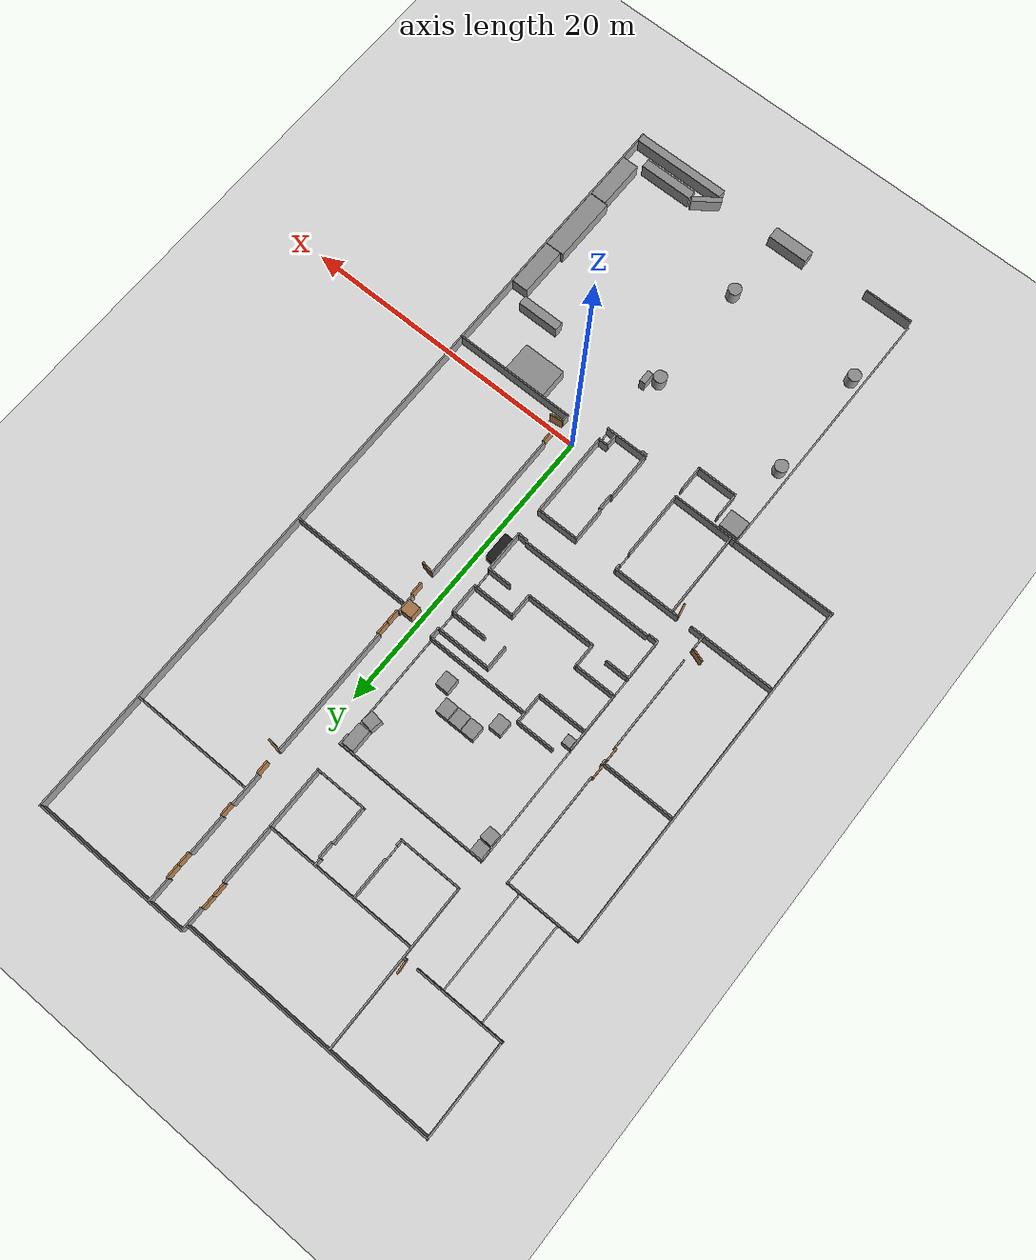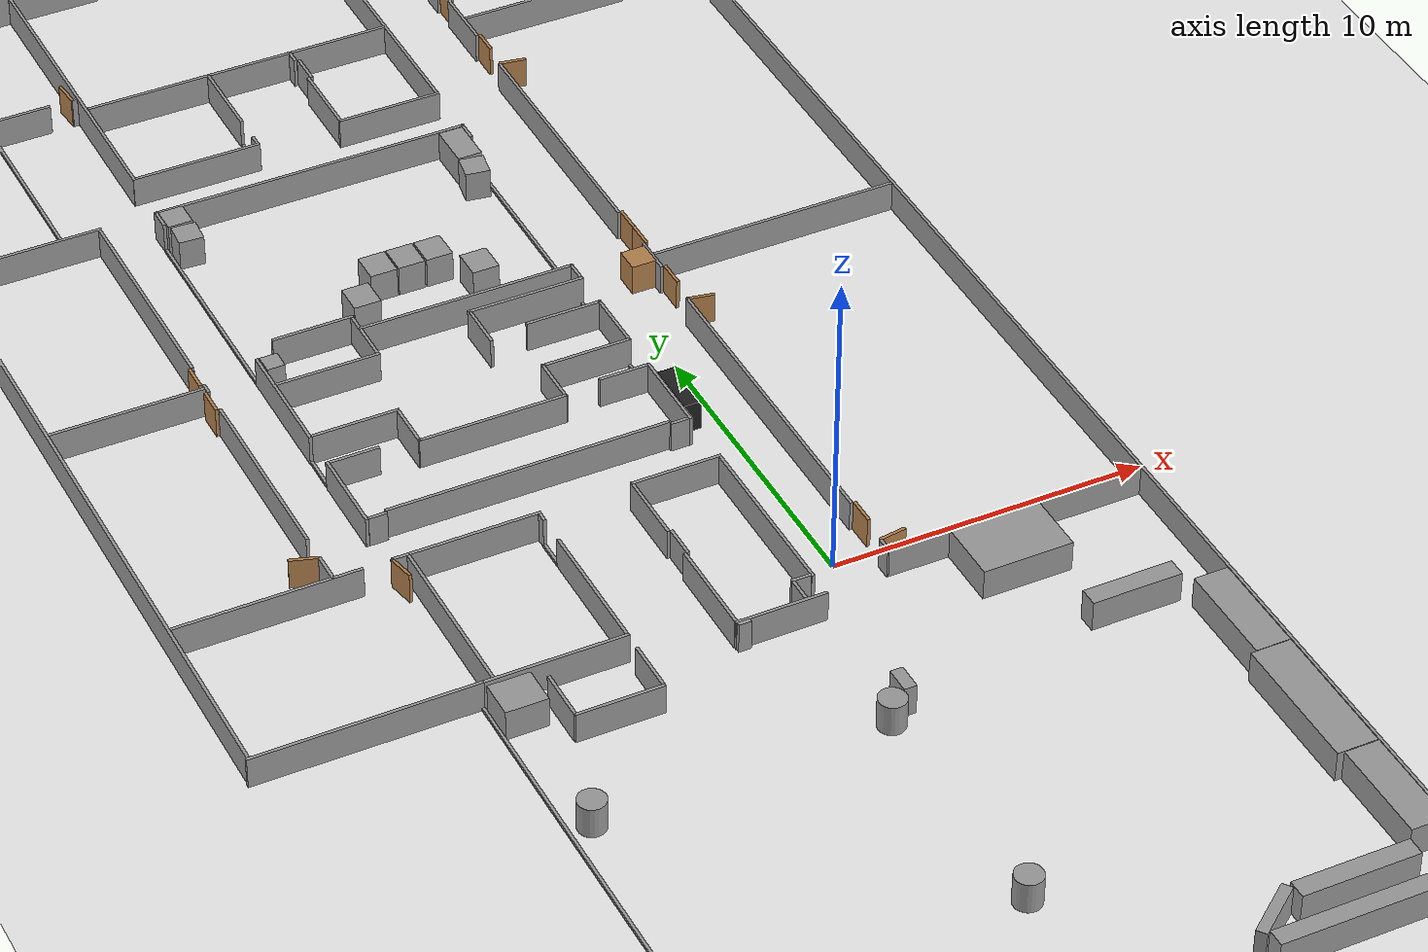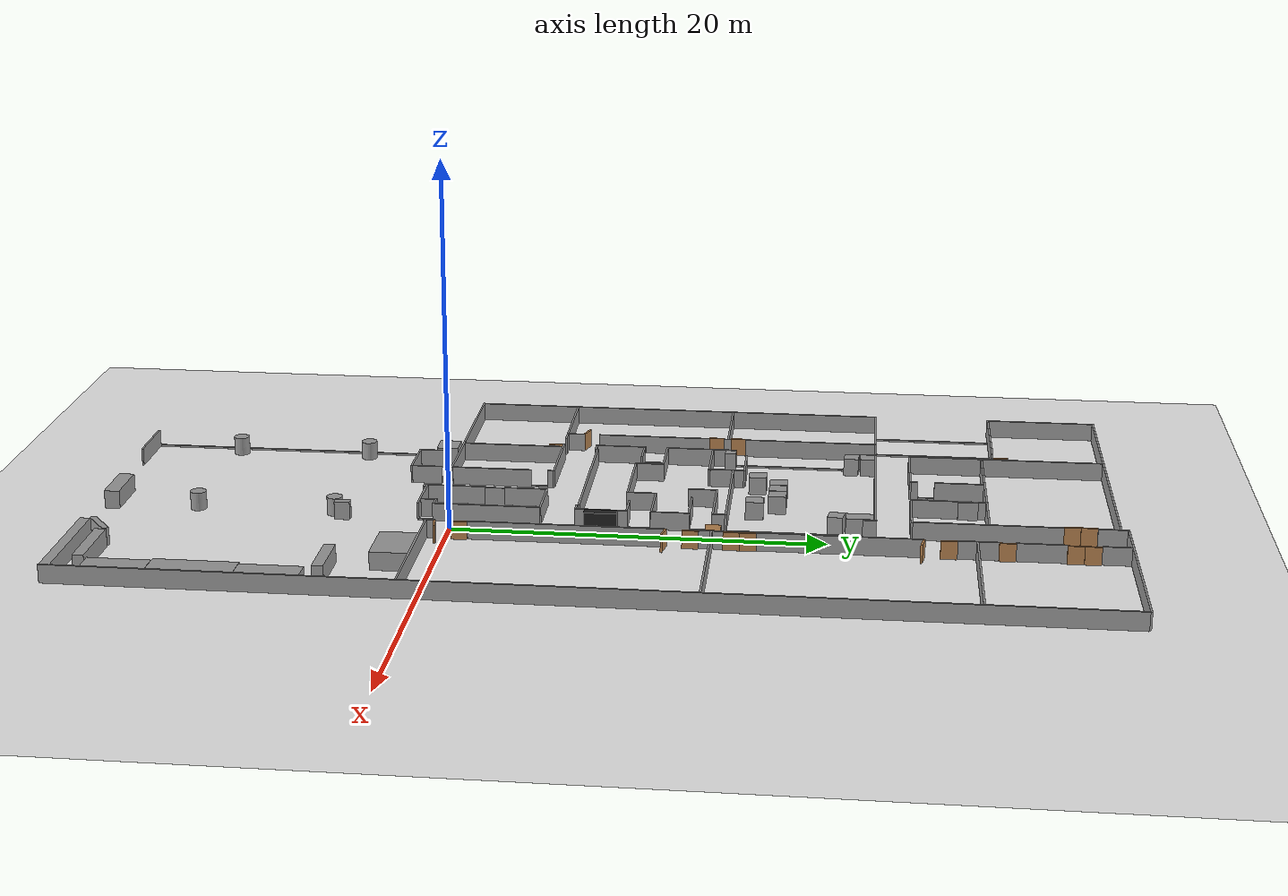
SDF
<sdf version="1.6">
 <world name="default">
  <light name="sun" type="directional">
   <pose>0 0 10 0 -0 0</pose>
   <diffuse>0.8 0.8 0.8 1</diffuse>
   <specular>0.2 0.2 0.2 1</specular>
   <attenuation>
    <range>1000</range>
    <constant>0.9</constant>
    <linear>0.01</linear>
    <quadratic>0.001</quadratic>
   </attenuation>
   <direction>-0.5 0.1 -0.9</direction>
  </light>
  <model name="ground_plane">
   <static>1</static>
   <link name="link">
    <collision name="collision">
     <geometry><plane><normal>0 0 1</normal><size>100 100</size></plane></geometry>
     <surface><friction><ode><mu>100</mu><mu2>50</mu2></ode></friction></surface>
    </collision>
    <visual name="visual">
     <cast_shadows>0</cast_shadows>
     <geometry><plane><normal>0 0 1</normal><size>100 100</size></plane></geometry>
     <material>
      <script><uri>file://media/materials/scripts/gazebo.material</uri><name>Gazebo/WhiteGlow</name></script>
     </material>
    </visual>
   </link>
  </model>
  <gravity>0 0 -9.8</gravity>
  <magnetic_field>6e-06 2.3e-05 -4.2e-05</magnetic_field>
  <atmosphere type="adiabatic"/>
  <physics name="default_physics" default="0" type="ode">
   <max_step_size>0.001</max_step_size>
   <real_time_factor>1</real_time_factor>
   <real_time_update_rate>1000</real_time_update_rate>
  </physics>
  <scene><ambient>0.4 0.4 0.4 1</ambient><background>0.7 0.7 0.7 1</background><shadows>1</shadows></scene>
  <spherical_coordinates>
   <surface_model>EARTH_WGS84</surface_model>
   <latitude_deg>0</latitude_deg>
   <longitude_deg>0</longitude_deg>
   <elevation>0</elevation>
   <heading_deg>0</heading_deg>
  </spherical_coordinates>
  <model name="L81">
   <link name="link_0">
    <pose>15.5392 12.1518 0.017394 0 -0 0</pose>
    <inertial>
     <mass>1</mass>
     <inertia><ixx>0.145833</ixx><ixy>0</ixy><ixz>0</ixz><iyy>0.145833</iyy><iyz>0</iyz><izz>0.125</izz></inertia>
    </inertial>
    <visual name="visual">
     <geometry><cylinder><radius>0.43</radius><length>1</length></cylinder></geometry>
     <material>
      <lighting>1</lighting>
      <script><uri>file://media/materials/scripts/gazebo.material</uri><name>Gazebo/Grey</name></script>
      <shader type="pixel"><normal_map>__default__</normal_map></shader>
      <ambient>0.3 0.3 0.3 1</ambient>
      <diffuse>0.7 0.7 0.7 1</diffuse>
      <specular>0.01 0.01 0.01 1</specular>
      <emissive>0 0 0 1</emissive>
     </material>
    </visual>
    <collision name="collision">
     <geometry><cylinder><radius>0.43</radius><length>1</length></cylinder></geometry>
     <surface>
      <friction>
       <ode><mu>1</mu><mu2>1</mu2><fdir1>0 0 0</fdir1><slip1>0</slip1><slip2>0</slip2></ode>
       <torsional>
        <coefficient>1</coefficient>
        <patch_radius>0</patch_radius>
        <surface_radius>0</surface_radius>
        <use_patch_radius>1</use_patch_radius>
        <ode><slip>0</slip></ode>
       </torsional>
      </friction>
      <bounce><restitution_coefficient>0</restitution_coefficient><threshold>1e+06</threshold></bounce>
      <contact>
       <collide_without_contact>0</collide_without_contact>
       <collide_without_contact_bitmask>1</collide_without_contact_bitmask>
       <collide_bitmask>1</collide_bitmask>
       <ode>
        <soft_cfm>0</soft_cfm>
        <soft_erp>0.2</soft_erp>
        <kp>1e+13</kp>
        <kd>1</kd>
        <max_vel>0.01</max_vel>
        <min_depth>0</min_depth>
       </ode>
       <bullet>
        <split_impulse>1</split_impulse>
        <split_impulse_penetration_threshold>-0.01</split_impulse_penetration_threshold>
        <soft_cfm>0</soft_cfm>
        <soft_erp>0.2</soft_erp>
        <kp>1e+13</kp>
        <kd>1</kd>
       </bullet>
      </contact>
     </surface>
    </collision>
   </link>
   <link name="link_0_clone">
    <pose>15.5293 4.61164 0.017394 0 -0 0</pose>
    <inertial>
     <mass>1</mass>
     <inertia><ixx>0.145833</ixx><ixy>0</ixy><ixz>0</ixz><iyy>0.145833</iyy><iyz>0</iyz><izz>0.125</izz></inertia>
    </inertial>
    <visual name="visual">
     <geometry><cylinder><radius>0.43</radius><length>1</length></cylinder></geometry>
     <material>
      <lighting>1</lighting>
      <script><uri>file://media/materials/scripts/gazebo.material</uri><name>Gazebo/Grey</name></script>
      <shader type="pixel"><normal_map>__default__</normal_map></shader>
      <ambient>0.3 0.3 0.3 1</ambient>
      <diffuse>0.7 0.7 0.7 1</diffuse>
      <specular>0.01 0.01 0.01 1</specular>
      <emissive>0 0 0 1</emissive>
     </material>
    </visual>
    <collision name="collision">
     <geometry><cylinder><radius>0.43</radius><length>1</length></cylinder></geometry>
     <surface>
      <friction>
       <ode><mu>1</mu><mu2>1</mu2><fdir1>0 0 0</fdir1><slip1>0</slip1><slip2>0</slip2></ode>
       <torsional>
        <coefficient>1</coefficient>
        <patch_radius>0</patch_radius>
        <surface_radius>0</surface_radius>
        <use_patch_radius>1</use_patch_radius>
        <ode><slip>0</slip></ode>
       </torsional>
      </friction>
      <bounce><restitution_coefficient>0</restitution_coefficient><threshold>1e+06</threshold></bounce>
      <contact>
       <collide_without_contact>0</collide_without_contact>
       <collide_without_contact_bitmask>1</collide_without_contact_bitmask>
       <collide_bitmask>1</collide_bitmask>
       <ode>
        <soft_cfm>0</soft_cfm>
        <soft_erp>0.2</soft_erp>
        <kp>1e+13</kp>
        <kd>1</kd>
        <max_vel>0.01</max_vel>
        <min_depth>0</min_depth>
       </ode>
       <bullet>
        <split_impulse>1</split_impulse>
        <split_impulse_penetration_threshold>-0.01</split_impulse_penetration_threshold>
        <soft_cfm>0</soft_cfm>
        <soft_erp>0.2</soft_erp>
        <kp>1e+13</kp>
        <kd>1</kd>
       </bullet>
      </contact>
     </surface>
    </collision>
   </link>
   <link name="link_0_clone_0">
    <pose>6.51018 12.165 0.017394 0 -0 0</pose>
    <inertial>
     <mass>1</mass>
     <inertia><ixx>0.145833</ixx><ixy>0</ixy><ixz>0</ixz><iyy>0.145833</iyy><iyz>0</iyz><izz>0.125</izz></inertia>
    </inertial>
    <visual name="visual">
     <geometry><cylinder><radius>0.43</radius><length>1</length></cylinder></geometry>
     <material>
      <lighting>1</lighting>
      <script><uri>file://media/materials/scripts/gazebo.material</uri><name>Gazebo/Grey</name></script>
      <shader type="pixel"><normal_map>__default__</normal_map></shader>
      <ambient>0.3 0.3 0.3 1</ambient>
      <diffuse>0.7 0.7 0.7 1</diffuse>
      <specular>0.01 0.01 0.01 1</specular>
      <emissive>0 0 0 1</emissive>
     </material>
    </visual>
    <collision name="collision">
     <geometry><cylinder><radius>0.43</radius><length>1</length></cylinder></geometry>
     <surface>
      <friction>
       <ode><mu>1</mu><mu2>1</mu2><fdir1>0 0 0</fdir1><slip1>0</slip1><slip2>0</slip2></ode>
       <torsional>
        <coefficient>1</coefficient>
        <patch_radius>0</patch_radius>
        <surface_radius>0</surface_radius>
        <use_patch_radius>1</use_patch_radius>
        <ode><slip>0</slip></ode>
       </torsional>
      </friction>
      <bounce><restitution_coefficient>0</restitution_coefficient><threshold>1e+06</threshold></bounce>
      <contact>
       <collide_without_contact>0</collide_without_contact>
       <collide_without_contact_bitmask>1</collide_without_contact_bitmask>
       <collide_bitmask>1</collide_bitmask>
       <ode>
        <soft_cfm>0</soft_cfm>
        <soft_erp>0.2</soft_erp>
        <kp>1e+13</kp>
        <kd>1</kd>
        <max_vel>0.01</max_vel>
        <min_depth>0</min_depth>
       </ode>
       <bullet>
        <split_impulse>1</split_impulse>
        <split_impulse_penetration_threshold>-0.01</split_impulse_penetration_threshold>
        <soft_cfm>0</soft_cfm>
        <soft_erp>0.2</soft_erp>
        <kp>1e+13</kp>
        <kd>1</kd>
       </bullet>
      </contact>
     </surface>
    </collision>
   </link>
   <link name="link_0_clone_0_clone">
    <pose>6.51926 4.6616 0.017394 0 -0 0</pose>
    <inertial>
     <mass>1</mass>
     <inertia><ixx>0.145833</ixx><ixy>0</ixy><ixz>0</ixz><iyy>0.145833</iyy><iyz>0</iyz><izz>0.125</izz></inertia>
    </inertial>
    <visual name="visual">
     <geometry><cylinder><radius>0.43</radius><length>1</length></cylinder></geometry>
     <material>
      <lighting>1</lighting>
      <script><uri>file://media/materials/scripts/gazebo.material</uri><name>Gazebo/Grey</name></script>
      <shader type="pixel"><normal_map>__default__</normal_map></shader>
      <ambient>0.3 0.3 0.3 1</ambient>
      <diffuse>0.7 0.7 0.7 1</diffuse>
      <specular>0.01 0.01 0.01 1</specular>
      <emissive>0 0 0 1</emissive>
     </material>
    </visual>
    <collision name="collision">
     <geometry><cylinder><radius>0.43</radius><length>1</length></cylinder></geometry>
     <surface>
      <friction>
       <ode><mu>1</mu><mu2>1</mu2><fdir1>0 0 0</fdir1><slip1>0</slip1><slip2>0</slip2></ode>
       <torsional>
        <coefficient>1</coefficient>
        <patch_radius>0</patch_radius>
        <surface_radius>0</surface_radius>
        <use_patch_radius>1</use_patch_radius>
        <ode><slip>0</slip></ode>
       </torsional>
      </friction>
      <bounce><restitution_coefficient>0</restitution_coefficient><threshold>1e+06</threshold></bounce>
      <contact>
       <collide_without_contact>0</collide_without_contact>
       <collide_without_contact_bitmask>1</collide_without_contact_bitmask>
       <collide_bitmask>1</collide_bitmask>
       <ode>
        <soft_cfm>0</soft_cfm>
        <soft_erp>0.2</soft_erp>
        <kp>1e+13</kp>
        <kd>1</kd>
        <max_vel>0.01</max_vel>
        <min_depth>0</min_depth>
       </ode>
       <bullet>
        <split_impulse>1</split_impulse>
        <split_impulse_penetration_threshold>-0.01</split_impulse_penetration_threshold>
        <soft_cfm>0</soft_cfm>
        <soft_erp>0.2</soft_erp>
        <kp>1e+13</kp>
        <kd>1</kd>
       </bullet>
      </contact>
     </surface>
    </collision>
   </link>
   <link name="link_1">
    <pose>6.1848 40.6724 0.017394 0 -0 0</pose>
    <inertial>
     <mass>0.639519</mass>
     <inertia>
      <ixx>0.0882035</ixx>
      <ixy>0</ixy>
      <ixz>0</ixz>
      <iyy>0.086567</iyy>
      <iyz>0</iyz>
      <izz>0.068184</izz>
     </inertia>
    </inertial>
    <visual name="visual">
     <geometry><box><size>0.790159 0.809357 1</size></box></geometry>
     <material>
      <lighting>1</lighting>
      <script><uri>file://media/materials/scripts/gazebo.material</uri><name>Gazebo/Grey</name></script>
      <shader type="pixel"><normal_map>__default__</normal_map></shader>
      <ambient>0.3 0.3 0.3 1</ambient>
      <diffuse>0.7 0.7 0.7 1</diffuse>
      <specular>0.01 0.01 0.01 1</specular>
      <emissive>0 0 0 1</emissive>
     </material>
    </visual>
    <collision name="collision">
     <geometry><box><size>0.790159 0.809357 1</size></box></geometry>
     <surface>
      <friction>
       <ode><mu>1</mu><mu2>1</mu2><fdir1>0 0 0</fdir1><slip1>0</slip1><slip2>0</slip2></ode>
       <torsional>
        <coefficient>1</coefficient>
        <patch_radius>0</patch_radius>
        <surface_radius>0</surface_radius>
        <use_patch_radius>1</use_patch_radius>
        <ode><slip>0</slip></ode>
       </torsional>
      </friction>
      <bounce><restitution_coefficient>0</restitution_coefficient><threshold>1e+06</threshold></bounce>
      <contact>
       <collide_without_contact>0</collide_without_contact>
       <collide_without_contact_bitmask>1</collide_without_contact_bitmask>
       <collide_bitmask>1</collide_bitmask>
       <ode>
        <soft_cfm>0</soft_cfm>
        <soft_erp>0.2</soft_erp>
        <kp>1e+13</kp>
        <kd>1</kd>
        <max_vel>0.01</max_vel>
        <min_depth>0</min_depth>
       </ode>
       <bullet>
        <split_impulse>1</split_impulse>
        <split_impulse_penetration_threshold>-0.01</split_impulse_penetration_threshold>
        <soft_cfm>0</soft_cfm>
        <soft_erp>0.2</soft_erp>
        <kp>1e+13</kp>
        <kd>1</kd>
       </bullet>
      </contact>
     </surface>
    </collision>
   </link>
   <link name="link_1_clone">
    <pose>6.20714 39.7777 0.017394 -0 -0 -0.068112</pose>
    <inertial>
     <mass>0.639519</mass>
     <inertia>
      <ixx>0.0882035</ixx>
      <ixy>0</ixy>
      <ixz>0</ixz>
      <iyy>0.086567</iyy>
      <iyz>0</iyz>
      <izz>0.068184</izz>
     </inertia>
    </inertial>
    <visual name="visual">
     <geometry><box><size>0.790159 0.809357 1</size></box></geometry>
     <material>
      <lighting>1</lighting>
      <script><uri>file://media/materials/scripts/gazebo.material</uri><name>Gazebo/Grey</name></script>
      <shader type="pixel"><normal_map>__default__</normal_map></shader>
      <ambient>0.3 0.3 0.3 1</ambient>
      <diffuse>0.7 0.7 0.7 1</diffuse>
      <specular>0.01 0.01 0.01 1</specular>
      <emissive>0 0 0 1</emissive>
     </material>
    </visual>
    <collision name="collision">
     <geometry><box><size>0.790159 0.809357 1</size></box></geometry>
     <surface>
      <friction>
       <ode><mu>1</mu><mu2>1</mu2><fdir1>0 0 0</fdir1><slip1>0</slip1><slip2>0</slip2></ode>
       <torsional>
        <coefficient>1</coefficient>
        <patch_radius>0</patch_radius>
        <surface_radius>0</surface_radius>
        <use_patch_radius>1</use_patch_radius>
        <ode><slip>0</slip></ode>
       </torsional>
      </friction>
      <bounce><restitution_coefficient>0</restitution_coefficient><threshold>1e+06</threshold></bounce>
      <contact>
       <collide_without_contact>0</collide_without_contact>
       <collide_without_contact_bitmask>1</collide_without_contact_bitmask>
       <collide_bitmask>1</collide_bitmask>
       <ode>
        <soft_cfm>0</soft_cfm>
        <soft_erp>0.2</soft_erp>
        <kp>1e+13</kp>
        <kd>1</kd>
        <max_vel>0.01</max_vel>
        <min_depth>0</min_depth>
       </ode>
       <bullet>
        <split_impulse>1</split_impulse>
        <split_impulse_penetration_threshold>-0.01</split_impulse_penetration_threshold>
        <soft_cfm>0</soft_cfm>
        <soft_erp>0.2</soft_erp>
        <kp>1e+13</kp>
        <kd>1</kd>
       </bullet>
      </contact>
     </surface>
    </collision>
   </link>
   <link name="link_1_clone_0">
    <pose>15.4924 40.2967 0.017394 0 -0 0</pose>
    <inertial>
     <mass>1.15579</mass>
     <inertia>
      <ixx>0.302392</ixx>
      <ixy>0</ixy>
      <ixz>0</ixz>
      <iyy>0.15645</iyy>
      <iyz>0</iyz>
      <izz>0.266211</izz>
     </inertia>
    </inertial>
    <visual name="visual">
     <geometry><box><size>0.790159 1.46273 1</size></box></geometry>
     <material>
      <lighting>1</lighting>
      <script><uri>file://media/materials/scripts/gazebo.material</uri><name>Gazebo/Grey</name></script>
      <shader type="pixel"><normal_map>__default__</normal_map></shader>
      <ambient>0.3 0.3 0.3 1</ambient>
      <diffuse>0.7 0.7 0.7 1</diffuse>
      <specular>0.01 0.01 0.01 1</specular>
      <emissive>0 0 0 1</emissive>
     </material>
    </visual>
    <collision name="collision">
     <geometry><box><size>0.790159 1.46273 1</size></box></geometry>
     <surface>
      <friction>
       <ode><mu>1</mu><mu2>1</mu2><fdir1>0 0 0</fdir1><slip1>0</slip1><slip2>0</slip2></ode>
       <torsional>
        <coefficient>1</coefficient>
        <patch_radius>0</patch_radius>
        <surface_radius>0</surface_radius>
        <use_patch_radius>1</use_patch_radius>
        <ode><slip>0</slip></ode>
       </torsional>
      </friction>
      <bounce><restitution_coefficient>0</restitution_coefficient><threshold>1e+06</threshold></bounce>
      <contact>
       <collide_without_contact>0</collide_without_contact>
       <collide_without_contact_bitmask>1</collide_without_contact_bitmask>
       <collide_bitmask>1</collide_bitmask>
       <ode>
        <soft_cfm>0</soft_cfm>
        <soft_erp>0.2</soft_erp>
        <kp>1e+13</kp>
        <kd>1</kd>
        <max_vel>0.01</max_vel>
        <min_depth>0</min_depth>
       </ode>
       <bullet>
        <split_impulse>1</split_impulse>
        <split_impulse_penetration_threshold>-0.01</split_impulse_penetration_threshold>
        <soft_cfm>0</soft_cfm>
        <soft_erp>0.2</soft_erp>
        <kp>1e+13</kp>
        <kd>1</kd>
       </bullet>
      </contact>
     </surface>
    </collision>
   </link>
   <link name="link_1_clone_0_clone">
    <pose>16.2726 26.6377 0.017394 0 -0 0</pose>
    <inertial>
     <mass>0.986228</mass>
     <inertia>
      <ixx>0.335977</ixx>
      <ixy>0</ixy>
      <ixz>0</ixz>
      <iyy>0.108072</iyy>
      <iyz>0</iyz>
      <izz>0.279678</izz>
     </inertia>
    </inertial>
    <visual name="visual">
     <geometry><box><size>0.561225 1.75728 1</size></box></geometry>
     <material>
      <lighting>1</lighting>
      <script><uri>file://media/materials/scripts/gazebo.material</uri><name>Gazebo/Black</name></script>
      <shader type="pixel"><normal_map>__default__</normal_map></shader>
      <ambient>0.3 0.3 0.3 1</ambient>
      <diffuse>0.7 0.7 0.7 1</diffuse>
      <specular>0.01 0.01 0.01 1</specular>
      <emissive>0 0 0 1</emissive>
     </material>
    </visual>
    <collision name="collision">
     <geometry><box><size>0.561225 1.75728 1</size></box></geometry>
     <surface>
      <friction>
       <ode><mu>1</mu><mu2>1</mu2><fdir1>0 0 0</fdir1><slip1>0</slip1><slip2>0</slip2></ode>
       <torsional>
        <coefficient>1</coefficient>
        <patch_radius>0</patch_radius>
        <surface_radius>0</surface_radius>
        <use_patch_radius>1</use_patch_radius>
        <ode><slip>0</slip></ode>
       </torsional>
      </friction>
      <bounce><restitution_coefficient>0</restitution_coefficient><threshold>1e+06</threshold></bounce>
      <contact>
       <collide_without_contact>0</collide_without_contact>
       <collide_without_contact_bitmask>1</collide_without_contact_bitmask>
       <collide_bitmask>1</collide_bitmask>
       <ode>
        <soft_cfm>0</soft_cfm>
        <soft_erp>0.2</soft_erp>
        <kp>1e+13</kp>
        <kd>1</kd>
        <max_vel>0.01</max_vel>
        <min_depth>0</min_depth>
       </ode>
       <bullet>
        <split_impulse>1</split_impulse>
        <split_impulse_penetration_threshold>-0.01</split_impulse_penetration_threshold>
        <soft_cfm>0</soft_cfm>
        <soft_erp>0.2</soft_erp>
        <kp>1e+13</kp>
        <kd>1</kd>
       </bullet>
      </contact>
     </surface>
    </collision>
   </link>
   <link name="link_1_clone_1">
    <pose>15.407 39.061 0.017394 0 -0 -0.15142</pose>
    <inertial>
     <mass>0.639519</mass>
     <inertia>
      <ixx>0.0882035</ixx>
      <ixy>0</ixy>
      <ixz>0</ixz>
      <iyy>0.086567</iyy>
      <iyz>0</iyz>
      <izz>0.068184</izz>
     </inertia>
    </inertial>
    <visual name="visual">
     <geometry><box><size>0.790159 0.809357 1</size></box></geometry>
     <material>
      <lighting>1</lighting>
      <script><uri>file://media/materials/scripts/gazebo.material</uri><name>Gazebo/Grey</name></script>
      <shader type="pixel"><normal_map>__default__</normal_map></shader>
      <ambient>0.3 0.3 0.3 1</ambient>
      <diffuse>0.7 0.7 0.7 1</diffuse>
      <specular>0.01 0.01 0.01 1</specular>
      <emissive>0 0 0 1</emissive>
     </material>
    </visual>
    <collision name="collision">
     <geometry><box><size>0.790159 0.809357 1</size></box></geometry>
     <surface>
      <friction>
       <ode><mu>1</mu><mu2>1</mu2><fdir1>0 0 0</fdir1><slip1>0</slip1><slip2>0</slip2></ode>
       <torsional>
        <coefficient>1</coefficient>
        <patch_radius>0</patch_radius>
        <surface_radius>0</surface_radius>
        <use_patch_radius>1</use_patch_radius>
        <ode><slip>0</slip></ode>
       </torsional>
      </friction>
      <bounce><restitution_coefficient>0</restitution_coefficient><threshold>1e+06</threshold></bounce>
      <contact>
       <collide_without_contact>0</collide_without_contact>
       <collide_without_contact_bitmask>1</collide_without_contact_bitmask>
       <collide_bitmask>1</collide_bitmask>
       <ode>
        <soft_cfm>0</soft_cfm>
        <soft_erp>0.2</soft_erp>
        <kp>1e+13</kp>
        <kd>1</kd>
        <max_vel>0.01</max_vel>
        <min_depth>0</min_depth>
       </ode>
       <bullet>
        <split_impulse>1</split_impulse>
        <split_impulse_penetration_threshold>-0.01</split_impulse_penetration_threshold>
        <soft_cfm>0</soft_cfm>
        <soft_erp>0.2</soft_erp>
        <kp>1e+13</kp>
        <kd>1</kd>
       </bullet>
      </contact>
     </surface>
    </collision>
   </link>
   <link name="link_1_clone_2">
    <pose>17.9179 32.7201 0.017394 0 -0 0</pose>
    <inertial>
     <mass>0.639519</mass>
     <inertia>
      <ixx>0.0882035</ixx>
      <ixy>0</ixy>
      <ixz>0</ixz>
      <iyy>0.086567</iyy>
      <iyz>0</iyz>
      <izz>0.068184</izz>
     </inertia>
    </inertial>
    <visual name="visual">
     <geometry><box><size>0.790159 0.809357 1</size></box></geometry>
     <material>
      <lighting>1</lighting>
      <script><uri>file://media/materials/scripts/gazebo.material</uri><name>Gazebo/Wood</name></script>
      <shader type="pixel"><normal_map>__default__</normal_map></shader>
      <ambient>0.3 0.3 0.3 1</ambient>
      <diffuse>0.7 0.7 0.7 1</diffuse>
      <specular>0.01 0.01 0.01 1</specular>
      <emissive>0 0 0 1</emissive>
     </material>
    </visual>
    <collision name="collision">
     <geometry><box><size>0.790159 0.809357 1</size></box></geometry>
     <surface>
      <friction>
       <ode><mu>1</mu><mu2>1</mu2><fdir1>0 0 0</fdir1><slip1>0</slip1><slip2>0</slip2></ode>
       <torsional>
        <coefficient>1</coefficient>
        <patch_radius>0</patch_radius>
        <surface_radius>0</surface_radius>
        <use_patch_radius>1</use_patch_radius>
        <ode><slip>0</slip></ode>
       </torsional>
      </friction>
      <bounce><restitution_coefficient>0</restitution_coefficient><threshold>1e+06</threshold></bounce>
      <contact>
       <collide_without_contact>0</collide_without_contact>
       <collide_without_contact_bitmask>1</collide_without_contact_bitmask>
       <collide_bitmask>1</collide_bitmask>
       <ode>
        <soft_cfm>0</soft_cfm>
        <soft_erp>0.2</soft_erp>
        <kp>1e+13</kp>
        <kd>1</kd>
        <max_vel>0.01</max_vel>
        <min_depth>0</min_depth>
       </ode>
       <bullet>
        <split_impulse>1</split_impulse>
        <split_impulse_penetration_threshold>-0.01</split_impulse_penetration_threshold>
        <soft_cfm>0</soft_cfm>
        <soft_erp>0.2</soft_erp>
        <kp>1e+13</kp>
        <kd>1</kd>
       </bullet>
      </contact>
     </surface>
    </collision>
   </link>
   <link name="link_1_clone_2_clone">
    <pose>13.3256 16.665 0.017394 0 -0 0</pose>
    <inertial>
     <mass>0.0501795</mass>
     <inertia>
      <ixx>0.0042482</ixx>
      <ixy>0</ixy>
      <ixz>0</ixz>
      <iyy>0.00484291</iyy>
      <iyz>0</iyz>
      <izz>0.000727871</izz>
     </inertia>
    </inertial>
    <visual name="visual">
     <geometry><box><size>0.397671 0.126182 1</size></box></geometry>
     <material>
      <lighting>1</lighting>
      <script><uri>file://media/materials/scripts/gazebo.material</uri><name>Gazebo/Grey</name></script>
      <shader type="pixel"><normal_map>__default__</normal_map></shader>
      <ambient>0.3 0.3 0.3 1</ambient>
      <diffuse>0.7 0.7 0.7 1</diffuse>
      <specular>0.01 0.01 0.01 1</specular>
      <emissive>0 0 0 1</emissive>
     </material>
    </visual>
    <collision name="collision">
     <geometry><box><size>0.397671 0.126182 1</size></box></geometry>
     <surface>
      <friction>
       <ode><mu>1</mu><mu2>1</mu2><fdir1>0 0 0</fdir1><slip1>0</slip1><slip2>0</slip2></ode>
       <torsional>
        <coefficient>1</coefficient>
        <patch_radius>0</patch_radius>
        <surface_radius>0</surface_radius>
        <use_patch_radius>1</use_patch_radius>
        <ode><slip>0</slip></ode>
       </torsional>
      </friction>
      <bounce><restitution_coefficient>0</restitution_coefficient><threshold>1e+06</threshold></bounce>
      <contact>
       <collide_without_contact>0</collide_without_contact>
       <collide_without_contact_bitmask>1</collide_without_contact_bitmask>
       <collide_bitmask>1</collide_bitmask>
       <ode>
        <soft_cfm>0</soft_cfm>
        <soft_erp>0.2</soft_erp>
        <kp>1e+13</kp>
        <kd>1</kd>
        <max_vel>0.01</max_vel>
        <min_depth>0</min_depth>
       </ode>
       <bullet>
        <split_impulse>1</split_impulse>
        <split_impulse_penetration_threshold>-0.01</split_impulse_penetration_threshold>
        <soft_cfm>0</soft_cfm>
        <soft_erp>0.2</soft_erp>
        <kp>1e+13</kp>
        <kd>1</kd>
       </bullet>
      </contact>
     </surface>
    </collision>
   </link>
   <link name="link_1_clone_2_clone_clone">
    <pose>16.1732 12.7098 0.017394 0 -0 0</pose>
    <inertial>
     <mass>0.330309</mass>
     <inertia>
      <ixx>0.0465158</ixx>
      <ixy>0</ixy>
      <ixz>0</ixz>
      <iyy>0.0318787</iyy>
      <iyz>0</iyz>
      <izz>0.023343</izz>
     </inertia>
    </inertial>
    <visual name="visual">
     <geometry><box><size>0.397671 0.830603 1</size></box></geometry>
     <material>
      <lighting>1</lighting>
      <script><uri>file://media/materials/scripts/gazebo.material</uri><name>Gazebo/Grey</name></script>
      <shader type="pixel"><normal_map>__default__</normal_map></shader>
      <ambient>0.3 0.3 0.3 1</ambient>
      <diffuse>0.7 0.7 0.7 1</diffuse>
      <specular>0.01 0.01 0.01 1</specular>
      <emissive>0 0 0 1</emissive>
     </material>
    </visual>
    <collision name="collision">
     <geometry><box><size>0.397671 0.830603 1</size></box></geometry>
     <surface>
      <friction>
       <ode><mu>1</mu><mu2>1</mu2><fdir1>0 0 0</fdir1><slip1>0</slip1><slip2>0</slip2></ode>
       <torsional>
        <coefficient>1</coefficient>
        <patch_radius>0</patch_radius>
        <surface_radius>0</surface_radius>
        <use_patch_radius>1</use_patch_radius>
        <ode><slip>0</slip></ode>
       </torsional>
      </friction>
      <bounce><restitution_coefficient>0</restitution_coefficient><threshold>1e+06</threshold></bounce>
      <contact>
       <collide_without_contact>0</collide_without_contact>
       <collide_without_contact_bitmask>1</collide_without_contact_bitmask>
       <collide_bitmask>1</collide_bitmask>
       <ode>
        <soft_cfm>0</soft_cfm>
        <soft_erp>0.2</soft_erp>
        <kp>1e+13</kp>
        <kd>1</kd>
        <max_vel>0.01</max_vel>
        <min_depth>0</min_depth>
       </ode>
       <bullet>
        <split_impulse>1</split_impulse>
        <split_impulse_penetration_threshold>-0.01</split_impulse_penetration_threshold>
        <soft_cfm>0</soft_cfm>
        <soft_erp>0.2</soft_erp>
        <kp>1e+13</kp>
        <kd>1</kd>
       </bullet>
      </contact>
     </surface>
    </collision>
   </link>
   <link name="link_clone">
    <pose>2.36987 17.6336 -0 0 -0 0</pose>
    <inertial>
     <mass>1.01184</mass>
     <inertia>
      <ixx>0.0851633</ixx>
      <ixy>0</ixy>
      <ixz>0</ixz>
      <iyy>4.20635</iyy>
      <iyz>0</iyz>
      <izz>4.12288</izz>
     </inertia>
    </inertial>
    <visual name="visual">
     <geometry><box><size>6.99182 0.1 1</size></box></geometry>
     <material>
      <script><name>Gazebo/Grey</name><uri>file://media/materials/scripts/gazebo.material</uri></script>
      <shader type="pixel"><normal_map>__default__</normal_map></shader>
      <ambient>0.3 0.3 0.3 1</ambient>
      <diffuse>0.7 0.7 0.7 1</diffuse>
      <specular>0.01 0.01 0.01 1</specular>
      <emissive>0 0 0 1</emissive>
     </material>
    </visual>
    <collision name="collision">
     <geometry><box><size>6.99182 0.1 1</size></box></geometry>
     <surface>
      <friction>
       <ode><mu>1</mu><mu2>1</mu2><fdir1>0 0 0</fdir1><slip1>0</slip1><slip2>0</slip2></ode>
       <torsional>
        <coefficient>1</coefficient>
        <patch_radius>0</patch_radius>
        <surface_radius>0</surface_radius>
        <use_patch_radius>1</use_patch_radius>
        <ode><slip>0</slip></ode>
       </torsional>
      </friction>
      <bounce><restitution_coefficient>0</restitution_coefficient><threshold>1e+06</threshold></bounce>
      <contact>
       <collide_without_contact>0</collide_without_contact>
       <collide_without_contact_bitmask>1</collide_without_contact_bitmask>
       <collide_bitmask>1</collide_bitmask>
       <ode>
        <soft_cfm>0</soft_cfm>
        <soft_erp>0.2</soft_erp>
        <kp>1e+13</kp>
        <kd>1</kd>
        <max_vel>0.01</max_vel>
        <min_depth>0</min_depth>
       </ode>
       <bullet>
        <split_impulse>1</split_impulse>
        <split_impulse_penetration_threshold>-0.01</split_impulse_penetration_threshold>
        <soft_cfm>0</soft_cfm>
        <soft_erp>0.2</soft_erp>
        <kp>1e+13</kp>
        <kd>1</kd>
       </bullet>
      </contact>
     </surface>
    </collision>
   </link>
   <link name="link_clone_0">
    <pose>-1.0415 29.3775 0 0 -0 0</pose>
    <inertial>
     <mass>1</mass>
     <inertia>
      <ixx>0.166667</ixx>
      <ixy>0</ixy>
      <ixz>0</ixz>
      <iyy>0.166667</iyy>
      <iyz>0</iyz>
      <izz>0.166667</izz>
     </inertia>
    </inertial>
    <visual name="visual">
     <geometry><box><size>0.1 23.38 1</size></box></geometry>
     <material>
      <script><name>Gazebo/Grey</name><uri>file://media/materials/scripts/gazebo.material</uri></script>
      <shader type="pixel"><normal_map>__default__</normal_map></shader>
      <ambient>0.3 0.3 0.3 1</ambient>
      <diffuse>0.7 0.7 0.7 1</diffuse>
      <specular>0.01 0.01 0.01 1</specular>
      <emissive>0 0 0 1</emissive>
     </material>
    </visual>
    <collision name="collision">
     <geometry><box><size>0.1 23.38 1</size></box></geometry>
     <surface>
      <friction>
       <ode><mu>1</mu><mu2>1</mu2><fdir1>0 0 0</fdir1><slip1>0</slip1><slip2>0</slip2></ode>
       <torsional>
        <coefficient>1</coefficient>
        <patch_radius>0</patch_radius>
        <surface_radius>0</surface_radius>
        <use_patch_radius>1</use_patch_radius>
        <ode><slip>0</slip></ode>
       </torsional>
      </friction>
      <bounce><restitution_coefficient>0</restitution_coefficient><threshold>1e+06</threshold></bounce>
      <contact>
       <collide_without_contact>0</collide_without_contact>
       <collide_without_contact_bitmask>1</collide_without_contact_bitmask>
       <collide_bitmask>1</collide_bitmask>
       <ode>
        <soft_cfm>0</soft_cfm>
        <soft_erp>0.2</soft_erp>
        <kp>1e+13</kp>
        <kd>1</kd>
        <max_vel>0.01</max_vel>
        <min_depth>0</min_depth>
       </ode>
       <bullet>
        <split_impulse>1</split_impulse>
        <split_impulse_penetration_threshold>-0.01</split_impulse_penetration_threshold>
        <soft_cfm>0</soft_cfm>
        <soft_erp>0.2</soft_erp>
        <kp>1e+13</kp>
        <kd>1</kd>
       </bullet>
      </contact>
     </surface>
    </collision>
   </link>
   <link name="link_clone_0_clone_0">
    <pose>3.89763 28.3864 0 0 -0 0</pose>
    <inertial>
     <mass>0.361309</mass>
     <inertia>
      <ixx>1.26708</ixx>
      <ixy>0</ixy>
      <ixz>0</ixz>
      <iyy>0.0304101</iyy>
      <iyz>0</iyz>
      <izz>1.23728</izz>
     </inertia>
    </inertial>
    <visual name="visual">
     <geometry><box><size>0.1 6.40961 1</size></box></geometry>
     <material>
      <script><name>Gazebo/Grey</name><uri>file://media/materials/scripts/gazebo.material</uri></script>
      <shader type="pixel"><normal_map>__default__</normal_map></shader>
      <ambient>0.3 0.3 0.3 1</ambient>
      <diffuse>0.7 0.7 0.7 1</diffuse>
      <specular>0.01 0.01 0.01 1</specular>
      <emissive>0 0 0 1</emissive>
     </material>
    </visual>
    <collision name="collision">
     <geometry><box><size>0.1 6.40961 1</size></box></geometry>
     <surface>
      <friction>
       <ode><mu>1</mu><mu2>1</mu2><fdir1>0 0 0</fdir1><slip1>0</slip1><slip2>0</slip2></ode>
       <torsional>
        <coefficient>1</coefficient>
        <patch_radius>0</patch_radius>
        <surface_radius>0</surface_radius>
        <use_patch_radius>1</use_patch_radius>
        <ode><slip>0</slip></ode>
       </torsional>
      </friction>
      <bounce><restitution_coefficient>0</restitution_coefficient><threshold>1e+06</threshold></bounce>
      <contact>
       <collide_without_contact>0</collide_without_contact>
       <collide_without_contact_bitmask>1</collide_without_contact_bitmask>
       <collide_bitmask>1</collide_bitmask>
       <ode>
        <soft_cfm>0</soft_cfm>
        <soft_erp>0.2</soft_erp>
        <kp>1e+13</kp>
        <kd>1</kd>
        <max_vel>0.01</max_vel>
        <min_depth>0</min_depth>
       </ode>
       <bullet>
        <split_impulse>1</split_impulse>
        <split_impulse_penetration_threshold>-0.01</split_impulse_penetration_threshold>
        <soft_cfm>0</soft_cfm>
        <soft_erp>0.2</soft_erp>
        <kp>1e+13</kp>
        <kd>1</kd>
       </bullet>
      </contact>
     </surface>
    </collision>
   </link>
   <link name="link_clone_0_clone_0_clone">
    <pose>18.3475 25.0687 0 0 -0 0</pose>
    <inertial>
     <mass>0.587737</mass>
     <inertia>
      <ixx>5.37342</ixx>
      <ixy>0</ixy>
      <ixz>0</ixz>
      <iyy>0.0494679</iyy>
      <iyz>0</iyz>
      <izz>5.32493</izz>
     </inertia>
    </inertial>
    <visual name="visual">
     <geometry><box><size>0.1 10.4264 1</size></box></geometry>
     <material>
      <script><name>Gazebo/Grey</name><uri>file://media/materials/scripts/gazebo.material</uri></script>
      <shader type="pixel"><normal_map>__default__</normal_map></shader>
      <ambient>0.3 0.3 0.3 1</ambient>
      <diffuse>0.7 0.7 0.7 1</diffuse>
      <specular>0.01 0.01 0.01 1</specular>
      <emissive>0 0 0 1</emissive>
     </material>
    </visual>
    <collision name="collision">
     <geometry><box><size>0.1 10.4264 1</size></box></geometry>
     <surface>
      <friction>
       <ode><mu>1</mu><mu2>1</mu2><fdir1>0 0 0</fdir1><slip1>0</slip1><slip2>0</slip2></ode>
       <torsional>
        <coefficient>1</coefficient>
        <patch_radius>0</patch_radius>
        <surface_radius>0</surface_radius>
        <use_patch_radius>1</use_patch_radius>
        <ode><slip>0</slip></ode>
       </torsional>
      </friction>
      <bounce><restitution_coefficient>0</restitution_coefficient><threshold>1e+06</threshold></bounce>
      <contact>
       <collide_without_contact>0</collide_without_contact>
       <collide_without_contact_bitmask>1</collide_without_contact_bitmask>
       <collide_bitmask>1</collide_bitmask>
       <ode>
        <soft_cfm>0</soft_cfm>
        <soft_erp>0.2</soft_erp>
        <kp>1e+13</kp>
        <kd>1</kd>
        <max_vel>0.01</max_vel>
        <min_depth>0</min_depth>
       </ode>
       <bullet>
        <split_impulse>1</split_impulse>
        <split_impulse_penetration_threshold>-0.01</split_impulse_penetration_threshold>
        <soft_cfm>0</soft_cfm>
        <soft_erp>0.2</soft_erp>
        <kp>1e+13</kp>
        <kd>1</kd>
       </bullet>
      </contact>
     </surface>
    </collision>
   </link>
   <link name="link_clone_0_clone_0_clone_0">
    <pose>6.17322 20.495 -0 0 -0 0</pose>
    <inertial>
     <mass>0.323432</mass>
     <inertia>
      <ixx>0.91426</ixx>
      <ixy>0</ixy>
      <ixz>0</ixz>
      <iyy>0.0272222</iyy>
      <iyz>0</iyz>
      <izz>0.887577</izz>
     </inertia>
    </inertial>
    <visual name="visual">
     <geometry><box><size>0.1 5.73768 1</size></box></geometry>
     <material>
      <script><name>Gazebo/Grey</name><uri>file://media/materials/scripts/gazebo.material</uri></script>
      <shader type="pixel"><normal_map>__default__</normal_map></shader>
      <ambient>0.3 0.3 0.3 1</ambient>
      <diffuse>0.7 0.7 0.7 1</diffuse>
      <specular>0.01 0.01 0.01 1</specular>
      <emissive>0 0 0 1</emissive>
     </material>
    </visual>
    <collision name="collision">
     <geometry><box><size>0.1 5.73768 1</size></box></geometry>
     <surface>
      <friction>
       <ode><mu>1</mu><mu2>1</mu2><fdir1>0 0 0</fdir1><slip1>0</slip1><slip2>0</slip2></ode>
       <torsional>
        <coefficient>1</coefficient>
        <patch_radius>0</patch_radius>
        <surface_radius>0</surface_radius>
        <use_patch_radius>1</use_patch_radius>
        <ode><slip>0</slip></ode>
       </torsional>
      </friction>
      <bounce><restitution_coefficient>0</restitution_coefficient><threshold>1e+06</threshold></bounce>
      <contact>
       <collide_without_contact>0</collide_without_contact>
       <collide_without_contact_bitmask>1</collide_without_contact_bitmask>
       <collide_bitmask>1</collide_bitmask>
       <ode>
        <soft_cfm>0</soft_cfm>
        <soft_erp>0.2</soft_erp>
        <kp>1e+13</kp>
        <kd>1</kd>
        <max_vel>0.01</max_vel>
        <min_depth>0</min_depth>
       </ode>
       <bullet>
        <split_impulse>1</split_impulse>
        <split_impulse_penetration_threshold>-0.01</split_impulse_penetration_threshold>
        <soft_cfm>0</soft_cfm>
        <soft_erp>0.2</soft_erp>
        <kp>1e+13</kp>
        <kd>1</kd>
       </bullet>
      </contact>
     </surface>
    </collision>
   </link>
   <link name="link_clone_0_clone_0_clone_0_clone_clone">
    <pose>9.87549 45.6856 -0 0 -0 0</pose>
    <inertial>
     <mass>0.151422</mass>
     <inertia>
      <ixx>0.106624</ixx>
      <ixy>0</ixy>
      <ixz>0</ixz>
      <iyy>0.0127447</iyy>
      <iyz>0</iyz>
      <izz>0.0941318</izz>
     </inertia>
    </inertial>
    <visual name="visual">
     <geometry><box><size>0.1 2.72944 1</size></box></geometry>
     <material>
      <script><name>Gazebo/Grey</name><uri>file://media/materials/scripts/gazebo.material</uri></script>
      <shader type="pixel"><normal_map>__default__</normal_map></shader>
      <ambient>0.3 0.3 0.3 1</ambient>
      <diffuse>0.7 0.7 0.7 1</diffuse>
      <specular>0.01 0.01 0.01 1</specular>
      <emissive>0 0 0 1</emissive>
     </material>
    </visual>
    <collision name="collision">
     <geometry><box><size>0.1 2.72944 1</size></box></geometry>
     <surface>
      <friction>
       <ode><mu>1</mu><mu2>1</mu2><fdir1>0 0 0</fdir1><slip1>0</slip1><slip2>0</slip2></ode>
       <torsional>
        <coefficient>1</coefficient>
        <patch_radius>0</patch_radius>
        <surface_radius>0</surface_radius>
        <use_patch_radius>1</use_patch_radius>
        <ode><slip>0</slip></ode>
       </torsional>
      </friction>
      <bounce><restitution_coefficient>0</restitution_coefficient><threshold>1e+06</threshold></bounce>
      <contact>
       <collide_without_contact>0</collide_without_contact>
       <collide_without_contact_bitmask>1</collide_without_contact_bitmask>
       <collide_bitmask>1</collide_bitmask>
       <ode>
        <soft_cfm>0</soft_cfm>
        <soft_erp>0.2</soft_erp>
        <kp>1e+13</kp>
        <kd>1</kd>
        <max_vel>0.01</max_vel>
        <min_depth>0</min_depth>
       </ode>
       <bullet>
        <split_impulse>1</split_impulse>
        <split_impulse_penetration_threshold>-0.01</split_impulse_penetration_threshold>
        <soft_cfm>0</soft_cfm>
        <soft_erp>0.2</soft_erp>
        <kp>1e+13</kp>
        <kd>1</kd>
       </bullet>
      </contact>
     </surface>
    </collision>
   </link>
   <link name="link_clone_0_clone_0_clone_0_clone_clone_0">
    <pose>12.6493 46.8473 -0 0 -0 0</pose>
    <inertial>
     <mass>0.0297049</mass>
     <inertia>
      <ixx>0.00316281</ixx>
      <ixy>0</ixy>
      <ixz>0</ixz>
      <iyy>0.00250016</iyy>
      <iyz>0</iyz>
      <izz>0.000712157</izz>
     </inertia>
    </inertial>
    <visual name="visual">
     <geometry><box><size>0.1 0.526966 1</size></box></geometry>
     <material>
      <script><name>Gazebo/Grey</name><uri>file://media/materials/scripts/gazebo.material</uri></script>
      <shader type="pixel"><normal_map>__default__</normal_map></shader>
      <ambient>0.3 0.3 0.3 1</ambient>
      <diffuse>0.7 0.7 0.7 1</diffuse>
      <specular>0.01 0.01 0.01 1</specular>
      <emissive>0 0 0 1</emissive>
     </material>
    </visual>
    <collision name="collision">
     <geometry><box><size>0.1 0.526966 1</size></box></geometry>
     <surface>
      <friction>
       <ode><mu>1</mu><mu2>1</mu2><fdir1>0 0 0</fdir1><slip1>0</slip1><slip2>0</slip2></ode>
       <torsional>
        <coefficient>1</coefficient>
        <patch_radius>0</patch_radius>
        <surface_radius>0</surface_radius>
        <use_patch_radius>1</use_patch_radius>
        <ode><slip>0</slip></ode>
       </torsional>
      </friction>
      <bounce><restitution_coefficient>0</restitution_coefficient><threshold>1e+06</threshold></bounce>
      <contact>
       <collide_without_contact>0</collide_without_contact>
       <collide_without_contact_bitmask>1</collide_without_contact_bitmask>
       <collide_bitmask>1</collide_bitmask>
       <ode>
        <soft_cfm>0</soft_cfm>
        <soft_erp>0.2</soft_erp>
        <kp>1e+13</kp>
        <kd>1</kd>
        <max_vel>0.01</max_vel>
        <min_depth>0</min_depth>
       </ode>
       <bullet>
        <split_impulse>1</split_impulse>
        <split_impulse_penetration_threshold>-0.01</split_impulse_penetration_threshold>
        <soft_cfm>0</soft_cfm>
        <soft_erp>0.2</soft_erp>
        <kp>1e+13</kp>
        <kd>1</kd>
       </bullet>
      </contact>
     </surface>
    </collision>
   </link>
   <link name="link_clone_0_clone_0_clone_0_clone_clone_0_clone">
    <pose>12.6506 44.2533 0 0 -0 0</pose>
    <inertial>
     <mass>0.144952</mass>
     <inertia>
      <ixx>0.0919529</ixx>
      <ixy>0</ixy>
      <ixz>0</ixz>
      <iyy>0.0122002</iyy>
      <iyz>0</iyz>
      <izz>0.0799943</izz>
     </inertia>
    </inertial>
    <visual name="visual">
     <geometry><box><size>0.1 2.57146 1</size></box></geometry>
     <material>
      <script><name>Gazebo/Grey</name><uri>file://media/materials/scripts/gazebo.material</uri></script>
      <shader type="pixel"><normal_map>__default__</normal_map></shader>
      <ambient>0.3 0.3 0.3 1</ambient>
      <diffuse>0.7 0.7 0.7 1</diffuse>
      <specular>0.01 0.01 0.01 1</specular>
      <emissive>0 0 0 1</emissive>
     </material>
    </visual>
    <collision name="collision">
     <geometry><box><size>0.1 2.57146 1</size></box></geometry>
     <surface>
      <friction>
       <ode><mu>1</mu><mu2>1</mu2><fdir1>0 0 0</fdir1><slip1>0</slip1><slip2>0</slip2></ode>
       <torsional>
        <coefficient>1</coefficient>
        <patch_radius>0</patch_radius>
        <surface_radius>0</surface_radius>
        <use_patch_radius>1</use_patch_radius>
        <ode><slip>0</slip></ode>
       </torsional>
      </friction>
      <bounce><restitution_coefficient>0</restitution_coefficient><threshold>1e+06</threshold></bounce>
      <contact>
       <collide_without_contact>0</collide_without_contact>
       <collide_without_contact_bitmask>1</collide_without_contact_bitmask>
       <collide_bitmask>1</collide_bitmask>
       <ode>
        <soft_cfm>0</soft_cfm>
        <soft_erp>0.2</soft_erp>
        <kp>1e+13</kp>
        <kd>1</kd>
        <max_vel>0.01</max_vel>
        <min_depth>0</min_depth>
       </ode>
       <bullet>
        <split_impulse>1</split_impulse>
        <split_impulse_penetration_threshold>-0.01</split_impulse_penetration_threshold>
        <soft_cfm>0</soft_cfm>
        <soft_erp>0.2</soft_erp>
        <kp>1e+13</kp>
        <kd>1</kd>
       </bullet>
      </contact>
     </surface>
    </collision>
   </link>
   <link name="link_clone_0_clone_0_clone_0_clone_clone_clone">
    <pose>9.8744 43.2024 0 0 -0 0</pose>
    <inertial>
     <mass>0.0251424</mass>
     <inertia>
      <ixx>0.00252554</ixx>
      <ixy>0</ixy>
      <ixz>0</ixz>
      <iyy>0.00211616</iyy>
      <iyz>0</iyz>
      <izz>0.00045129</izz>
     </inertia>
    </inertial>
    <visual name="visual">
     <geometry><box><size>0.1 0.453202 1</size></box></geometry>
     <material>
      <script><name>Gazebo/Grey</name><uri>file://media/materials/scripts/gazebo.material</uri></script>
      <shader type="pixel"><normal_map>__default__</normal_map></shader>
      <ambient>0.3 0.3 0.3 1</ambient>
      <diffuse>0.7 0.7 0.7 1</diffuse>
      <specular>0.01 0.01 0.01 1</specular>
      <emissive>0 0 0 1</emissive>
     </material>
    </visual>
    <collision name="collision">
     <geometry><box><size>0.1 0.453202 1</size></box></geometry>
     <surface>
      <friction>
       <ode><mu>1</mu><mu2>1</mu2><fdir1>0 0 0</fdir1><slip1>0</slip1><slip2>0</slip2></ode>
       <torsional>
        <coefficient>1</coefficient>
        <patch_radius>0</patch_radius>
        <surface_radius>0</surface_radius>
        <use_patch_radius>1</use_patch_radius>
        <ode><slip>0</slip></ode>
       </torsional>
      </friction>
      <bounce><restitution_coefficient>0</restitution_coefficient><threshold>1e+06</threshold></bounce>
      <contact>
       <collide_without_contact>0</collide_without_contact>
       <collide_without_contact_bitmask>1</collide_without_contact_bitmask>
       <collide_bitmask>1</collide_bitmask>
       <ode>
        <soft_cfm>0</soft_cfm>
        <soft_erp>0.2</soft_erp>
        <kp>1e+13</kp>
        <kd>1</kd>
        <max_vel>0.01</max_vel>
        <min_depth>0</min_depth>
       </ode>
       <bullet>
        <split_impulse>1</split_impulse>
        <split_impulse_penetration_threshold>-0.01</split_impulse_penetration_threshold>
        <soft_cfm>0</soft_cfm>
        <soft_erp>0.2</soft_erp>
        <kp>1e+13</kp>
        <kd>1</kd>
       </bullet>
      </contact>
     </surface>
    </collision>
   </link>
   <link name="link_clone_0_clone_0_clone_1">
    <pose>3.89805 23.8318 -0 0 -0 0</pose>
    <inertial>
     <mass>0.0573636</mass>
     <inertia>
      <ixx>0.00973065</ixx>
      <ixy>0</ixy>
      <ixz>0</ixz>
      <iyy>0.0048281</iyy>
      <iyz>0</iyz>
      <izz>0.00499815</izz>
     </inertia>
    </inertial>
    <visual name="visual">
     <geometry><box><size>0.1 1.01763 1</size></box></geometry>
     <material>
      <script><name>Gazebo/Grey</name><uri>file://media/materials/scripts/gazebo.material</uri></script>
      <shader type="pixel"><normal_map>__default__</normal_map></shader>
      <ambient>0.3 0.3 0.3 1</ambient>
      <diffuse>0.7 0.7 0.7 1</diffuse>
      <specular>0.01 0.01 0.01 1</specular>
      <emissive>0 0 0 1</emissive>
     </material>
    </visual>
    <collision name="collision">
     <geometry><box><size>0.1 1.01763 1</size></box></geometry>
     <surface>
      <friction>
       <ode><mu>1</mu><mu2>1</mu2><fdir1>0 0 0</fdir1><slip1>0</slip1><slip2>0</slip2></ode>
       <torsional>
        <coefficient>1</coefficient>
        <patch_radius>0</patch_radius>
        <surface_radius>0</surface_radius>
        <use_patch_radius>1</use_patch_radius>
        <ode><slip>0</slip></ode>
       </torsional>
      </friction>
      <bounce><restitution_coefficient>0</restitution_coefficient><threshold>1e+06</threshold></bounce>
      <contact>
       <collide_without_contact>0</collide_without_contact>
       <collide_without_contact_bitmask>1</collide_without_contact_bitmask>
       <collide_bitmask>1</collide_bitmask>
       <ode>
        <soft_cfm>0</soft_cfm>
        <soft_erp>0.2</soft_erp>
        <kp>1e+13</kp>
        <kd>1</kd>
        <max_vel>0.01</max_vel>
        <min_depth>0</min_depth>
       </ode>
       <bullet>
        <split_impulse>1</split_impulse>
        <split_impulse_penetration_threshold>-0.01</split_impulse_penetration_threshold>
        <soft_cfm>0</soft_cfm>
        <soft_erp>0.2</soft_erp>
        <kp>1e+13</kp>
        <kd>1</kd>
       </bullet>
      </contact>
     </surface>
    </collision>
   </link>
   <link name="link_clone_0_clone_0_clone_2">
    <pose>3.89392 37.3914 -0 0 -0 0</pose>
    <inertial>
     <mass>0.417724</mass>
     <inertia>
      <ixx>1.94639</ixx>
      <ixy>0</ixy>
      <ixz>0</ixz>
      <iyy>0.0351584</iyy>
      <iyz>0</iyz>
      <izz>1.91193</izz>
     </inertia>
    </inertial>
    <visual name="visual">
     <geometry><box><size>0.1 7.41041 1</size></box></geometry>
     <material>
      <script><name>Gazebo/Grey</name><uri>file://media/materials/scripts/gazebo.material</uri></script>
      <shader type="pixel"><normal_map>__default__</normal_map></shader>
      <ambient>0.3 0.3 0.3 1</ambient>
      <diffuse>0.7 0.7 0.7 1</diffuse>
      <specular>0.01 0.01 0.01 1</specular>
      <emissive>0 0 0 1</emissive>
     </material>
    </visual>
    <collision name="collision">
     <geometry><box><size>0.1 7.41041 1</size></box></geometry>
     <surface>
      <friction>
       <ode><mu>1</mu><mu2>1</mu2><fdir1>0 0 0</fdir1><slip1>0</slip1><slip2>0</slip2></ode>
       <torsional>
        <coefficient>1</coefficient>
        <patch_radius>0</patch_radius>
        <surface_radius>0</surface_radius>
        <use_patch_radius>1</use_patch_radius>
        <ode><slip>0</slip></ode>
       </torsional>
      </friction>
      <bounce><restitution_coefficient>0</restitution_coefficient><threshold>1e+06</threshold></bounce>
      <contact>
       <collide_without_contact>0</collide_without_contact>
       <collide_without_contact_bitmask>1</collide_without_contact_bitmask>
       <collide_bitmask>1</collide_bitmask>
       <ode>
        <soft_cfm>0</soft_cfm>
        <soft_erp>0.2</soft_erp>
        <kp>1e+13</kp>
        <kd>1</kd>
        <max_vel>0.01</max_vel>
        <min_depth>0</min_depth>
       </ode>
       <bullet>
        <split_impulse>1</split_impulse>
        <split_impulse_penetration_threshold>-0.01</split_impulse_penetration_threshold>
        <soft_cfm>0</soft_cfm>
        <soft_erp>0.2</soft_erp>
        <kp>1e+13</kp>
        <kd>1</kd>
       </bullet>
      </contact>
     </surface>
    </collision>
   </link>
   <link name="link_clone_0_clone_0_clone_3">
    <pose>3.90051 32.6454 0 0 -0 0</pose>
    <inertial>
     <mass>0.0215676</mass>
     <inertia>
      <ixx>0.0020604</ixx>
      <ixy>0</ixy>
      <ixz>0</ixz>
      <iyy>0.00181527</iyy>
      <iyz>0</iyz>
      <izz>0.000281077</izz>
     </inertia>
    </inertial>
    <visual name="visual">
     <geometry><box><size>0.1 0.382608 1</size></box></geometry>
     <material>
      <script><name>Gazebo/Grey</name><uri>file://media/materials/scripts/gazebo.material</uri></script>
      <shader type="pixel"><normal_map>__default__</normal_map></shader>
      <ambient>0.3 0.3 0.3 1</ambient>
      <diffuse>0.7 0.7 0.7 1</diffuse>
      <specular>0.01 0.01 0.01 1</specular>
      <emissive>0 0 0 1</emissive>
     </material>
    </visual>
    <collision name="collision">
     <geometry><box><size>0.1 0.382608 1</size></box></geometry>
     <surface>
      <friction>
       <ode><mu>1</mu><mu2>1</mu2><fdir1>0 0 0</fdir1><slip1>0</slip1><slip2>0</slip2></ode>
       <torsional>
        <coefficient>1</coefficient>
        <patch_radius>0</patch_radius>
        <surface_radius>0</surface_radius>
        <use_patch_radius>1</use_patch_radius>
        <ode><slip>0</slip></ode>
       </torsional>
      </friction>
      <bounce><restitution_coefficient>0</restitution_coefficient><threshold>1e+06</threshold></bounce>
      <contact>
       <collide_without_contact>0</collide_without_contact>
       <collide_without_contact_bitmask>1</collide_without_contact_bitmask>
       <collide_bitmask>1</collide_bitmask>
       <ode>
        <soft_cfm>0</soft_cfm>
        <soft_erp>0.2</soft_erp>
        <kp>1e+13</kp>
        <kd>1</kd>
        <max_vel>0.01</max_vel>
        <min_depth>0</min_depth>
       </ode>
       <bullet>
        <split_impulse>1</split_impulse>
        <split_impulse_penetration_threshold>-0.01</split_impulse_penetration_threshold>
        <soft_cfm>0</soft_cfm>
        <soft_erp>0.2</soft_erp>
        <kp>1e+13</kp>
        <kd>1</kd>
       </bullet>
      </contact>
     </surface>
    </collision>
   </link>
   <link name="link_clone_0_clone_0_clone_4">
    <pose>15.9367 53.4298 0 0 -0 0</pose>
    <inertial>
     <mass>0.09101</mass>
     <inertia>
      <ixx>0.0273534</ixx>
      <ixy>0</ixy>
      <ixz>0</ixz>
      <iyy>0.00766</iyy>
      <iyz>0</iyz>
      <izz>0.0198451</izz>
     </inertia>
    </inertial>
    <visual name="visual">
     <geometry><box><size>0.1 1.61451 1</size></box></geometry>
     <material>
      <script><name>Gazebo/Grey</name><uri>file://media/materials/scripts/gazebo.material</uri></script>
      <shader type="pixel"><normal_map>__default__</normal_map></shader>
      <ambient>0.3 0.3 0.3 1</ambient>
      <diffuse>0.7 0.7 0.7 1</diffuse>
      <specular>0.01 0.01 0.01 1</specular>
      <emissive>0 0 0 1</emissive>
     </material>
    </visual>
    <collision name="collision">
     <geometry><box><size>0.1 1.61451 1</size></box></geometry>
     <surface>
      <friction>
       <ode><mu>1</mu><mu2>1</mu2><fdir1>0 0 0</fdir1><slip1>0</slip1><slip2>0</slip2></ode>
       <torsional>
        <coefficient>1</coefficient>
        <patch_radius>0</patch_radius>
        <surface_radius>0</surface_radius>
        <use_patch_radius>1</use_patch_radius>
        <ode><slip>0</slip></ode>
       </torsional>
      </friction>
      <bounce><restitution_coefficient>0</restitution_coefficient><threshold>1e+06</threshold></bounce>
      <contact>
       <collide_without_contact>0</collide_without_contact>
       <collide_without_contact_bitmask>1</collide_without_contact_bitmask>
       <collide_bitmask>1</collide_bitmask>
       <ode>
        <soft_cfm>0</soft_cfm>
        <soft_erp>0.2</soft_erp>
        <kp>1e+13</kp>
        <kd>1</kd>
        <max_vel>0.01</max_vel>
        <min_depth>0</min_depth>
       </ode>
       <bullet>
        <split_impulse>1</split_impulse>
        <split_impulse_penetration_threshold>-0.01</split_impulse_penetration_threshold>
        <soft_cfm>0</soft_cfm>
        <soft_erp>0.2</soft_erp>
        <kp>1e+13</kp>
        <kd>1</kd>
       </bullet>
      </contact>
     </surface>
    </collision>
   </link>
   <link name="link_clone_0_clone_0_clone_4_clone">
    <pose>18.3647 53.4371 -0 0 -0 0</pose>
    <inertial>
     <mass>0.09101</mass>
     <inertia>
      <ixx>0.0273534</ixx>
      <ixy>0</ixy>
      <ixz>0</ixz>
      <iyy>0.00766</iyy>
      <iyz>0</iyz>
      <izz>0.0198451</izz>
     </inertia>
    </inertial>
    <visual name="visual">
     <geometry><box><size>0.1 1.61451 1</size></box></geometry>
     <material>
      <script><name>Gazebo/Grey</name><uri>file://media/materials/scripts/gazebo.material</uri></script>
      <shader type="pixel"><normal_map>__default__</normal_map></shader>
      <ambient>0.3 0.3 0.3 1</ambient>
      <diffuse>0.7 0.7 0.7 1</diffuse>
      <specular>0.01 0.01 0.01 1</specular>
      <emissive>0 0 0 1</emissive>
     </material>
    </visual>
    <collision name="collision">
     <geometry><box><size>0.1 1.61451 1</size></box></geometry>
     <surface>
      <friction>
       <ode><mu>1</mu><mu2>1</mu2><fdir1>0 0 0</fdir1><slip1>0</slip1><slip2>0</slip2></ode>
       <torsional>
        <coefficient>1</coefficient>
        <patch_radius>0</patch_radius>
        <surface_radius>0</surface_radius>
        <use_patch_radius>1</use_patch_radius>
        <ode><slip>0</slip></ode>
       </torsional>
      </friction>
      <bounce><restitution_coefficient>0</restitution_coefficient><threshold>1e+06</threshold></bounce>
      <contact>
       <collide_without_contact>0</collide_without_contact>
       <collide_without_contact_bitmask>1</collide_without_contact_bitmask>
       <collide_bitmask>1</collide_bitmask>
       <ode>
        <soft_cfm>0</soft_cfm>
        <soft_erp>0.2</soft_erp>
        <kp>1e+13</kp>
        <kd>1</kd>
        <max_vel>0.01</max_vel>
        <min_depth>0</min_depth>
       </ode>
       <bullet>
        <split_impulse>1</split_impulse>
        <split_impulse_penetration_threshold>-0.01</split_impulse_penetration_threshold>
        <soft_cfm>0</soft_cfm>
        <soft_erp>0.2</soft_erp>
        <kp>1e+13</kp>
        <kd>1</kd>
       </bullet>
      </contact>
     </surface>
    </collision>
   </link>
   <link name="link_clone_0_clone_0_clone_clone">
    <pose>18.3599 49.5759 0 0 -0 0</pose>
    <inertial>
     <mass>0.146739</mass>
     <inertia>
      <ixx>0.0950924</ixx>
      <ixy>0</ixy>
      <ixz>0</ixz>
      <iyy>0.0123506</iyy>
      <iyz>0</iyz>
      <izz>0.0829864</izz>
     </inertia>
    </inertial>
    <visual name="visual">
     <geometry><box><size>0.1 2.60316 1</size></box></geometry>
     <material>
      <script><name>Gazebo/Grey</name><uri>file://media/materials/scripts/gazebo.material</uri></script>
      <shader type="pixel"><normal_map>__default__</normal_map></shader>
      <ambient>0.3 0.3 0.3 1</ambient>
      <diffuse>0.7 0.7 0.7 1</diffuse>
      <specular>0.01 0.01 0.01 1</specular>
      <emissive>0 0 0 1</emissive>
     </material>
    </visual>
    <collision name="collision">
     <geometry><box><size>0.1 2.60316 1</size></box></geometry>
     <surface>
      <friction>
       <ode><mu>1</mu><mu2>1</mu2><fdir1>0 0 0</fdir1><slip1>0</slip1><slip2>0</slip2></ode>
       <torsional>
        <coefficient>1</coefficient>
        <patch_radius>0</patch_radius>
        <surface_radius>0</surface_radius>
        <use_patch_radius>1</use_patch_radius>
        <ode><slip>0</slip></ode>
       </torsional>
      </friction>
      <bounce><restitution_coefficient>0</restitution_coefficient><threshold>1e+06</threshold></bounce>
      <contact>
       <collide_without_contact>0</collide_without_contact>
       <collide_without_contact_bitmask>1</collide_without_contact_bitmask>
       <collide_bitmask>1</collide_bitmask>
       <ode>
        <soft_cfm>0</soft_cfm>
        <soft_erp>0.2</soft_erp>
        <kp>1e+13</kp>
        <kd>1</kd>
        <max_vel>0.01</max_vel>
        <min_depth>0</min_depth>
       </ode>
       <bullet>
        <split_impulse>1</split_impulse>
        <split_impulse_penetration_threshold>-0.01</split_impulse_penetration_threshold>
        <soft_cfm>0</soft_cfm>
        <soft_erp>0.2</soft_erp>
        <kp>1e+13</kp>
        <kd>1</kd>
       </bullet>
      </contact>
     </surface>
    </collision>
   </link>
   <link name="link_clone_0_clone_0_clone_clone_0">
    <pose>18.3442 32.63 -0 0 -0 0</pose>
    <inertial>
     <mass>0.0720999</mass>
     <inertia>
      <ixx>0.0158378</ixx>
      <ixy>0</ixy>
      <ixz>0</ixz>
      <iyy>0.00606841</iyy>
      <iyz>0</iyz>
      <izz>0.00988954</izz>
     </inertia>
    </inertial>
    <visual name="visual">
     <geometry><box><size>0.1 1.27905 1</size></box></geometry>
     <material>
      <script><name>Gazebo/Grey</name><uri>file://media/materials/scripts/gazebo.material</uri></script>
      <shader type="pixel"><normal_map>__default__</normal_map></shader>
      <ambient>0.3 0.3 0.3 1</ambient>
      <diffuse>0.7 0.7 0.7 1</diffuse>
      <specular>0.01 0.01 0.01 1</specular>
      <emissive>0 0 0 1</emissive>
     </material>
    </visual>
    <collision name="collision">
     <geometry><box><size>0.1 1.27905 1</size></box></geometry>
     <surface>
      <friction>
       <ode><mu>1</mu><mu2>1</mu2><fdir1>0 0 0</fdir1><slip1>0</slip1><slip2>0</slip2></ode>
       <torsional>
        <coefficient>1</coefficient>
        <patch_radius>0</patch_radius>
        <surface_radius>0</surface_radius>
        <use_patch_radius>1</use_patch_radius>
        <ode><slip>0</slip></ode>
       </torsional>
      </friction>
      <bounce><restitution_coefficient>0</restitution_coefficient><threshold>1e+06</threshold></bounce>
      <contact>
       <collide_without_contact>0</collide_without_contact>
       <collide_without_contact_bitmask>1</collide_without_contact_bitmask>
       <collide_bitmask>1</collide_bitmask>
       <ode>
        <soft_cfm>0</soft_cfm>
        <soft_erp>0.2</soft_erp>
        <kp>1e+13</kp>
        <kd>1</kd>
        <max_vel>0.01</max_vel>
        <min_depth>0</min_depth>
       </ode>
       <bullet>
        <split_impulse>1</split_impulse>
        <split_impulse_penetration_threshold>-0.01</split_impulse_penetration_threshold>
        <soft_cfm>0</soft_cfm>
        <soft_erp>0.2</soft_erp>
        <kp>1e+13</kp>
        <kd>1</kd>
       </bullet>
      </contact>
     </surface>
    </collision>
   </link>
   <link name="link_clone_0_clone_0_clone_clone_0_clone">
    <pose>18.3483 17.8532 0 0 -0 0</pose>
    <inertial>
     <mass>0.0290204</mass>
     <inertia>
      <ixx>0.00305935</ixx>
      <ixy>0</ixy>
      <ixz>0</ixz>
      <iyy>0.00244255</iyy>
      <iyz>0</iyz>
      <izz>0.000665168</izz>
     </inertia>
    </inertial>
    <visual name="visual">
     <geometry><box><size>0.1 0.514829 1</size></box></geometry>
     <material>
      <script><name>Gazebo/Grey</name><uri>file://media/materials/scripts/gazebo.material</uri></script>
      <shader type="pixel"><normal_map>__default__</normal_map></shader>
      <ambient>0.3 0.3 0.3 1</ambient>
      <diffuse>0.7 0.7 0.7 1</diffuse>
      <specular>0.01 0.01 0.01 1</specular>
      <emissive>0 0 0 1</emissive>
     </material>
    </visual>
    <collision name="collision">
     <geometry><box><size>0.1 0.514829 1</size></box></geometry>
     <surface>
      <friction>
       <ode><mu>1</mu><mu2>1</mu2><fdir1>0 0 0</fdir1><slip1>0</slip1><slip2>0</slip2></ode>
       <torsional>
        <coefficient>1</coefficient>
        <patch_radius>0</patch_radius>
        <surface_radius>0</surface_radius>
        <use_patch_radius>1</use_patch_radius>
        <ode><slip>0</slip></ode>
       </torsional>
      </friction>
      <bounce><restitution_coefficient>0</restitution_coefficient><threshold>1e+06</threshold></bounce>
      <contact>
       <collide_without_contact>0</collide_without_contact>
       <collide_without_contact_bitmask>1</collide_without_contact_bitmask>
       <collide_bitmask>1</collide_bitmask>
       <ode>
        <soft_cfm>0</soft_cfm>
        <soft_erp>0.2</soft_erp>
        <kp>1e+13</kp>
        <kd>1</kd>
        <max_vel>0.01</max_vel>
        <min_depth>0</min_depth>
       </ode>
       <bullet>
        <split_impulse>1</split_impulse>
        <split_impulse_penetration_threshold>-0.01</split_impulse_penetration_threshold>
        <soft_cfm>0</soft_cfm>
        <soft_erp>0.2</soft_erp>
        <kp>1e+13</kp>
        <kd>1</kd>
       </bullet>
      </contact>
     </surface>
    </collision>
   </link>
   <link name="link_clone_0_clone_0_clone_clone_clone">
    <pose>18.3616 46.3679 -0 0 -0 0</pose>
    <inertial>
     <mass>0.120818</mass>
     <inertia>
      <ixx>0.056319</ixx>
      <ixy>0</ixy>
      <ixz>0</ixz>
      <iyy>0.0101688</iyy>
      <iyz>0</iyz>
      <izz>0.0463515</izz>
     </inertia>
    </inertial>
    <visual name="visual">
     <geometry><box><size>0.1 2.14331 1</size></box></geometry>
     <material>
      <script><name>Gazebo/Grey</name><uri>file://media/materials/scripts/gazebo.material</uri></script>
      <shader type="pixel"><normal_map>__default__</normal_map></shader>
      <ambient>0.3 0.3 0.3 1</ambient>
      <diffuse>0.7 0.7 0.7 1</diffuse>
      <specular>0.01 0.01 0.01 1</specular>
      <emissive>0 0 0 1</emissive>
     </material>
    </visual>
    <collision name="collision">
     <geometry><box><size>0.1 2.14331 1</size></box></geometry>
     <surface>
      <friction>
       <ode><mu>1</mu><mu2>1</mu2><fdir1>0 0 0</fdir1><slip1>0</slip1><slip2>0</slip2></ode>
       <torsional>
        <coefficient>1</coefficient>
        <patch_radius>0</patch_radius>
        <surface_radius>0</surface_radius>
        <use_patch_radius>1</use_patch_radius>
        <ode><slip>0</slip></ode>
       </torsional>
      </friction>
      <bounce><restitution_coefficient>0</restitution_coefficient><threshold>1e+06</threshold></bounce>
      <contact>
       <collide_without_contact>0</collide_without_contact>
       <collide_without_contact_bitmask>1</collide_without_contact_bitmask>
       <collide_bitmask>1</collide_bitmask>
       <ode>
        <soft_cfm>0</soft_cfm>
        <soft_erp>0.2</soft_erp>
        <kp>1e+13</kp>
        <kd>1</kd>
        <max_vel>0.01</max_vel>
        <min_depth>0</min_depth>
       </ode>
       <bullet>
        <split_impulse>1</split_impulse>
        <split_impulse_penetration_threshold>-0.01</split_impulse_penetration_threshold>
        <soft_cfm>0</soft_cfm>
        <soft_erp>0.2</soft_erp>
        <kp>1e+13</kp>
        <kd>1</kd>
       </bullet>
      </contact>
     </surface>
    </collision>
   </link>
   <link name="link_clone_0_clone_0_clone_clone_clone_clone">
    <pose>18.3589 39.2844 -0 0 -0 0</pose>
    <inertial>
     <mass>0.486482</mass>
     <inertia>
      <ixx>3.05999</ixx>
      <ixy>0</ixy>
      <ixz>0</ixz>
      <iyy>0.0409455</iyy>
      <iyz>0</iyz>
      <izz>3.01985</izz>
     </inertia>
    </inertial>
    <visual name="visual">
     <geometry><box><size>0.1 8.63021 1</size></box></geometry>
     <material>
      <script><name>Gazebo/Grey</name><uri>file://media/materials/scripts/gazebo.material</uri></script>
      <shader type="pixel"><normal_map>__default__</normal_map></shader>
      <ambient>0.3 0.3 0.3 1</ambient>
      <diffuse>0.7 0.7 0.7 1</diffuse>
      <specular>0.01 0.01 0.01 1</specular>
      <emissive>0 0 0 1</emissive>
     </material>
    </visual>
    <collision name="collision">
     <geometry><box><size>0.1 8.63021 1</size></box></geometry>
     <surface>
      <friction>
       <ode><mu>1</mu><mu2>1</mu2><fdir1>0 0 0</fdir1><slip1>0</slip1><slip2>0</slip2></ode>
       <torsional>
        <coefficient>1</coefficient>
        <patch_radius>0</patch_radius>
        <surface_radius>0</surface_radius>
        <use_patch_radius>1</use_patch_radius>
        <ode><slip>0</slip></ode>
       </torsional>
      </friction>
      <bounce><restitution_coefficient>0</restitution_coefficient><threshold>1e+06</threshold></bounce>
      <contact>
       <collide_without_contact>0</collide_without_contact>
       <collide_without_contact_bitmask>1</collide_without_contact_bitmask>
       <collide_bitmask>1</collide_bitmask>
       <ode>
        <soft_cfm>0</soft_cfm>
        <soft_erp>0.2</soft_erp>
        <kp>1e+13</kp>
        <kd>1</kd>
        <max_vel>0.01</max_vel>
        <min_depth>0</min_depth>
       </ode>
       <bullet>
        <split_impulse>1</split_impulse>
        <split_impulse_penetration_threshold>-0.01</split_impulse_penetration_threshold>
        <soft_cfm>0</soft_cfm>
        <soft_erp>0.2</soft_erp>
        <kp>1e+13</kp>
        <kd>1</kd>
       </bullet>
      </contact>
     </surface>
    </collision>
   </link>
   <link name="link_clone_0_clone_clone">
    <pose>-1.07086 50.8097 0 0 -0 0</pose>
    <inertial>
     <mass>1</mass>
     <inertia>
      <ixx>0.166667</ixx>
      <ixy>0</ixy>
      <ixz>0</ixz>
      <iyy>0.166667</iyy>
      <iyz>0</iyz>
      <izz>0.166667</izz>
     </inertia>
    </inertial>
    <visual name="visual">
     <geometry><box><size>0.1 6.12 1</size></box></geometry>
     <material>
      <script><name>Gazebo/Grey</name><uri>file://media/materials/scripts/gazebo.material</uri></script>
      <shader type="pixel"><normal_map>__default__</normal_map></shader>
      <ambient>0.3 0.3 0.3 1</ambient>
      <diffuse>0.7 0.7 0.7 1</diffuse>
      <specular>0.01 0.01 0.01 1</specular>
      <emissive>0 0 0 1</emissive>
     </material>
    </visual>
    <collision name="collision">
     <geometry><box><size>0.1 6.12 1</size></box></geometry>
     <surface>
      <friction>
       <ode><mu>1</mu><mu2>1</mu2><fdir1>0 0 0</fdir1><slip1>0</slip1><slip2>0</slip2></ode>
       <torsional>
        <coefficient>1</coefficient>
        <patch_radius>0</patch_radius>
        <surface_radius>0</surface_radius>
        <use_patch_radius>1</use_patch_radius>
        <ode><slip>0</slip></ode>
       </torsional>
      </friction>
      <bounce><restitution_coefficient>0</restitution_coefficient><threshold>1e+06</threshold></bounce>
      <contact>
       <collide_without_contact>0</collide_without_contact>
       <collide_without_contact_bitmask>1</collide_without_contact_bitmask>
       <collide_bitmask>1</collide_bitmask>
       <ode>
        <soft_cfm>0</soft_cfm>
        <soft_erp>0.2</soft_erp>
        <kp>1e+13</kp>
        <kd>1</kd>
        <max_vel>0.01</max_vel>
        <min_depth>0</min_depth>
       </ode>
       <bullet>
        <split_impulse>1</split_impulse>
        <split_impulse_penetration_threshold>-0.01</split_impulse_penetration_threshold>
        <soft_cfm>0</soft_cfm>
        <soft_erp>0.2</soft_erp>
        <kp>1e+13</kp>
        <kd>1</kd>
       </bullet>
      </contact>
     </surface>
    </collision>
   </link>
   <link name="link_clone_0_clone_clone_0">
    <pose>5.76701 48.3737 -0 0 -0 0</pose>
    <inertial>
     <mass>1</mass>
     <inertia>
      <ixx>0.166667</ixx>
      <ixy>0</ixy>
      <ixz>0</ixz>
      <iyy>0.166667</iyy>
      <iyz>0</iyz>
      <izz>0.166667</izz>
     </inertia>
    </inertial>
    <visual name="visual">
     <geometry><box><size>0.1 10.82 1</size></box></geometry>
     <material>
      <script><name>Gazebo/Grey</name><uri>file://media/materials/scripts/gazebo.material</uri></script>
      <shader type="pixel"><normal_map>__default__</normal_map></shader>
      <ambient>0.3 0.3 0.3 1</ambient>
      <diffuse>0.7 0.7 0.7 1</diffuse>
      <specular>0.01 0.01 0.01 1</specular>
      <emissive>0 0 0 1</emissive>
     </material>
    </visual>
    <collision name="collision">
     <geometry><box><size>0.1 10.82 1</size></box></geometry>
     <surface>
      <friction>
       <ode><mu>1</mu><mu2>1</mu2><fdir1>0 0 0</fdir1><slip1>0</slip1><slip2>0</slip2></ode>
       <torsional>
        <coefficient>1</coefficient>
        <patch_radius>0</patch_radius>
        <surface_radius>0</surface_radius>
        <use_patch_radius>1</use_patch_radius>
        <ode><slip>0</slip></ode>
       </torsional>
      </friction>
      <bounce><restitution_coefficient>0</restitution_coefficient><threshold>1e+06</threshold></bounce>
      <contact>
       <collide_without_contact>0</collide_without_contact>
       <collide_without_contact_bitmask>1</collide_without_contact_bitmask>
       <collide_bitmask>1</collide_bitmask>
       <ode>
        <soft_cfm>0</soft_cfm>
        <soft_erp>0.2</soft_erp>
        <kp>1e+13</kp>
        <kd>1</kd>
        <max_vel>0.01</max_vel>
        <min_depth>0</min_depth>
       </ode>
       <bullet>
        <split_impulse>1</split_impulse>
        <split_impulse_penetration_threshold>-0.01</split_impulse_penetration_threshold>
        <soft_cfm>0</soft_cfm>
        <soft_erp>0.2</soft_erp>
        <kp>1e+13</kp>
        <kd>1</kd>
       </bullet>
      </contact>
     </surface>
    </collision>
   </link>
   <link name="link_clone_0_clone_clone_0_clone_clone">
    <pose>5.73506 26.6335 -0 0 -0 0</pose>
    <inertial>
     <mass>1.01517</mass>
     <inertia><ixx>5.4708</ixx><ixy>0</ixy><ixz>0</ixz><iyy>0.0854436</iyy><iyz>0</iyz><izz>5.38705</izz></inertia>
    </inertial>
    <visual name="visual">
     <geometry><box><size>0.1 2.84 1</size></box></geometry>
     <material>
      <script><name>Gazebo/Grey</name><uri>file://media/materials/scripts/gazebo.material</uri></script>
      <shader type="pixel"><normal_map>__default__</normal_map></shader>
      <ambient>0.3 0.3 0.3 1</ambient>
      <diffuse>0.7 0.7 0.7 1</diffuse>
      <specular>0.01 0.01 0.01 1</specular>
      <emissive>0 0 0 1</emissive>
     </material>
    </visual>
    <collision name="collision">
     <geometry><box><size>0.1 2.84 1</size></box></geometry>
     <surface>
      <friction>
       <ode><mu>1</mu><mu2>1</mu2><fdir1>0 0 0</fdir1><slip1>0</slip1><slip2>0</slip2></ode>
       <torsional>
        <coefficient>1</coefficient>
        <patch_radius>0</patch_radius>
        <surface_radius>0</surface_radius>
        <use_patch_radius>1</use_patch_radius>
        <ode><slip>0</slip></ode>
       </torsional>
      </friction>
      <bounce><restitution_coefficient>0</restitution_coefficient><threshold>1e+06</threshold></bounce>
      <contact>
       <collide_without_contact>0</collide_without_contact>
       <collide_without_contact_bitmask>1</collide_without_contact_bitmask>
       <collide_bitmask>1</collide_bitmask>
       <ode>
        <soft_cfm>0</soft_cfm>
        <soft_erp>0.2</soft_erp>
        <kp>1e+13</kp>
        <kd>1</kd>
        <max_vel>0.01</max_vel>
        <min_depth>0</min_depth>
       </ode>
       <bullet>
        <split_impulse>1</split_impulse>
        <split_impulse_penetration_threshold>-0.01</split_impulse_penetration_threshold>
        <soft_cfm>0</soft_cfm>
        <soft_erp>0.2</soft_erp>
        <kp>1e+13</kp>
        <kd>1</kd>
       </bullet>
      </contact>
     </surface>
    </collision>
   </link>
   <link name="link_clone_0_clone_clone_0_clone_clone_clone">
    <pose>10.2214 19.8705 0 0 -0 0</pose>
    <inertial>
     <mass>1.58771</mass>
     <inertia><ixx>2.74262</ixx><ixy>0</ixy><ixz>0</ixz><iyy>0.133632</iyy><iyz>0</iyz><izz>2.61164</izz></inertia>
    </inertial>
    <visual name="visual">
     <geometry><box><size>0.1 4.44172 1</size></box></geometry>
     <material>
      <script><name>Gazebo/Grey</name><uri>file://media/materials/scripts/gazebo.material</uri></script>
      <shader type="pixel"><normal_map>__default__</normal_map></shader>
      <ambient>0.3 0.3 0.3 1</ambient>
      <diffuse>0.7 0.7 0.7 1</diffuse>
      <specular>0.01 0.01 0.01 1</specular>
      <emissive>0 0 0 1</emissive>
     </material>
    </visual>
    <collision name="collision">
     <geometry><box><size>0.1 4.44172 1</size></box></geometry>
     <surface>
      <friction>
       <ode><mu>1</mu><mu2>1</mu2><fdir1>0 0 0</fdir1><slip1>0</slip1><slip2>0</slip2></ode>
       <torsional>
        <coefficient>1</coefficient>
        <patch_radius>0</patch_radius>
        <surface_radius>0</surface_radius>
        <use_patch_radius>1</use_patch_radius>
        <ode><slip>0</slip></ode>
       </torsional>
      </friction>
      <bounce><restitution_coefficient>0</restitution_coefficient><threshold>1e+06</threshold></bounce>
      <contact>
       <collide_without_contact>0</collide_without_contact>
       <collide_without_contact_bitmask>1</collide_without_contact_bitmask>
       <collide_bitmask>1</collide_bitmask>
       <ode>
        <soft_cfm>0</soft_cfm>
        <soft_erp>0.2</soft_erp>
        <kp>1e+13</kp>
        <kd>1</kd>
        <max_vel>0.01</max_vel>
        <min_depth>0</min_depth>
       </ode>
       <bullet>
        <split_impulse>1</split_impulse>
        <split_impulse_penetration_threshold>-0.01</split_impulse_penetration_threshold>
        <soft_cfm>0</soft_cfm>
        <soft_erp>0.2</soft_erp>
        <kp>1e+13</kp>
        <kd>1</kd>
       </bullet>
      </contact>
     </surface>
    </collision>
   </link>
   <link name="link_clone_0_clone_clone_0_clone_clone_clone_0">
    <pose>5.73609 31.2609 0 0 -0 0</pose>
    <inertial>
     <mass>1.43236</mass>
     <inertia><ixx>2.03597</ixx><ixy>0</ixy><ixz>0</ixz><iyy>0.120557</iyy><iyz>0</iyz><izz>1.9178</izz></inertia>
    </inertial>
    <visual name="visual">
     <geometry><box><size>0.1 4.0071 1</size></box></geometry>
     <material>
      <script><name>Gazebo/Grey</name><uri>file://media/materials/scripts/gazebo.material</uri></script>
      <shader type="pixel"><normal_map>__default__</normal_map></shader>
      <ambient>0.3 0.3 0.3 1</ambient>
      <diffuse>0.7 0.7 0.7 1</diffuse>
      <specular>0.01 0.01 0.01 1</specular>
      <emissive>0 0 0 1</emissive>
     </material>
    </visual>
    <collision name="collision">
     <geometry><box><size>0.1 4.0071 1</size></box></geometry>
     <surface>
      <friction>
       <ode><mu>1</mu><mu2>1</mu2><fdir1>0 0 0</fdir1><slip1>0</slip1><slip2>0</slip2></ode>
       <torsional>
        <coefficient>1</coefficient>
        <patch_radius>0</patch_radius>
        <surface_radius>0</surface_radius>
        <use_patch_radius>1</use_patch_radius>
        <ode><slip>0</slip></ode>
       </torsional>
      </friction>
      <bounce><restitution_coefficient>0</restitution_coefficient><threshold>1e+06</threshold></bounce>
      <contact>
       <collide_without_contact>0</collide_without_contact>
       <collide_without_contact_bitmask>1</collide_without_contact_bitmask>
       <collide_bitmask>1</collide_bitmask>
       <ode>
        <soft_cfm>0</soft_cfm>
        <soft_erp>0.2</soft_erp>
        <kp>1e+13</kp>
        <kd>1</kd>
        <max_vel>0.01</max_vel>
        <min_depth>0</min_depth>
       </ode>
       <bullet>
        <split_impulse>1</split_impulse>
        <split_impulse_penetration_threshold>-0.01</split_impulse_penetration_threshold>
        <soft_cfm>0</soft_cfm>
        <soft_erp>0.2</soft_erp>
        <kp>1e+13</kp>
        <kd>1</kd>
       </bullet>
      </contact>
     </surface>
    </collision>
   </link>
   <link name="link_clone_0_clone_clone_0_clone_clone_clone_1">
    <pose>15.9429 26.6264 -0 0 -0 0</pose>
    <inertial>
     <mass>1.01517</mass>
     <inertia><ixx>5.4708</ixx><ixy>0</ixy><ixz>0</ixz><iyy>0.0854436</iyy><iyz>0</iyz><izz>5.38705</izz></inertia>
    </inertial>
    <visual name="visual">
     <geometry><box><size>0.1 2.84 1</size></box></geometry>
     <material>
      <script><name>Gazebo/Grey</name><uri>file://media/materials/scripts/gazebo.material</uri></script>
      <shader type="pixel"><normal_map>__default__</normal_map></shader>
      <ambient>0.3 0.3 0.3 1</ambient>
      <diffuse>0.7 0.7 0.7 1</diffuse>
      <specular>0.01 0.01 0.01 1</specular>
      <emissive>0 0 0 1</emissive>
     </material>
    </visual>
    <collision name="collision">
     <geometry><box><size>0.1 2.84 1</size></box></geometry>
     <surface>
      <friction>
       <ode><mu>1</mu><mu2>1</mu2><fdir1>0 0 0</fdir1><slip1>0</slip1><slip2>0</slip2></ode>
       <torsional>
        <coefficient>1</coefficient>
        <patch_radius>0</patch_radius>
        <surface_radius>0</surface_radius>
        <use_patch_radius>1</use_patch_radius>
        <ode><slip>0</slip></ode>
       </torsional>
      </friction>
      <bounce><restitution_coefficient>0</restitution_coefficient><threshold>1e+06</threshold></bounce>
      <contact>
       <collide_without_contact>0</collide_without_contact>
       <collide_without_contact_bitmask>1</collide_without_contact_bitmask>
       <collide_bitmask>1</collide_bitmask>
       <ode>
        <soft_cfm>0</soft_cfm>
        <soft_erp>0.2</soft_erp>
        <kp>1e+13</kp>
        <kd>1</kd>
        <max_vel>0.01</max_vel>
        <min_depth>0</min_depth>
       </ode>
       <bullet>
        <split_impulse>1</split_impulse>
        <split_impulse_penetration_threshold>-0.01</split_impulse_penetration_threshold>
        <soft_cfm>0</soft_cfm>
        <soft_erp>0.2</soft_erp>
        <kp>1e+13</kp>
        <kd>1</kd>
       </bullet>
      </contact>
     </surface>
    </collision>
   </link>
   <link name="link_clone_0_clone_clone_0_clone_clone_clone_1_clone">
    <pose>15.943 30.3086 0 0 -0 0</pose>
    <inertial>
     <mass>1.01517</mass>
     <inertia><ixx>5.4708</ixx><ixy>0</ixy><ixz>0</ixz><iyy>0.0854436</iyy><iyz>0</iyz><izz>5.38705</izz></inertia>
    </inertial>
    <visual name="visual">
     <geometry><box><size>0.1 2.09 1</size></box></geometry>
     <material>
      <script><name>Gazebo/Grey</name><uri>file://media/materials/scripts/gazebo.material</uri></script>
      <shader type="pixel"><normal_map>__default__</normal_map></shader>
      <ambient>0.3 0.3 0.3 1</ambient>
      <diffuse>0.7 0.7 0.7 1</diffuse>
      <specular>0.01 0.01 0.01 1</specular>
      <emissive>0 0 0 1</emissive>
     </material>
    </visual>
    <collision name="collision">
     <geometry><box><size>0.1 2.09 1</size></box></geometry>
     <surface>
      <friction>
       <ode><mu>1</mu><mu2>1</mu2><fdir1>0 0 0</fdir1><slip1>0</slip1><slip2>0</slip2></ode>
       <torsional>
        <coefficient>1</coefficient>
        <patch_radius>0</patch_radius>
        <surface_radius>0</surface_radius>
        <use_patch_radius>1</use_patch_radius>
        <ode><slip>0</slip></ode>
       </torsional>
      </friction>
      <bounce><restitution_coefficient>0</restitution_coefficient><threshold>1e+06</threshold></bounce>
      <contact>
       <collide_without_contact>0</collide_without_contact>
       <collide_without_contact_bitmask>1</collide_without_contact_bitmask>
       <collide_bitmask>1</collide_bitmask>
       <ode>
        <soft_cfm>0</soft_cfm>
        <soft_erp>0.2</soft_erp>
        <kp>1e+13</kp>
        <kd>1</kd>
        <max_vel>0.01</max_vel>
        <min_depth>0</min_depth>
       </ode>
       <bullet>
        <split_impulse>1</split_impulse>
        <split_impulse_penetration_threshold>-0.01</split_impulse_penetration_threshold>
        <soft_cfm>0</soft_cfm>
        <soft_erp>0.2</soft_erp>
        <kp>1e+13</kp>
        <kd>1</kd>
       </bullet>
      </contact>
     </surface>
    </collision>
   </link>
   <link name="link_clone_0_clone_clone_0_clone_clone_clone_1_clone_0">
    <pose>15.9456 32.8938 0 0 -0 0</pose>
    <inertial>
     <mass>0.262825</mass>
     <inertia>
      <ixx>0.0337428</ixx>
      <ixy>0</ixy>
      <ixz>0</ixz>
      <iyy>0.0221211</iyy>
      <iyz>0</iyz>
      <izz>0.0120597</izz>
     </inertia>
    </inertial>
    <visual name="visual">
     <geometry><box><size>0.1 0.735267 1</size></box></geometry>
     <material>
      <script><name>Gazebo/Grey</name><uri>file://media/materials/scripts/gazebo.material</uri></script>
      <shader type="pixel"><normal_map>__default__</normal_map></shader>
      <ambient>0.3 0.3 0.3 1</ambient>
      <diffuse>0.7 0.7 0.7 1</diffuse>
      <specular>0.01 0.01 0.01 1</specular>
      <emissive>0 0 0 1</emissive>
     </material>
    </visual>
    <collision name="collision">
     <geometry><box><size>0.1 0.735267 1</size></box></geometry>
     <surface>
      <friction>
       <ode><mu>1</mu><mu2>1</mu2><fdir1>0 0 0</fdir1><slip1>0</slip1><slip2>0</slip2></ode>
       <torsional>
        <coefficient>1</coefficient>
        <patch_radius>0</patch_radius>
        <surface_radius>0</surface_radius>
        <use_patch_radius>1</use_patch_radius>
        <ode><slip>0</slip></ode>
       </torsional>
      </friction>
      <bounce><restitution_coefficient>0</restitution_coefficient><threshold>1e+06</threshold></bounce>
      <contact>
       <collide_without_contact>0</collide_without_contact>
       <collide_without_contact_bitmask>1</collide_without_contact_bitmask>
       <collide_bitmask>1</collide_bitmask>
       <ode>
        <soft_cfm>0</soft_cfm>
        <soft_erp>0.2</soft_erp>
        <kp>1e+13</kp>
        <kd>1</kd>
        <max_vel>0.01</max_vel>
        <min_depth>0</min_depth>
       </ode>
       <bullet>
        <split_impulse>1</split_impulse>
        <split_impulse_penetration_threshold>-0.01</split_impulse_penetration_threshold>
        <soft_cfm>0</soft_cfm>
        <soft_erp>0.2</soft_erp>
        <kp>1e+13</kp>
        <kd>1</kd>
       </bullet>
      </contact>
     </surface>
    </collision>
   </link>
   <link name="link_clone_0_clone_clone_0_clone_clone_clone_1_clone_0_clone">
    <pose>15.9496 40.8197 -0 0 -0 0</pose>
    <inertial>
     <mass>0.262825</mass>
     <inertia>
      <ixx>0.0337428</ixx>
      <ixy>0</ixy>
      <ixz>0</ixz>
      <iyy>0.0221211</iyy>
      <iyz>0</iyz>
      <izz>0.0120597</izz>
     </inertia>
    </inertial>
    <visual name="visual">
     <geometry><box><size>0.1 0.735267 1</size></box></geometry>
     <material>
      <script><name>Gazebo/Grey</name><uri>file://media/materials/scripts/gazebo.material</uri></script>
      <shader type="pixel"><normal_map>__default__</normal_map></shader>
      <ambient>0.3 0.3 0.3 1</ambient>
      <diffuse>0.7 0.7 0.7 1</diffuse>
      <specular>0.01 0.01 0.01 1</specular>
      <emissive>0 0 0 1</emissive>
     </material>
    </visual>
    <collision name="collision">
     <geometry><box><size>0.1 0.735267 1</size></box></geometry>
     <surface>
      <friction>
       <ode><mu>1</mu><mu2>1</mu2><fdir1>0 0 0</fdir1><slip1>0</slip1><slip2>0</slip2></ode>
       <torsional>
        <coefficient>1</coefficient>
        <patch_radius>0</patch_radius>
        <surface_radius>0</surface_radius>
        <use_patch_radius>1</use_patch_radius>
        <ode><slip>0</slip></ode>
       </torsional>
      </friction>
      <bounce><restitution_coefficient>0</restitution_coefficient><threshold>1e+06</threshold></bounce>
      <contact>
       <collide_without_contact>0</collide_without_contact>
       <collide_without_contact_bitmask>1</collide_without_contact_bitmask>
       <collide_bitmask>1</collide_bitmask>
       <ode>
        <soft_cfm>0</soft_cfm>
        <soft_erp>0.2</soft_erp>
        <kp>1e+13</kp>
        <kd>1</kd>
        <max_vel>0.01</max_vel>
        <min_depth>0</min_depth>
       </ode>
       <bullet>
        <split_impulse>1</split_impulse>
        <split_impulse_penetration_threshold>-0.01</split_impulse_penetration_threshold>
        <soft_cfm>0</soft_cfm>
        <soft_erp>0.2</soft_erp>
        <kp>1e+13</kp>
        <kd>1</kd>
       </bullet>
      </contact>
     </surface>
    </collision>
   </link>
   <link name="link_clone_0_clone_clone_0_clone_clone_clone_1_clone_0_clone_0">
    <pose>5.73871 40.8124 0 0 -0 0</pose>
    <inertial>
     <mass>0.262825</mass>
     <inertia>
      <ixx>0.0337428</ixx>
      <ixy>0</ixy>
      <ixz>0</ixz>
      <iyy>0.0221211</iyy>
      <iyz>0</iyz>
      <izz>0.0120597</izz>
     </inertia>
    </inertial>
    <visual name="visual">
     <geometry><box><size>0.1 0.735267 1</size></box></geometry>
     <material>
      <script><name>Gazebo/Grey</name><uri>file://media/materials/scripts/gazebo.material</uri></script>
      <shader type="pixel"><normal_map>__default__</normal_map></shader>
      <ambient>0.3 0.3 0.3 1</ambient>
      <diffuse>0.7 0.7 0.7 1</diffuse>
      <specular>0.01 0.01 0.01 1</specular>
      <emissive>0 0 0 1</emissive>
     </material>
    </visual>
    <collision name="collision">
     <geometry><box><size>0.1 0.735267 1</size></box></geometry>
     <surface>
      <friction>
       <ode><mu>1</mu><mu2>1</mu2><fdir1>0 0 0</fdir1><slip1>0</slip1><slip2>0</slip2></ode>
       <torsional>
        <coefficient>1</coefficient>
        <patch_radius>0</patch_radius>
        <surface_radius>0</surface_radius>
        <use_patch_radius>1</use_patch_radius>
        <ode><slip>0</slip></ode>
       </torsional>
      </friction>
      <bounce><restitution_coefficient>0</restitution_coefficient><threshold>1e+06</threshold></bounce>
      <contact>
       <collide_without_contact>0</collide_without_contact>
       <collide_without_contact_bitmask>1</collide_without_contact_bitmask>
       <collide_bitmask>1</collide_bitmask>
       <ode>
        <soft_cfm>0</soft_cfm>
        <soft_erp>0.2</soft_erp>
        <kp>1e+13</kp>
        <kd>1</kd>
        <max_vel>0.01</max_vel>
        <min_depth>0</min_depth>
       </ode>
       <bullet>
        <split_impulse>1</split_impulse>
        <split_impulse_penetration_threshold>-0.01</split_impulse_penetration_threshold>
        <soft_cfm>0</soft_cfm>
        <soft_erp>0.2</soft_erp>
        <kp>1e+13</kp>
        <kd>1</kd>
       </bullet>
      </contact>
     </surface>
    </collision>
   </link>
   <link name="link_clone_0_clone_clone_0_clone_clone_clone_1_clone_0_clone_clone">
    <pose>15.9465 36.8536 -0.45475 0 -0 0</pose>
    <inertial>
     <mass>2.56764</mass>
     <inertia><ixx>11.2543</ixx><ixy>0</ixy><ixz>0</ixz><iyy>0.21611</iyy><iyz>0</iyz><izz>11.0424</izz></inertia>
    </inertial>
    <visual name="visual">
     <geometry><box><size>0.1 7.18313 0.1</size></box></geometry>
     <material>
      <script><name>Gazebo/Grey</name><uri>file://media/materials/scripts/gazebo.material</uri></script>
      <shader type="pixel"><normal_map>__default__</normal_map></shader>
      <ambient>0.3 0.3 0.3 1</ambient>
      <diffuse>0.7 0.7 0.7 1</diffuse>
      <specular>0.01 0.01 0.01 1</specular>
      <emissive>0 0 0 1</emissive>
     </material>
    </visual>
    <collision name="collision">
     <geometry><box><size>0.1 7.18313 0.1</size></box></geometry>
     <surface>
      <friction>
       <ode><mu>1</mu><mu2>1</mu2><fdir1>0 0 0</fdir1><slip1>0</slip1><slip2>0</slip2></ode>
       <torsional>
        <coefficient>1</coefficient>
        <patch_radius>0</patch_radius>
        <surface_radius>0</surface_radius>
        <use_patch_radius>1</use_patch_radius>
        <ode><slip>0</slip></ode>
       </torsional>
      </friction>
      <bounce><restitution_coefficient>0</restitution_coefficient><threshold>1e+06</threshold></bounce>
      <contact>
       <collide_without_contact>0</collide_without_contact>
       <collide_without_contact_bitmask>1</collide_without_contact_bitmask>
       <collide_bitmask>1</collide_bitmask>
       <ode>
        <soft_cfm>0</soft_cfm>
        <soft_erp>0.2</soft_erp>
        <kp>1e+13</kp>
        <kd>1</kd>
        <max_vel>0.01</max_vel>
        <min_depth>0</min_depth>
       </ode>
       <bullet>
        <split_impulse>1</split_impulse>
        <split_impulse_penetration_threshold>-0.01</split_impulse_penetration_threshold>
        <soft_cfm>0</soft_cfm>
        <soft_erp>0.2</soft_erp>
        <kp>1e+13</kp>
        <kd>1</kd>
       </bullet>
      </contact>
     </surface>
    </collision>
   </link>
   <link name="link_clone_0_clone_clone_0_clone_clone_clone_1_clone_0_clone_clone_clone">
    <pose>5.73673 36.8477 -0.459597 0 -0 0</pose>
    <inertial>
     <mass>2.56764</mass>
     <inertia><ixx>11.2543</ixx><ixy>0</ixy><ixz>0</ixz><iyy>0.21611</iyy><iyz>0</iyz><izz>11.0424</izz></inertia>
    </inertial>
    <visual name="visual">
     <geometry><box><size>0.1 7.18313 0.1</size></box></geometry>
     <material>
      <script><name>Gazebo/Grey</name><uri>file://media/materials/scripts/gazebo.material</uri></script>
      <shader type="pixel"><normal_map>__default__</normal_map></shader>
      <ambient>0.3 0.3 0.3 1</ambient>
      <diffuse>0.7 0.7 0.7 1</diffuse>
      <specular>0.01 0.01 0.01 1</specular>
      <emissive>0 0 0 1</emissive>
     </material>
    </visual>
    <collision name="collision">
     <geometry><box><size>0.1 7.18313 0.1</size></box></geometry>
     <surface>
      <friction>
       <ode><mu>1</mu><mu2>1</mu2><fdir1>0 0 0</fdir1><slip1>0</slip1><slip2>0</slip2></ode>
       <torsional>
        <coefficient>1</coefficient>
        <patch_radius>0</patch_radius>
        <surface_radius>0</surface_radius>
        <use_patch_radius>1</use_patch_radius>
        <ode><slip>0</slip></ode>
       </torsional>
      </friction>
      <bounce><restitution_coefficient>0</restitution_coefficient><threshold>1e+06</threshold></bounce>
      <contact>
       <collide_without_contact>0</collide_without_contact>
       <collide_without_contact_bitmask>1</collide_without_contact_bitmask>
       <collide_bitmask>1</collide_bitmask>
       <ode>
        <soft_cfm>0</soft_cfm>
        <soft_erp>0.2</soft_erp>
        <kp>1e+13</kp>
        <kd>1</kd>
        <max_vel>0.01</max_vel>
        <min_depth>0</min_depth>
       </ode>
       <bullet>
        <split_impulse>1</split_impulse>
        <split_impulse_penetration_threshold>-0.01</split_impulse_penetration_threshold>
        <soft_cfm>0</soft_cfm>
        <soft_erp>0.2</soft_erp>
        <kp>1e+13</kp>
        <kd>1</kd>
       </bullet>
      </contact>
     </surface>
    </collision>
   </link>
   <link name="link_clone_0_clone_clone_0_clone_clone_clone_1_clone_0_clone_clone_clone_0">
    <pose>3.02058 44.4084 -0.453071 0 -0 0</pose>
    <inertial>
     <mass>2.31092</mass>
     <inertia><ixx>8.24145</ixx><ixy>0</ixy><ixz>0</ixz><iyy>0.194503</iyy><iyz>0</iyz><izz>8.0508</izz></inertia>
    </inertial>
    <visual name="visual">
     <geometry><box><size>0.1 6.46495 0.1</size></box></geometry>
     <material>
      <script><name>Gazebo/Grey</name><uri>file://media/materials/scripts/gazebo.material</uri></script>
      <shader type="pixel"><normal_map>__default__</normal_map></shader>
      <ambient>0.3 0.3 0.3 1</ambient>
      <diffuse>0.7 0.7 0.7 1</diffuse>
      <specular>0.01 0.01 0.01 1</specular>
      <emissive>0 0 0 1</emissive>
     </material>
    </visual>
    <collision name="collision">
     <geometry><box><size>0.1 6.46495 0.1</size></box></geometry>
     <surface>
      <friction>
       <ode><mu>1</mu><mu2>1</mu2><fdir1>0 0 0</fdir1><slip1>0</slip1><slip2>0</slip2></ode>
       <torsional>
        <coefficient>1</coefficient>
        <patch_radius>0</patch_radius>
        <surface_radius>0</surface_radius>
        <use_patch_radius>1</use_patch_radius>
        <ode><slip>0</slip></ode>
       </torsional>
      </friction>
      <bounce><restitution_coefficient>0</restitution_coefficient><threshold>1e+06</threshold></bounce>
      <contact>
       <collide_without_contact>0</collide_without_contact>
       <collide_without_contact_bitmask>1</collide_without_contact_bitmask>
       <collide_bitmask>1</collide_bitmask>
       <ode>
        <soft_cfm>0</soft_cfm>
        <soft_erp>0.2</soft_erp>
        <kp>1e+13</kp>
        <kd>1</kd>
        <max_vel>0.01</max_vel>
        <min_depth>0</min_depth>
       </ode>
       <bullet>
        <split_impulse>1</split_impulse>
        <split_impulse_penetration_threshold>-0.01</split_impulse_penetration_threshold>
        <soft_cfm>0</soft_cfm>
        <soft_erp>0.2</soft_erp>
        <kp>1e+13</kp>
        <kd>1</kd>
       </bullet>
      </contact>
     </surface>
    </collision>
   </link>
   <link name="link_clone_0_clone_clone_0_clone_clone_clone_1_clone_0_clone_clone_clone_0_clone">
    <pose>0.350616 44.4083 -0.455154 0 -0 0</pose>
    <inertial>
     <mass>2.31092</mass>
     <inertia><ixx>8.24145</ixx><ixy>0</ixy><ixz>0</ixz><iyy>0.194503</iyy><iyz>0</iyz><izz>8.0508</izz></inertia>
    </inertial>
    <visual name="visual">
     <geometry><box><size>0.1 6.46495 0.1</size></box></geometry>
     <material>
      <script><name>Gazebo/Grey</name><uri>file://media/materials/scripts/gazebo.material</uri></script>
      <shader type="pixel"><normal_map>__default__</normal_map></shader>
      <ambient>0.3 0.3 0.3 1</ambient>
      <diffuse>0.7 0.7 0.7 1</diffuse>
      <specular>0.01 0.01 0.01 1</specular>
      <emissive>0 0 0 1</emissive>
     </material>
    </visual>
    <collision name="collision">
     <geometry><box><size>0.1 6.46495 0.1</size></box></geometry>
     <surface>
      <friction>
       <ode><mu>1</mu><mu2>1</mu2><fdir1>0 0 0</fdir1><slip1>0</slip1><slip2>0</slip2></ode>
       <torsional>
        <coefficient>1</coefficient>
        <patch_radius>0</patch_radius>
        <surface_radius>0</surface_radius>
        <use_patch_radius>1</use_patch_radius>
        <ode><slip>0</slip></ode>
       </torsional>
      </friction>
      <bounce><restitution_coefficient>0</restitution_coefficient><threshold>1e+06</threshold></bounce>
      <contact>
       <collide_without_contact>0</collide_without_contact>
       <collide_without_contact_bitmask>1</collide_without_contact_bitmask>
       <collide_bitmask>1</collide_bitmask>
       <ode>
        <soft_cfm>0</soft_cfm>
        <soft_erp>0.2</soft_erp>
        <kp>1e+13</kp>
        <kd>1</kd>
        <max_vel>0.01</max_vel>
        <min_depth>0</min_depth>
       </ode>
       <bullet>
        <split_impulse>1</split_impulse>
        <split_impulse_penetration_threshold>-0.01</split_impulse_penetration_threshold>
        <soft_cfm>0</soft_cfm>
        <soft_erp>0.2</soft_erp>
        <kp>1e+13</kp>
        <kd>1</kd>
       </bullet>
      </contact>
     </surface>
    </collision>
   </link>
   <link name="link_clone_0_clone_clone_0_clone_clone_clone_1_clone_0_clone_clone_clone_1">
    <pose>5.8259 8.58518 -0.453146 0 -0 0</pose>
    <inertial>
     <mass>6.48611</mass>
     <inertia><ixx>178.504</ixx><ixy>0</ixy><ixz>0</ixz><iyy>0.545914</iyy><iyz>0</iyz><izz>177.969</izz></inertia>
    </inertial>
    <visual name="visual">
     <geometry><box><size>0.1 18.1453 0.1</size></box></geometry>
     <material>
      <script><name>Gazebo/Grey</name><uri>file://media/materials/scripts/gazebo.material</uri></script>
      <shader type="pixel"><normal_map>__default__</normal_map></shader>
      <ambient>0.3 0.3 0.3 1</ambient>
      <diffuse>0.7 0.7 0.7 1</diffuse>
      <specular>0.01 0.01 0.01 1</specular>
      <emissive>0 0 0 1</emissive>
     </material>
    </visual>
    <collision name="collision">
     <geometry><box><size>0.1 18.1453 0.1</size></box></geometry>
     <surface>
      <friction>
       <ode><mu>1</mu><mu2>1</mu2><fdir1>0 0 0</fdir1><slip1>0</slip1><slip2>0</slip2></ode>
       <torsional>
        <coefficient>1</coefficient>
        <patch_radius>0</patch_radius>
        <surface_radius>0</surface_radius>
        <use_patch_radius>1</use_patch_radius>
        <ode><slip>0</slip></ode>
       </torsional>
      </friction>
      <bounce><restitution_coefficient>0</restitution_coefficient><threshold>1e+06</threshold></bounce>
      <contact>
       <collide_without_contact>0</collide_without_contact>
       <collide_without_contact_bitmask>1</collide_without_contact_bitmask>
       <collide_bitmask>1</collide_bitmask>
       <ode>
        <soft_cfm>0</soft_cfm>
        <soft_erp>0.2</soft_erp>
        <kp>1e+13</kp>
        <kd>1</kd>
        <max_vel>0.01</max_vel>
        <min_depth>0</min_depth>
       </ode>
       <bullet>
        <split_impulse>1</split_impulse>
        <split_impulse_penetration_threshold>-0.01</split_impulse_penetration_threshold>
        <soft_cfm>0</soft_cfm>
        <soft_erp>0.2</soft_erp>
        <kp>1e+13</kp>
        <kd>1</kd>
       </bullet>
      </contact>
     </surface>
    </collision>
   </link>
   <link name="link_clone_0_clone_clone_0_clone_clone_clone_1_clone_0_clone_clone_clone_2">
    <pose>15.9397 28.6543 -0.474706 0 -0 0</pose>
    <inertial>
     <mass>0.433251</mass>
     <inertia>
      <ixx>0.0891427</ixx>
      <ixy>0</ixy>
      <ixz>0</ixz>
      <iyy>0.0364653</iyy>
      <iyz>0</iyz>
      <izz>0.0533995</izz>
     </inertia>
    </inertial>
    <visual name="visual">
     <geometry><box><size>0.1 1.21204 0.1</size></box></geometry>
     <material>
      <script><name>Gazebo/Grey</name><uri>file://media/materials/scripts/gazebo.material</uri></script>
      <shader type="pixel"><normal_map>__default__</normal_map></shader>
      <ambient>0.3 0.3 0.3 1</ambient>
      <diffuse>0.7 0.7 0.7 1</diffuse>
      <specular>0.01 0.01 0.01 1</specular>
      <emissive>0 0 0 1</emissive>
     </material>
    </visual>
    <collision name="collision">
     <geometry><box><size>0.1 1.21204 0.1</size></box></geometry>
     <surface>
      <friction>
       <ode><mu>1</mu><mu2>1</mu2><fdir1>0 0 0</fdir1><slip1>0</slip1><slip2>0</slip2></ode>
       <torsional>
        <coefficient>1</coefficient>
        <patch_radius>0</patch_radius>
        <surface_radius>0</surface_radius>
        <use_patch_radius>1</use_patch_radius>
        <ode><slip>0</slip></ode>
       </torsional>
      </friction>
      <bounce><restitution_coefficient>0</restitution_coefficient><threshold>1e+06</threshold></bounce>
      <contact>
       <collide_without_contact>0</collide_without_contact>
       <collide_without_contact_bitmask>1</collide_without_contact_bitmask>
       <collide_bitmask>1</collide_bitmask>
       <ode>
        <soft_cfm>0</soft_cfm>
        <soft_erp>0.2</soft_erp>
        <kp>1e+13</kp>
        <kd>1</kd>
        <max_vel>0.01</max_vel>
        <min_depth>0</min_depth>
       </ode>
       <bullet>
        <split_impulse>1</split_impulse>
        <split_impulse_penetration_threshold>-0.01</split_impulse_penetration_threshold>
        <soft_cfm>0</soft_cfm>
        <soft_erp>0.2</soft_erp>
        <kp>1e+13</kp>
        <kd>1</kd>
       </bullet>
      </contact>
     </surface>
    </collision>
   </link>
   <link name="link_clone_0_clone_clone_0_clone_clone_clone_1_clone_0_clone_clone_clone_2_clone">
    <pose>5.74785 28.6453 -0.456251 0 -0 0</pose>
    <inertial>
     <mass>0.433251</mass>
     <inertia>
      <ixx>0.0891427</ixx>
      <ixy>0</ixy>
      <ixz>0</ixz>
      <iyy>0.0364653</iyy>
      <iyz>0</iyz>
      <izz>0.0533995</izz>
     </inertia>
    </inertial>
    <visual name="visual">
     <geometry><box><size>0.1 1.21204 0.1</size></box></geometry>
     <material>
      <script><name>Gazebo/Grey</name><uri>file://media/materials/scripts/gazebo.material</uri></script>
      <shader type="pixel"><normal_map>__default__</normal_map></shader>
      <ambient>0.3 0.3 0.3 1</ambient>
      <diffuse>0.7 0.7 0.7 1</diffuse>
      <specular>0.01 0.01 0.01 1</specular>
      <emissive>0 0 0 1</emissive>
     </material>
    </visual>
    <collision name="collision">
     <geometry><box><size>0.1 1.21204 0.1</size></box></geometry>
     <surface>
      <friction>
       <ode><mu>1</mu><mu2>1</mu2><fdir1>0 0 0</fdir1><slip1>0</slip1><slip2>0</slip2></ode>
       <torsional>
        <coefficient>1</coefficient>
        <patch_radius>0</patch_radius>
        <surface_radius>0</surface_radius>
        <use_patch_radius>1</use_patch_radius>
        <ode><slip>0</slip></ode>
       </torsional>
      </friction>
      <bounce><restitution_coefficient>0</restitution_coefficient><threshold>1e+06</threshold></bounce>
      <contact>
       <collide_without_contact>0</collide_without_contact>
       <collide_without_contact_bitmask>1</collide_without_contact_bitmask>
       <collide_bitmask>1</collide_bitmask>
       <ode>
        <soft_cfm>0</soft_cfm>
        <soft_erp>0.2</soft_erp>
        <kp>1e+13</kp>
        <kd>1</kd>
        <max_vel>0.01</max_vel>
        <min_depth>0</min_depth>
       </ode>
       <bullet>
        <split_impulse>1</split_impulse>
        <split_impulse_penetration_threshold>-0.01</split_impulse_penetration_threshold>
        <soft_cfm>0</soft_cfm>
        <soft_erp>0.2</soft_erp>
        <kp>1e+13</kp>
        <kd>1</kd>
       </bullet>
      </contact>
     </surface>
    </collision>
   </link>
   <link name="link_clone_0_clone_clone_0_clone_clone_clone_1_clone_0_clone_clone_clone_2_clone_0">
    <pose>15.9435 31.9245 -0.451727 0 -0 0</pose>
    <inertial>
     <mass>0.421538</mass>
     <inertia>
      <ixx>0.0839802</ixx>
      <ixy>0</ixy>
      <ixz>0</ixz>
      <iyy>0.0354794</iyy>
      <iyz>0</iyz>
      <izz>0.0492034</izz>
     </inertia>
    </inertial>
    <visual name="visual">
     <geometry><box><size>0.1 1.17927 0.1</size></box></geometry>
     <material>
      <script><name>Gazebo/Grey</name><uri>file://media/materials/scripts/gazebo.material</uri></script>
      <shader type="pixel"><normal_map>__default__</normal_map></shader>
      <ambient>0.3 0.3 0.3 1</ambient>
      <diffuse>0.7 0.7 0.7 1</diffuse>
      <specular>0.01 0.01 0.01 1</specular>
      <emissive>0 0 0 1</emissive>
     </material>
    </visual>
    <collision name="collision">
     <geometry><box><size>0.1 1.17927 0.1</size></box></geometry>
     <surface>
      <friction>
       <ode><mu>1</mu><mu2>1</mu2><fdir1>0 0 0</fdir1><slip1>0</slip1><slip2>0</slip2></ode>
       <torsional>
        <coefficient>1</coefficient>
        <patch_radius>0</patch_radius>
        <surface_radius>0</surface_radius>
        <use_patch_radius>1</use_patch_radius>
        <ode><slip>0</slip></ode>
       </torsional>
      </friction>
      <bounce><restitution_coefficient>0</restitution_coefficient><threshold>1e+06</threshold></bounce>
      <contact>
       <collide_without_contact>0</collide_without_contact>
       <collide_without_contact_bitmask>1</collide_without_contact_bitmask>
       <collide_bitmask>1</collide_bitmask>
       <ode>
        <soft_cfm>0</soft_cfm>
        <soft_erp>0.2</soft_erp>
        <kp>1e+13</kp>
        <kd>1</kd>
        <max_vel>0.01</max_vel>
        <min_depth>0</min_depth>
       </ode>
       <bullet>
        <split_impulse>1</split_impulse>
        <split_impulse_penetration_threshold>-0.01</split_impulse_penetration_threshold>
        <soft_cfm>0</soft_cfm>
        <soft_erp>0.2</soft_erp>
        <kp>1e+13</kp>
        <kd>1</kd>
       </bullet>
      </contact>
     </surface>
    </collision>
   </link>
   <link name="link_clone_0_clone_clone_0_clone_clone_clone_1_clone_0_clone_clone_clone_2_clone_clone">
    <pose>10.2215 22.5571 -0.45236 0 -0 0</pose>
    <inertial>
     <mass>0.433251</mass>
     <inertia>
      <ixx>0.0891427</ixx>
      <ixy>0</ixy>
      <ixz>0</ixz>
      <iyy>0.0364653</iyy>
      <iyz>0</iyz>
      <izz>0.0533995</izz>
     </inertia>
    </inertial>
    <visual name="visual">
     <geometry><box><size>0.1 0.9 0.1</size></box></geometry>
     <material>
      <script><name>Gazebo/Grey</name><uri>file://media/materials/scripts/gazebo.material</uri></script>
      <shader type="pixel"><normal_map>__default__</normal_map></shader>
      <ambient>0.3 0.3 0.3 1</ambient>
      <diffuse>0.7 0.7 0.7 1</diffuse>
      <specular>0.01 0.01 0.01 1</specular>
      <emissive>0 0 0 1</emissive>
     </material>
    </visual>
    <collision name="collision">
     <geometry><box><size>0.1 0.9 0.1</size></box></geometry>
     <surface>
      <friction>
       <ode><mu>1</mu><mu2>1</mu2><fdir1>0 0 0</fdir1><slip1>0</slip1><slip2>0</slip2></ode>
       <torsional>
        <coefficient>1</coefficient>
        <patch_radius>0</patch_radius>
        <surface_radius>0</surface_radius>
        <use_patch_radius>1</use_patch_radius>
        <ode><slip>0</slip></ode>
       </torsional>
      </friction>
      <bounce><restitution_coefficient>0</restitution_coefficient><threshold>1e+06</threshold></bounce>
      <contact>
       <collide_without_contact>0</collide_without_contact>
       <collide_without_contact_bitmask>1</collide_without_contact_bitmask>
       <collide_bitmask>1</collide_bitmask>
       <ode>
        <soft_cfm>0</soft_cfm>
        <soft_erp>0.2</soft_erp>
        <kp>1e+13</kp>
        <kd>1</kd>
        <max_vel>0.01</max_vel>
        <min_depth>0</min_depth>
       </ode>
       <bullet>
        <split_impulse>1</split_impulse>
        <split_impulse_penetration_threshold>-0.01</split_impulse_penetration_threshold>
        <soft_cfm>0</soft_cfm>
        <soft_erp>0.2</soft_erp>
        <kp>1e+13</kp>
        <kd>1</kd>
       </bullet>
      </contact>
     </surface>
    </collision>
   </link>
   <link name="link_clone_0_clone_clone_0_clone_clone_clone_1_clone_0_clone_clone_clone_2_clone_clone_clone">
    <pose>9.87755 43.8758 -0.44204 0 -0 0</pose>
    <inertial>
     <mass>0.433251</mass>
     <inertia>
      <ixx>0.0891427</ixx>
      <ixy>0</ixy>
      <ixz>0</ixz>
      <iyy>0.0364653</iyy>
      <iyz>0</iyz>
      <izz>0.0533995</izz>
     </inertia>
    </inertial>
    <visual name="visual">
     <geometry><box><size>0.1 0.9 0.1</size></box></geometry>
     <material>
      <script><name>Gazebo/Grey</name><uri>file://media/materials/scripts/gazebo.material</uri></script>
      <shader type="pixel"><normal_map>__default__</normal_map></shader>
      <ambient>0.3 0.3 0.3 1</ambient>
      <diffuse>0.7 0.7 0.7 1</diffuse>
      <specular>0.01 0.01 0.01 1</specular>
      <emissive>0 0 0 1</emissive>
     </material>
    </visual>
    <collision name="collision">
     <geometry><box><size>0.1 0.9 0.1</size></box></geometry>
     <surface>
      <friction>
       <ode><mu>1</mu><mu2>1</mu2><fdir1>0 0 0</fdir1><slip1>0</slip1><slip2>0</slip2></ode>
       <torsional>
        <coefficient>1</coefficient>
        <patch_radius>0</patch_radius>
        <surface_radius>0</surface_radius>
        <use_patch_radius>1</use_patch_radius>
        <ode><slip>0</slip></ode>
       </torsional>
      </friction>
      <bounce><restitution_coefficient>0</restitution_coefficient><threshold>1e+06</threshold></bounce>
      <contact>
       <collide_without_contact>0</collide_without_contact>
       <collide_without_contact_bitmask>1</collide_without_contact_bitmask>
       <collide_bitmask>1</collide_bitmask>
       <ode>
        <soft_cfm>0</soft_cfm>
        <soft_erp>0.2</soft_erp>
        <kp>1e+13</kp>
        <kd>1</kd>
        <max_vel>0.01</max_vel>
        <min_depth>0</min_depth>
       </ode>
       <bullet>
        <split_impulse>1</split_impulse>
        <split_impulse_penetration_threshold>-0.01</split_impulse_penetration_threshold>
        <soft_cfm>0</soft_cfm>
        <soft_erp>0.2</soft_erp>
        <kp>1e+13</kp>
        <kd>1</kd>
       </bullet>
      </contact>
     </surface>
    </collision>
   </link>
   <link name="link_clone_0_clone_clone_0_clone_clone_clone_1_clone_1">
    <pose>15.935 20.4437 0 0 -0 0</pose>
    <inertial>
     <mass>2.06265</mass>
     <inertia><ixx>5.89533</ixx><ixy>0</ixy><ixz>0</ixz><iyy>0.173607</iyy><iyz>0</iyz><izz>5.72516</izz></inertia>
    </inertial>
    <visual name="visual">
     <geometry><box><size>0.1 5.7704 1</size></box></geometry>
     <material>
      <script><name>Gazebo/Grey</name><uri>file://media/materials/scripts/gazebo.material</uri></script>
      <shader type="pixel"><normal_map>__default__</normal_map></shader>
      <ambient>0.3 0.3 0.3 1</ambient>
      <diffuse>0.7 0.7 0.7 1</diffuse>
      <specular>0.01 0.01 0.01 1</specular>
      <emissive>0 0 0 1</emissive>
     </material>
    </visual>
    <collision name="collision">
     <geometry><box><size>0.1 5.7704 1</size></box></geometry>
     <surface>
      <friction>
       <ode><mu>1</mu><mu2>1</mu2><fdir1>0 0 0</fdir1><slip1>0</slip1><slip2>0</slip2></ode>
       <torsional>
        <coefficient>1</coefficient>
        <patch_radius>0</patch_radius>
        <surface_radius>0</surface_radius>
        <use_patch_radius>1</use_patch_radius>
        <ode><slip>0</slip></ode>
       </torsional>
      </friction>
      <bounce><restitution_coefficient>0</restitution_coefficient><threshold>1e+06</threshold></bounce>
      <contact>
       <collide_without_contact>0</collide_without_contact>
       <collide_without_contact_bitmask>1</collide_without_contact_bitmask>
       <collide_bitmask>1</collide_bitmask>
       <ode>
        <soft_cfm>0</soft_cfm>
        <soft_erp>0.2</soft_erp>
        <kp>1e+13</kp>
        <kd>1</kd>
        <max_vel>0.01</max_vel>
        <min_depth>0</min_depth>
       </ode>
       <bullet>
        <split_impulse>1</split_impulse>
        <split_impulse_penetration_threshold>-0.01</split_impulse_penetration_threshold>
        <soft_cfm>0</soft_cfm>
        <soft_erp>0.2</soft_erp>
        <kp>1e+13</kp>
        <kd>1</kd>
       </bullet>
      </contact>
     </surface>
    </collision>
   </link>
   <link name="link_clone_0_clone_clone_0_clone_clone_clone_1_clone_1_clone">
    <pose>13.1492 18.4083 0 0 -0 0</pose>
    <inertial>
     <mass>0.481185</mass>
     <inertia>
      <ixx>0.444513</ixx>
      <ixy>0</ixy>
      <ixz>0</ixz>
      <iyy>0.0404997</iyy>
      <iyz>0</iyz>
      <izz>0.404815</izz>
     </inertia>
    </inertial>
    <visual name="visual">
     <geometry><box><size>0.1 3.17576 1</size></box></geometry>
     <material>
      <script><name>Gazebo/Grey</name><uri>file://media/materials/scripts/gazebo.material</uri></script>
      <shader type="pixel"><normal_map>__default__</normal_map></shader>
      <ambient>0.3 0.3 0.3 1</ambient>
      <diffuse>0.7 0.7 0.7 1</diffuse>
      <specular>0.01 0.01 0.01 1</specular>
      <emissive>0 0 0 1</emissive>
     </material>
    </visual>
    <collision name="collision">
     <geometry><box><size>0.1 3.17576 1</size></box></geometry>
     <surface>
      <friction>
       <ode><mu>1</mu><mu2>1</mu2><fdir1>0 0 0</fdir1><slip1>0</slip1><slip2>0</slip2></ode>
       <torsional>
        <coefficient>1</coefficient>
        <patch_radius>0</patch_radius>
        <surface_radius>0</surface_radius>
        <use_patch_radius>1</use_patch_radius>
        <ode><slip>0</slip></ode>
       </torsional>
      </friction>
      <bounce><restitution_coefficient>0</restitution_coefficient><threshold>1e+06</threshold></bounce>
      <contact>
       <collide_without_contact>0</collide_without_contact>
       <collide_without_contact_bitmask>1</collide_without_contact_bitmask>
       <collide_bitmask>1</collide_bitmask>
       <ode>
        <soft_cfm>0</soft_cfm>
        <soft_erp>0.2</soft_erp>
        <kp>1e+13</kp>
        <kd>1</kd>
        <max_vel>0.01</max_vel>
        <min_depth>0</min_depth>
       </ode>
       <bullet>
        <split_impulse>1</split_impulse>
        <split_impulse_penetration_threshold>-0.01</split_impulse_penetration_threshold>
        <soft_cfm>0</soft_cfm>
        <soft_erp>0.2</soft_erp>
        <kp>1e+13</kp>
        <kd>1</kd>
       </bullet>
      </contact>
     </surface>
    </collision>
   </link>
   <link name="link_clone_0_clone_clone_0_clone_clone_clone_1_clone_1_clone_0">
    <pose>15.9337 17.1991 -0.452764 0 -0 0</pose>
    <inertial>
     <mass>0.276563</mass>
     <inertia>
      <ixx>0.0368434</ixx>
      <ixy>0</ixy>
      <ixz>0</ixz>
      <iyy>0.0232774</iyy>
      <iyz>0</iyz>
      <izz>0.0140269</izz>
     </inertia>
    </inertial>
    <visual name="visual">
     <geometry><box><size>0.1 0.773708 0.1</size></box></geometry>
     <material>
      <script><name>Gazebo/Grey</name><uri>file://media/materials/scripts/gazebo.material</uri></script>
      <shader type="pixel"><normal_map>__default__</normal_map></shader>
      <ambient>0.3 0.3 0.3 1</ambient>
      <diffuse>0.7 0.7 0.7 1</diffuse>
      <specular>0.01 0.01 0.01 1</specular>
      <emissive>0 0 0 1</emissive>
     </material>
    </visual>
    <collision name="collision">
     <geometry><box><size>0.1 0.773708 0.1</size></box></geometry>
     <surface>
      <friction>
       <ode><mu>1</mu><mu2>1</mu2><fdir1>0 0 0</fdir1><slip1>0</slip1><slip2>0</slip2></ode>
       <torsional>
        <coefficient>1</coefficient>
        <patch_radius>0</patch_radius>
        <surface_radius>0</surface_radius>
        <use_patch_radius>1</use_patch_radius>
        <ode><slip>0</slip></ode>
       </torsional>
      </friction>
      <bounce><restitution_coefficient>0</restitution_coefficient><threshold>1e+06</threshold></bounce>
      <contact>
       <collide_without_contact>0</collide_without_contact>
       <collide_without_contact_bitmask>1</collide_without_contact_bitmask>
       <collide_bitmask>1</collide_bitmask>
       <ode>
        <soft_cfm>0</soft_cfm>
        <soft_erp>0.2</soft_erp>
        <kp>1e+13</kp>
        <kd>1</kd>
        <max_vel>0.01</max_vel>
        <min_depth>0</min_depth>
       </ode>
       <bullet>
        <split_impulse>1</split_impulse>
        <split_impulse_penetration_threshold>-0.01</split_impulse_penetration_threshold>
        <soft_cfm>0</soft_cfm>
        <soft_erp>0.2</soft_erp>
        <kp>1e+13</kp>
        <kd>1</kd>
       </bullet>
      </contact>
     </surface>
    </collision>
   </link>
   <link name="link_clone_0_clone_clone_0_clone_clone_clone_1_clone_1_clone_1">
    <pose>15.3288 17.2062 -0 0 -0 0</pose>
    <inertial>
     <mass>0.280727</mass>
     <inertia>
      <ixx>0.0378227</ixx>
      <ixy>0</ixy>
      <ixz>0</ixz>
      <iyy>0.0236278</iyy>
      <iyz>0</iyz>
      <izz>0.0146627</izz>
     </inertia>
    </inertial>
    <visual name="visual">
     <geometry><box><size>0.1 0.78535 1</size></box></geometry>
     <material>
      <script><name>Gazebo/Grey</name><uri>file://media/materials/scripts/gazebo.material</uri></script>
      <shader type="pixel"><normal_map>__default__</normal_map></shader>
      <ambient>0.3 0.3 0.3 1</ambient>
      <diffuse>0.7 0.7 0.7 1</diffuse>
      <specular>0.01 0.01 0.01 1</specular>
      <emissive>0 0 0 1</emissive>
     </material>
    </visual>
    <collision name="collision">
     <geometry><box><size>0.1 0.78535 1</size></box></geometry>
     <surface>
      <friction>
       <ode><mu>1</mu><mu2>1</mu2><fdir1>0 0 0</fdir1><slip1>0</slip1><slip2>0</slip2></ode>
       <torsional>
        <coefficient>1</coefficient>
        <patch_radius>0</patch_radius>
        <surface_radius>0</surface_radius>
        <use_patch_radius>1</use_patch_radius>
        <ode><slip>0</slip></ode>
       </torsional>
      </friction>
      <bounce><restitution_coefficient>0</restitution_coefficient><threshold>1e+06</threshold></bounce>
      <contact>
       <collide_without_contact>0</collide_without_contact>
       <collide_without_contact_bitmask>1</collide_without_contact_bitmask>
       <collide_bitmask>1</collide_bitmask>
       <ode>
        <soft_cfm>0</soft_cfm>
        <soft_erp>0.2</soft_erp>
        <kp>1e+13</kp>
        <kd>1</kd>
        <max_vel>0.01</max_vel>
        <min_depth>0</min_depth>
       </ode>
       <bullet>
        <split_impulse>1</split_impulse>
        <split_impulse_penetration_threshold>-0.01</split_impulse_penetration_threshold>
        <soft_cfm>0</soft_cfm>
        <soft_erp>0.2</soft_erp>
        <kp>1e+13</kp>
        <kd>1</kd>
       </bullet>
      </contact>
     </surface>
    </collision>
   </link>
   <link name="link_clone_0_clone_clone_0_clone_clone_clone_1_clone_1_clone_2">
    <pose>21.7066 16.5978 -0 0 -0 0</pose>
    <inertial>
     <mass>58.8671</mass>
     <inertia><ixx>24.528</ixx><ixy>0</ixy><ixz>0</ixz><iyy>44.8619</iyy><iyz>0</iyz><izz>59.5787</izz></inertia>
    </inertial>
    <visual name="visual">
     <geometry><box><size>2.85395 2 1</size></box></geometry>
     <material>
      <script><name>Gazebo/Grey</name><uri>file://media/materials/scripts/gazebo.material</uri></script>
      <shader type="pixel"><normal_map>__default__</normal_map></shader>
      <ambient>0.3 0.3 0.3 1</ambient>
      <diffuse>0.7 0.7 0.7 1</diffuse>
      <specular>0.01 0.01 0.01 1</specular>
      <emissive>0 0 0 1</emissive>
     </material>
    </visual>
    <collision name="collision">
     <geometry><box><size>2.85395 2 1</size></box></geometry>
     <surface>
      <friction>
       <ode><mu>1</mu><mu2>1</mu2><fdir1>0 0 0</fdir1><slip1>0</slip1><slip2>0</slip2></ode>
       <torsional>
        <coefficient>1</coefficient>
        <patch_radius>0</patch_radius>
        <surface_radius>0</surface_radius>
        <use_patch_radius>1</use_patch_radius>
        <ode><slip>0</slip></ode>
       </torsional>
      </friction>
      <bounce><restitution_coefficient>0</restitution_coefficient><threshold>1e+06</threshold></bounce>
      <contact>
       <collide_without_contact>0</collide_without_contact>
       <collide_without_contact_bitmask>1</collide_without_contact_bitmask>
       <collide_bitmask>1</collide_bitmask>
       <ode>
        <soft_cfm>0</soft_cfm>
        <soft_erp>0.2</soft_erp>
        <kp>1e+13</kp>
        <kd>1</kd>
        <max_vel>0.01</max_vel>
        <min_depth>0</min_depth>
       </ode>
       <bullet>
        <split_impulse>1</split_impulse>
        <split_impulse_penetration_threshold>-0.01</split_impulse_penetration_threshold>
        <soft_cfm>0</soft_cfm>
        <soft_erp>0.2</soft_erp>
        <kp>1e+13</kp>
        <kd>1</kd>
       </bullet>
      </contact>
     </surface>
    </collision>
   </link>
   <link name="link_clone_0_clone_clone_0_clone_clone_clone_1_clone_1_clone_2_clone">
    <pose>6.52717 16.8346 0 0 -0 0</pose>
    <inertial>
     <mass>16.2132</mass>
     <inertia><ixx>3.28442</ixx><ixy>0</ixy><ixz>0</ixz><iyy>3.68461</iyy><iyz>0</iyz><izz>4.26683</izz></inertia>
    </inertial>
    <visual name="visual">
     <geometry><box><size>1.3142 1.19621 1</size></box></geometry>
     <material>
      <script><name>Gazebo/Grey</name><uri>file://media/materials/scripts/gazebo.material</uri></script>
      <shader type="pixel"><normal_map>__default__</normal_map></shader>
      <ambient>0.3 0.3 0.3 1</ambient>
      <diffuse>0.7 0.7 0.7 1</diffuse>
      <specular>0.01 0.01 0.01 1</specular>
      <emissive>0 0 0 1</emissive>
     </material>
    </visual>
    <collision name="collision">
     <geometry><box><size>1.3142 1.19621 1</size></box></geometry>
     <surface>
      <friction>
       <ode><mu>1</mu><mu2>1</mu2><fdir1>0 0 0</fdir1><slip1>0</slip1><slip2>0</slip2></ode>
       <torsional>
        <coefficient>1</coefficient>
        <patch_radius>0</patch_radius>
        <surface_radius>0</surface_radius>
        <use_patch_radius>1</use_patch_radius>
        <ode><slip>0</slip></ode>
       </torsional>
      </friction>
      <bounce><restitution_coefficient>0</restitution_coefficient><threshold>1e+06</threshold></bounce>
      <contact>
       <collide_without_contact>0</collide_without_contact>
       <collide_without_contact_bitmask>1</collide_without_contact_bitmask>
       <collide_bitmask>1</collide_bitmask>
       <ode>
        <soft_cfm>0</soft_cfm>
        <soft_erp>0.2</soft_erp>
        <kp>1e+13</kp>
        <kd>1</kd>
        <max_vel>0.01</max_vel>
        <min_depth>0</min_depth>
       </ode>
       <bullet>
        <split_impulse>1</split_impulse>
        <split_impulse_penetration_threshold>-0.01</split_impulse_penetration_threshold>
        <soft_cfm>0</soft_cfm>
        <soft_erp>0.2</soft_erp>
        <kp>1e+13</kp>
        <kd>1</kd>
       </bullet>
      </contact>
     </surface>
    </collision>
   </link>
   <link name="link_clone_0_clone_clone_0_clone_clone_clone_1_clone_1_clone_2_clone_0">
    <pose>23.7852 13.4165 -0 0 -0 0</pose>
    <inertial>
     <mass>17.6822</mass>
     <inertia><ixx>2.00531</ixx><ixy>0</ixy><ixz>0</ixz><iyy>13.4754</iyy><iyz>0</iyz><izz>12.5336</izz></inertia>
    </inertial>
    <visual name="visual">
     <geometry><box><size>2.85395 0.60075 1</size></box></geometry>
     <material>
      <script><name>Gazebo/Grey</name><uri>file://media/materials/scripts/gazebo.material</uri></script>
      <shader type="pixel"><normal_map>__default__</normal_map></shader>
      <ambient>0.3 0.3 0.3 1</ambient>
      <diffuse>0.7 0.7 0.7 1</diffuse>
      <specular>0.01 0.01 0.01 1</specular>
      <emissive>0 0 0 1</emissive>
     </material>
    </visual>
    <collision name="collision">
     <geometry><box><size>2.85395 0.60075 1</size></box></geometry>
     <surface>
      <friction>
       <ode><mu>1</mu><mu2>1</mu2><fdir1>0 0 0</fdir1><slip1>0</slip1><slip2>0</slip2></ode>
       <torsional>
        <coefficient>1</coefficient>
        <patch_radius>0</patch_radius>
        <surface_radius>0</surface_radius>
        <use_patch_radius>1</use_patch_radius>
        <ode><slip>0</slip></ode>
       </torsional>
      </friction>
      <bounce><restitution_coefficient>0</restitution_coefficient><threshold>1e+06</threshold></bounce>
      <contact>
       <collide_without_contact>0</collide_without_contact>
       <collide_without_contact_bitmask>1</collide_without_contact_bitmask>
       <collide_bitmask>1</collide_bitmask>
       <ode>
        <soft_cfm>0</soft_cfm>
        <soft_erp>0.2</soft_erp>
        <kp>1e+13</kp>
        <kd>1</kd>
        <max_vel>0.01</max_vel>
        <min_depth>0</min_depth>
       </ode>
       <bullet>
        <split_impulse>1</split_impulse>
        <split_impulse_penetration_threshold>-0.01</split_impulse_penetration_threshold>
        <soft_cfm>0</soft_cfm>
        <soft_erp>0.2</soft_erp>
        <kp>1e+13</kp>
        <kd>1</kd>
       </bullet>
      </contact>
     </surface>
    </collision>
   </link>
   <link name="link_clone_0_clone_clone_0_clone_clone_clone_1_clone_1_clone_2_clone_0_clone">
    <pose>23.3376 1.08172 0 0 -0 0</pose>
    <inertial>
     <mass>22.7631</mass>
     <inertia><ixx>2.58153</ixx><ixy>0</ixy><ixz>0</ixz><iyy>27.5025</iyy><iyz>0</iyz><izz>26.2902</izz></inertia>
    </inertial>
    <visual name="visual">
     <geometry><box><size>3.67402 0.60075 1</size></box></geometry>
     <material>
      <script><name>Gazebo/Grey</name><uri>file://media/materials/scripts/gazebo.material</uri></script>
      <shader type="pixel"><normal_map>__default__</normal_map></shader>
      <ambient>0.3 0.3 0.3 1</ambient>
      <diffuse>0.7 0.7 0.7 1</diffuse>
      <specular>0.01 0.01 0.01 1</specular>
      <emissive>0 0 0 1</emissive>
     </material>
    </visual>
    <collision name="collision">
     <geometry><box><size>3.67402 0.60075 1</size></box></geometry>
     <surface>
      <friction>
       <ode><mu>1</mu><mu2>1</mu2><fdir1>0 0 0</fdir1><slip1>0</slip1><slip2>0</slip2></ode>
       <torsional>
        <coefficient>1</coefficient>
        <patch_radius>0</patch_radius>
        <surface_radius>0</surface_radius>
        <use_patch_radius>1</use_patch_radius>
        <ode><slip>0</slip></ode>
       </torsional>
      </friction>
      <bounce><restitution_coefficient>0</restitution_coefficient><threshold>1e+06</threshold></bounce>
      <contact>
       <collide_without_contact>0</collide_without_contact>
       <collide_without_contact_bitmask>1</collide_without_contact_bitmask>
       <collide_bitmask>1</collide_bitmask>
       <ode>
        <soft_cfm>0</soft_cfm>
        <soft_erp>0.2</soft_erp>
        <kp>1e+13</kp>
        <kd>1</kd>
        <max_vel>0.01</max_vel>
        <min_depth>0</min_depth>
       </ode>
       <bullet>
        <split_impulse>1</split_impulse>
        <split_impulse_penetration_threshold>-0.01</split_impulse_penetration_threshold>
        <soft_cfm>0</soft_cfm>
        <soft_erp>0.2</soft_erp>
        <kp>1e+13</kp>
        <kd>1</kd>
       </bullet>
      </contact>
     </surface>
    </collision>
   </link>
   <link name="link_clone_0_clone_clone_0_clone_clone_clone_1_clone_1_clone_2_clone_0_clone_0">
    <pose>25.8383 7.21654 -0 0 -0 0</pose>
    <inertial>
     <mass>59.4141</mass>
     <inertia><ixx>103.411</ixx><ixy>0</ixy><ixz>0</ixz><iyy>13.2154</iyy><iyz>0</iyz><izz>106.724</izz></inertia>
    </inertial>
    <visual name="visual">
     <geometry><box><size>1.29195 4.45938 1</size></box></geometry>
     <material>
      <script><name>Gazebo/Grey</name><uri>file://media/materials/scripts/gazebo.material</uri></script>
      <shader type="pixel"><normal_map>__default__</normal_map></shader>
      <ambient>0.3 0.3 0.3 1</ambient>
      <diffuse>0.7 0.7 0.7 1</diffuse>
      <specular>0.01 0.01 0.01 1</specular>
      <emissive>0 0 0 1</emissive>
     </material>
    </visual>
    <collision name="collision">
     <geometry><box><size>1.29195 4.45938 1</size></box></geometry>
     <surface>
      <friction>
       <ode><mu>1</mu><mu2>1</mu2><fdir1>0 0 0</fdir1><slip1>0</slip1><slip2>0</slip2></ode>
       <torsional>
        <coefficient>1</coefficient>
        <patch_radius>0</patch_radius>
        <surface_radius>0</surface_radius>
        <use_patch_radius>1</use_patch_radius>
        <ode><slip>0</slip></ode>
       </torsional>
      </friction>
      <bounce><restitution_coefficient>0</restitution_coefficient><threshold>1e+06</threshold></bounce>
      <contact>
       <collide_without_contact>0</collide_without_contact>
       <collide_without_contact_bitmask>1</collide_without_contact_bitmask>
       <collide_bitmask>1</collide_bitmask>
       <ode>
        <soft_cfm>0</soft_cfm>
        <soft_erp>0.2</soft_erp>
        <kp>1e+13</kp>
        <kd>1</kd>
        <max_vel>0.01</max_vel>
        <min_depth>0</min_depth>
       </ode>
       <bullet>
        <split_impulse>1</split_impulse>
        <split_impulse_penetration_threshold>-0.01</split_impulse_penetration_threshold>
        <soft_cfm>0</soft_cfm>
        <soft_erp>0.2</soft_erp>
        <kp>1e+13</kp>
        <kd>1</kd>
       </bullet>
      </contact>
     </surface>
    </collision>
   </link>
   <link name="link_clone_0_clone_clone_0_clone_clone_clone_1_clone_1_clone_2_clone_0_clone_0_clone">
    <pose>25.9352 11.1266 -0 0 -0 0</pose>
    <inertial>
     <mass>37.7035</mass>
     <inertia><ixx>37.8891</ixx><ixy>0</ixy><ixz>0</ixz><iyy>6.93867</iyy><iyz>0</iyz><izz>38.5439</izz></inertia>
    </inertial>
    <visual name="visual">
     <geometry><box><size>1.09927 3.32552 1</size></box></geometry>
     <material>
      <script><name>Gazebo/Grey</name><uri>file://media/materials/scripts/gazebo.material</uri></script>
      <shader type="pixel"><normal_map>__default__</normal_map></shader>
      <ambient>0.3 0.3 0.3 1</ambient>
      <diffuse>0.7 0.7 0.7 1</diffuse>
      <specular>0.01 0.01 0.01 1</specular>
      <emissive>0 0 0 1</emissive>
     </material>
    </visual>
    <collision name="collision">
     <geometry><box><size>1.09927 3.32552 1</size></box></geometry>
     <surface>
      <friction>
       <ode><mu>1</mu><mu2>1</mu2><fdir1>0 0 0</fdir1><slip1>0</slip1><slip2>0</slip2></ode>
       <torsional>
        <coefficient>1</coefficient>
        <patch_radius>0</patch_radius>
        <surface_radius>0</surface_radius>
        <use_patch_radius>1</use_patch_radius>
        <ode><slip>0</slip></ode>
       </torsional>
      </friction>
      <bounce><restitution_coefficient>0</restitution_coefficient><threshold>1e+06</threshold></bounce>
      <contact>
       <collide_without_contact>0</collide_without_contact>
       <collide_without_contact_bitmask>1</collide_without_contact_bitmask>
       <collide_bitmask>1</collide_bitmask>
       <ode>
        <soft_cfm>0</soft_cfm>
        <soft_erp>0.2</soft_erp>
        <kp>1e+13</kp>
        <kd>1</kd>
        <max_vel>0.01</max_vel>
        <min_depth>0</min_depth>
       </ode>
       <bullet>
        <split_impulse>1</split_impulse>
        <split_impulse_penetration_threshold>-0.01</split_impulse_penetration_threshold>
        <soft_cfm>0</soft_cfm>
        <soft_erp>0.2</soft_erp>
        <kp>1e+13</kp>
        <kd>1</kd>
       </bullet>
      </contact>
     </surface>
    </collision>
   </link>
   <link name="link_clone_0_clone_clone_0_clone_clone_clone_1_clone_1_clone_2_clone_0_clone_0_clone_clone">
    <pose>25.9394 3.29696 0 0 -0 0</pose>
    <inertial>
     <mass>37.7035</mass>
     <inertia><ixx>37.8891</ixx><ixy>0</ixy><ixz>0</ixz><iyy>6.93867</iyy><iyz>0</iyz><izz>38.5439</izz></inertia>
    </inertial>
    <visual name="visual">
     <geometry><box><size>1.09927 3.32552 1</size></box></geometry>
     <material>
      <script><name>Gazebo/Grey</name><uri>file://media/materials/scripts/gazebo.material</uri></script>
      <shader type="pixel"><normal_map>__default__</normal_map></shader>
      <ambient>0.3 0.3 0.3 1</ambient>
      <diffuse>0.7 0.7 0.7 1</diffuse>
      <specular>0.01 0.01 0.01 1</specular>
      <emissive>0 0 0 1</emissive>
     </material>
    </visual>
    <collision name="collision">
     <geometry><box><size>1.09927 3.32552 1</size></box></geometry>
     <surface>
      <friction>
       <ode><mu>1</mu><mu2>1</mu2><fdir1>0 0 0</fdir1><slip1>0</slip1><slip2>0</slip2></ode>
       <torsional>
        <coefficient>1</coefficient>
        <patch_radius>0</patch_radius>
        <surface_radius>0</surface_radius>
        <use_patch_radius>1</use_patch_radius>
        <ode><slip>0</slip></ode>
       </torsional>
      </friction>
      <bounce><restitution_coefficient>0</restitution_coefficient><threshold>1e+06</threshold></bounce>
      <contact>
       <collide_without_contact>0</collide_without_contact>
       <collide_without_contact_bitmask>1</collide_without_contact_bitmask>
       <collide_bitmask>1</collide_bitmask>
       <ode>
        <soft_cfm>0</soft_cfm>
        <soft_erp>0.2</soft_erp>
        <kp>1e+13</kp>
        <kd>1</kd>
        <max_vel>0.01</max_vel>
        <min_depth>0</min_depth>
       </ode>
       <bullet>
        <split_impulse>1</split_impulse>
        <split_impulse_penetration_threshold>-0.01</split_impulse_penetration_threshold>
        <soft_cfm>0</soft_cfm>
        <soft_erp>0.2</soft_erp>
        <kp>1e+13</kp>
        <kd>1</kd>
       </bullet>
      </contact>
     </surface>
    </collision>
   </link>
   <link name="link_clone_0_clone_clone_0_clone_clone_clone_1_clone_1_clone_2_clone_0_clone_clone">
    <pose>20.6213 0.727166 0 0 -0 0.662958</pose>
    <inertial>
     <mass>6.7515</mass>
     <inertia><ixx>0.628607</ixx><ixy>0</ixy><ixz>0</ixz><iyy>2.61839</iyy><iyz>0</iyz><izz>2.12174</izz></inertia>
    </inertial>
    <visual name="visual">
     <geometry><box><size>1.91151 0.342455 1</size></box></geometry>
     <material>
      <script><name>Gazebo/Grey</name><uri>file://media/materials/scripts/gazebo.material</uri></script>
      <shader type="pixel"><normal_map>__default__</normal_map></shader>
      <ambient>0.3 0.3 0.3 1</ambient>
      <diffuse>0.7 0.7 0.7 1</diffuse>
      <specular>0.01 0.01 0.01 1</specular>
      <emissive>0 0 0 1</emissive>
     </material>
    </visual>
    <collision name="collision">
     <geometry><box><size>1.91151 0.342455 1</size></box></geometry>
     <surface>
      <friction>
       <ode><mu>1</mu><mu2>1</mu2><fdir1>0 0 0</fdir1><slip1>0</slip1><slip2>0</slip2></ode>
       <torsional>
        <coefficient>1</coefficient>
        <patch_radius>0</patch_radius>
        <surface_radius>0</surface_radius>
        <use_patch_radius>1</use_patch_radius>
        <ode><slip>0</slip></ode>
       </torsional>
      </friction>
      <bounce><restitution_coefficient>0</restitution_coefficient><threshold>1e+06</threshold></bounce>
      <contact>
       <collide_without_contact>0</collide_without_contact>
       <collide_without_contact_bitmask>1</collide_without_contact_bitmask>
       <collide_bitmask>1</collide_bitmask>
       <ode>
        <soft_cfm>0</soft_cfm>
        <soft_erp>0.2</soft_erp>
        <kp>1e+13</kp>
        <kd>1</kd>
        <max_vel>0.01</max_vel>
        <min_depth>0</min_depth>
       </ode>
       <bullet>
        <split_impulse>1</split_impulse>
        <split_impulse_penetration_threshold>-0.01</split_impulse_penetration_threshold>
        <soft_cfm>0</soft_cfm>
        <soft_erp>0.2</soft_erp>
        <kp>1e+13</kp>
        <kd>1</kd>
       </bullet>
      </contact>
     </surface>
    </collision>
   </link>
   <link name="link_clone_0_clone_clone_0_clone_clone_clone_1_clone_1_clone_clone">
    <pose>13.1453 28.543 -0 0 -0 0</pose>
    <inertial>
     <mass>0.247554</mass>
     <inertia>
      <ixx>0.0756975</ixx>
      <ixy>0</ixy>
      <ixz>0</ixz>
      <iyy>0.0208358</iyy>
      <iyz>0</iyz>
      <izz>0.0552744</izz>
     </inertia>
    </inertial>
    <visual name="visual">
     <geometry><box><size>0.1 1.63383 1</size></box></geometry>
     <material>
      <script><name>Gazebo/Grey</name><uri>file://media/materials/scripts/gazebo.material</uri></script>
      <shader type="pixel"><normal_map>__default__</normal_map></shader>
      <ambient>0.3 0.3 0.3 1</ambient>
      <diffuse>0.7 0.7 0.7 1</diffuse>
      <specular>0.01 0.01 0.01 1</specular>
      <emissive>0 0 0 1</emissive>
     </material>
    </visual>
    <collision name="collision">
     <geometry><box><size>0.1 1.63383 1</size></box></geometry>
     <surface>
      <friction>
       <ode><mu>1</mu><mu2>1</mu2><fdir1>0 0 0</fdir1><slip1>0</slip1><slip2>0</slip2></ode>
       <torsional>
        <coefficient>1</coefficient>
        <patch_radius>0</patch_radius>
        <surface_radius>0</surface_radius>
        <use_patch_radius>1</use_patch_radius>
        <ode><slip>0</slip></ode>
       </torsional>
      </friction>
      <bounce><restitution_coefficient>0</restitution_coefficient><threshold>1e+06</threshold></bounce>
      <contact>
       <collide_without_contact>0</collide_without_contact>
       <collide_without_contact_bitmask>1</collide_without_contact_bitmask>
       <collide_bitmask>1</collide_bitmask>
       <ode>
        <soft_cfm>0</soft_cfm>
        <soft_erp>0.2</soft_erp>
        <kp>1e+13</kp>
        <kd>1</kd>
        <max_vel>0.01</max_vel>
        <min_depth>0</min_depth>
       </ode>
       <bullet>
        <split_impulse>1</split_impulse>
        <split_impulse_penetration_threshold>-0.01</split_impulse_penetration_threshold>
        <soft_cfm>0</soft_cfm>
        <soft_erp>0.2</soft_erp>
        <kp>1e+13</kp>
        <kd>1</kd>
       </bullet>
      </contact>
     </surface>
    </collision>
   </link>
   <link name="link_clone_0_clone_clone_0_clone_clone_clone_1_clone_1_clone_clone_0">
    <pose>13.1532 22.2199 0 0 -0 0</pose>
    <inertial>
     <mass>0.361063</mass>
     <inertia>
      <ixx>0.200949</ixx>
      <ixy>0</ixy>
      <ixz>0</ixz>
      <iyy>0.0303895</iyy>
      <iyz>0</iyz>
      <izz>0.171161</izz>
     </inertia>
    </inertial>
    <visual name="visual">
     <geometry><box><size>0.1 2.38297 1</size></box></geometry>
     <material>
      <script><name>Gazebo/Grey</name><uri>file://media/materials/scripts/gazebo.material</uri></script>
      <shader type="pixel"><normal_map>__default__</normal_map></shader>
      <ambient>0.3 0.3 0.3 1</ambient>
      <diffuse>0.7 0.7 0.7 1</diffuse>
      <specular>0.01 0.01 0.01 1</specular>
      <emissive>0 0 0 1</emissive>
     </material>
    </visual>
    <collision name="collision">
     <geometry><box><size>0.1 2.38297 1</size></box></geometry>
     <surface>
      <friction>
       <ode><mu>1</mu><mu2>1</mu2><fdir1>0 0 0</fdir1><slip1>0</slip1><slip2>0</slip2></ode>
       <torsional>
        <coefficient>1</coefficient>
        <patch_radius>0</patch_radius>
        <surface_radius>0</surface_radius>
        <use_patch_radius>1</use_patch_radius>
        <ode><slip>0</slip></ode>
       </torsional>
      </friction>
      <bounce><restitution_coefficient>0</restitution_coefficient><threshold>1e+06</threshold></bounce>
      <contact>
       <collide_without_contact>0</collide_without_contact>
       <collide_without_contact_bitmask>1</collide_without_contact_bitmask>
       <collide_bitmask>1</collide_bitmask>
       <ode>
        <soft_cfm>0</soft_cfm>
        <soft_erp>0.2</soft_erp>
        <kp>1e+13</kp>
        <kd>1</kd>
        <max_vel>0.01</max_vel>
        <min_depth>0</min_depth>
       </ode>
       <bullet>
        <split_impulse>1</split_impulse>
        <split_impulse_penetration_threshold>-0.01</split_impulse_penetration_threshold>
        <soft_cfm>0</soft_cfm>
        <soft_erp>0.2</soft_erp>
        <kp>1e+13</kp>
        <kd>1</kd>
       </bullet>
      </contact>
     </surface>
    </collision>
   </link>
   <link name="link_clone_0_clone_clone_0_clone_clone_clone_1_clone_1_clone_clone_clone">
    <pose>8.50084 28.5434 -0 0 -0 0</pose>
    <inertial>
     <mass>0.247554</mass>
     <inertia>
      <ixx>0.0756975</ixx>
      <ixy>0</ixy>
      <ixz>0</ixz>
      <iyy>0.0208358</iyy>
      <iyz>0</iyz>
      <izz>0.0552744</izz>
     </inertia>
    </inertial>
    <visual name="visual">
     <geometry><box><size>0.1 1.63383 1</size></box></geometry>
     <material>
      <script><name>Gazebo/Grey</name><uri>file://media/materials/scripts/gazebo.material</uri></script>
      <shader type="pixel"><normal_map>__default__</normal_map></shader>
      <ambient>0.3 0.3 0.3 1</ambient>
      <diffuse>0.7 0.7 0.7 1</diffuse>
      <specular>0.01 0.01 0.01 1</specular>
      <emissive>0 0 0 1</emissive>
     </material>
    </visual>
    <collision name="collision">
     <geometry><box><size>0.1 1.63383 1</size></box></geometry>
     <surface>
      <friction>
       <ode><mu>1</mu><mu2>1</mu2><fdir1>0 0 0</fdir1><slip1>0</slip1><slip2>0</slip2></ode>
       <torsional>
        <coefficient>1</coefficient>
        <patch_radius>0</patch_radius>
        <surface_radius>0</surface_radius>
        <use_patch_radius>1</use_patch_radius>
        <ode><slip>0</slip></ode>
       </torsional>
      </friction>
      <bounce><restitution_coefficient>0</restitution_coefficient><threshold>1e+06</threshold></bounce>
      <contact>
       <collide_without_contact>0</collide_without_contact>
       <collide_without_contact_bitmask>1</collide_without_contact_bitmask>
       <collide_bitmask>1</collide_bitmask>
       <ode>
        <soft_cfm>0</soft_cfm>
        <soft_erp>0.2</soft_erp>
        <kp>1e+13</kp>
        <kd>1</kd>
        <max_vel>0.01</max_vel>
        <min_depth>0</min_depth>
       </ode>
       <bullet>
        <split_impulse>1</split_impulse>
        <split_impulse_penetration_threshold>-0.01</split_impulse_penetration_threshold>
        <soft_cfm>0</soft_cfm>
        <soft_erp>0.2</soft_erp>
        <kp>1e+13</kp>
        <kd>1</kd>
       </bullet>
      </contact>
     </surface>
    </collision>
   </link>
   <link name="link_clone_0_clone_clone_0_clone_clone_clone_1_clone_1_clone_clone_clone_0">
    <pose>12.2836 31.8092 0 0 -0 0</pose>
    <inertial>
     <mass>0.247554</mass>
     <inertia>
      <ixx>0.0756975</ixx>
      <ixy>0</ixy>
      <ixz>0</ixz>
      <iyy>0.0208358</iyy>
      <iyz>0</iyz>
      <izz>0.0552744</izz>
     </inertia>
    </inertial>
    <visual name="visual">
     <geometry><box><size>0.1 1.63383 1</size></box></geometry>
     <material>
      <script><name>Gazebo/Grey</name><uri>file://media/materials/scripts/gazebo.material</uri></script>
      <shader type="pixel"><normal_map>__default__</normal_map></shader>
      <ambient>0.3 0.3 0.3 1</ambient>
      <diffuse>0.7 0.7 0.7 1</diffuse>
      <specular>0.01 0.01 0.01 1</specular>
      <emissive>0 0 0 1</emissive>
     </material>
    </visual>
    <collision name="collision">
     <geometry><box><size>0.1 1.63383 1</size></box></geometry>
     <surface>
      <friction>
       <ode><mu>1</mu><mu2>1</mu2><fdir1>0 0 0</fdir1><slip1>0</slip1><slip2>0</slip2></ode>
       <torsional>
        <coefficient>1</coefficient>
        <patch_radius>0</patch_radius>
        <surface_radius>0</surface_radius>
        <use_patch_radius>1</use_patch_radius>
        <ode><slip>0</slip></ode>
       </torsional>
      </friction>
      <bounce><restitution_coefficient>0</restitution_coefficient><threshold>1e+06</threshold></bounce>
      <contact>
       <collide_without_contact>0</collide_without_contact>
       <collide_without_contact_bitmask>1</collide_without_contact_bitmask>
       <collide_bitmask>1</collide_bitmask>
       <ode>
        <soft_cfm>0</soft_cfm>
        <soft_erp>0.2</soft_erp>
        <kp>1e+13</kp>
        <kd>1</kd>
        <max_vel>0.01</max_vel>
        <min_depth>0</min_depth>
       </ode>
       <bullet>
        <split_impulse>1</split_impulse>
        <split_impulse_penetration_threshold>-0.01</split_impulse_penetration_threshold>
        <soft_cfm>0</soft_cfm>
        <soft_erp>0.2</soft_erp>
        <kp>1e+13</kp>
        <kd>1</kd>
       </bullet>
      </contact>
     </surface>
    </collision>
   </link>
   <link name="link_clone_0_clone_clone_0_clone_clone_clone_1_clone_1_clone_clone_clone_clone">
    <pose>9.0385 32.9029 0 0 -0 0</pose>
    <inertial>
     <mass>0.280797</mass>
     <inertia>
      <ixx>0.103765</ixx>
      <ixy>0</ixy>
      <ixz>0</ixz>
      <iyy>0.0236337</iyy>
      <iyz>0</iyz>
      <izz>0.0805993</izz>
     </inertia>
    </inertial>
    <visual name="visual">
     <geometry><box><size>0.1 1.85323 1</size></box></geometry>
     <material>
      <script><name>Gazebo/Grey</name><uri>file://media/materials/scripts/gazebo.material</uri></script>
      <shader type="pixel"><normal_map>__default__</normal_map></shader>
      <ambient>0.3 0.3 0.3 1</ambient>
      <diffuse>0.7 0.7 0.7 1</diffuse>
      <specular>0.01 0.01 0.01 1</specular>
      <emissive>0 0 0 1</emissive>
     </material>
    </visual>
    <collision name="collision">
     <geometry><box><size>0.1 1.85323 1</size></box></geometry>
     <surface>
      <friction>
       <ode><mu>1</mu><mu2>1</mu2><fdir1>0 0 0</fdir1><slip1>0</slip1><slip2>0</slip2></ode>
       <torsional>
        <coefficient>1</coefficient>
        <patch_radius>0</patch_radius>
        <surface_radius>0</surface_radius>
        <use_patch_radius>1</use_patch_radius>
        <ode><slip>0</slip></ode>
       </torsional>
      </friction>
      <bounce><restitution_coefficient>0</restitution_coefficient><threshold>1e+06</threshold></bounce>
      <contact>
       <collide_without_contact>0</collide_without_contact>
       <collide_without_contact_bitmask>1</collide_without_contact_bitmask>
       <collide_bitmask>1</collide_bitmask>
       <ode>
        <soft_cfm>0</soft_cfm>
        <soft_erp>0.2</soft_erp>
        <kp>1e+13</kp>
        <kd>1</kd>
        <max_vel>0.01</max_vel>
        <min_depth>0</min_depth>
       </ode>
       <bullet>
        <split_impulse>1</split_impulse>
        <split_impulse_penetration_threshold>-0.01</split_impulse_penetration_threshold>
        <soft_cfm>0</soft_cfm>
        <soft_erp>0.2</soft_erp>
        <kp>1e+13</kp>
        <kd>1</kd>
       </bullet>
      </contact>
     </surface>
    </collision>
   </link>
   <link name="link_clone_0_clone_clone_0_clone_clone_clone_1_clone_2">
    <pose>15.9412 46.9593 -0 0 -0 0</pose>
    <inertial>
     <mass>0.717222</mass>
     <inertia>
      <ixx>3.74216</ixx>
      <ixy>0</ixy>
      <ixz>0</ixz>
      <iyy>0.0603662</iyy>
      <iyz>0</iyz>
      <izz>3.68299</izz>
     </inertia>
    </inertial>
    <visual name="visual">
     <geometry><box><size>0.1 7.84926 1</size></box></geometry>
     <material>
      <script><name>Gazebo/Grey</name><uri>file://media/materials/scripts/gazebo.material</uri></script>
      <shader type="pixel"><normal_map>__default__</normal_map></shader>
      <ambient>0.3 0.3 0.3 1</ambient>
      <diffuse>0.7 0.7 0.7 1</diffuse>
      <specular>0.01 0.01 0.01 1</specular>
      <emissive>0 0 0 1</emissive>
     </material>
    </visual>
    <collision name="collision">
     <geometry><box><size>0.1 7.84926 1</size></box></geometry>
     <surface>
      <friction>
       <ode><mu>1</mu><mu2>1</mu2><fdir1>0 0 0</fdir1><slip1>0</slip1><slip2>0</slip2></ode>
       <torsional>
        <coefficient>1</coefficient>
        <patch_radius>0</patch_radius>
        <surface_radius>0</surface_radius>
        <use_patch_radius>1</use_patch_radius>
        <ode><slip>0</slip></ode>
       </torsional>
      </friction>
      <bounce><restitution_coefficient>0</restitution_coefficient><threshold>1e+06</threshold></bounce>
      <contact>
       <collide_without_contact>0</collide_without_contact>
       <collide_without_contact_bitmask>1</collide_without_contact_bitmask>
       <collide_bitmask>1</collide_bitmask>
       <ode>
        <soft_cfm>0</soft_cfm>
        <soft_erp>0.2</soft_erp>
        <kp>1e+13</kp>
        <kd>1</kd>
        <max_vel>0.01</max_vel>
        <min_depth>0</min_depth>
       </ode>
       <bullet>
        <split_impulse>1</split_impulse>
        <split_impulse_penetration_threshold>-0.01</split_impulse_penetration_threshold>
        <soft_cfm>0</soft_cfm>
        <soft_erp>0.2</soft_erp>
        <kp>1e+13</kp>
        <kd>1</kd>
       </bullet>
      </contact>
     </surface>
    </collision>
   </link>
   <link name="link_clone_0_clone_clone_0_clone_clone_clone_2">
    <pose>3.46414 24.4637 -0 0 -0 1.26237</pose>
    <inertial>
     <mass>1.01517</mass>
     <inertia><ixx>5.4708</ixx><ixy>0</ixy><ixz>0</ixz><iyy>0.0854436</iyy><iyz>0</iyz><izz>5.38705</izz></inertia>
    </inertial>
    <visual name="visual">
     <geometry><box><size>0.1 0.87 1</size></box></geometry>
     <material>
      <script><name>Gazebo/Wood</name><uri>file://media/materials/scripts/gazebo.material</uri></script>
      <shader type="pixel"><normal_map>__default__</normal_map></shader>
      <ambient>0.3 0.3 0.3 1</ambient>
      <diffuse>0.7 0.7 0.7 1</diffuse>
      <specular>0.01 0.01 0.01 1</specular>
      <emissive>0 0 0 1</emissive>
     </material>
    </visual>
    <collision name="collision">
     <geometry><box><size>0.1 0.87 1</size></box></geometry>
     <surface>
      <friction>
       <ode><mu>1</mu><mu2>1</mu2><fdir1>0 0 0</fdir1><slip1>0</slip1><slip2>0</slip2></ode>
       <torsional>
        <coefficient>1</coefficient>
        <patch_radius>0</patch_radius>
        <surface_radius>0</surface_radius>
        <use_patch_radius>1</use_patch_radius>
        <ode><slip>0</slip></ode>
       </torsional>
      </friction>
      <bounce><restitution_coefficient>0</restitution_coefficient><threshold>1e+06</threshold></bounce>
      <contact>
       <collide_without_contact>0</collide_without_contact>
       <collide_without_contact_bitmask>1</collide_without_contact_bitmask>
       <collide_bitmask>1</collide_bitmask>
       <ode>
        <soft_cfm>0</soft_cfm>
        <soft_erp>0.2</soft_erp>
        <kp>1e+13</kp>
        <kd>1</kd>
        <max_vel>0.01</max_vel>
        <min_depth>0</min_depth>
       </ode>
       <bullet>
        <split_impulse>1</split_impulse>
        <split_impulse_penetration_threshold>-0.01</split_impulse_penetration_threshold>
        <soft_cfm>0</soft_cfm>
        <soft_erp>0.2</soft_erp>
        <kp>1e+13</kp>
        <kd>1</kd>
       </bullet>
      </contact>
     </surface>
    </collision>
   </link>
   <link name="link_clone_0_clone_clone_0_clone_clone_clone_2_clone">
    <pose>3.79519 32.0379 -0 0 -0 0</pose>
    <inertial>
     <mass>1.01517</mass>
     <inertia><ixx>5.4708</ixx><ixy>0</ixy><ixz>0</ixz><iyy>0.0854436</iyy><iyz>0</iyz><izz>5.38705</izz></inertia>
    </inertial>
    <visual name="visual">
     <geometry><box><size>0.1 0.87 1</size></box></geometry>
     <material>
      <script><name>Gazebo/Wood</name><uri>file://media/materials/scripts/gazebo.material</uri></script>
      <shader type="pixel"><normal_map>__default__</normal_map></shader>
      <ambient>0.3 0.3 0.3 1</ambient>
      <diffuse>0.7 0.7 0.7 1</diffuse>
      <specular>0.01 0.01 0.01 1</specular>
      <emissive>0 0 0 1</emissive>
     </material>
    </visual>
    <collision name="collision">
     <geometry><box><size>0.1 0.87 1</size></box></geometry>
     <surface>
      <friction>
       <ode><mu>1</mu><mu2>1</mu2><fdir1>0 0 0</fdir1><slip1>0</slip1><slip2>0</slip2></ode>
       <torsional>
        <coefficient>1</coefficient>
        <patch_radius>0</patch_radius>
        <surface_radius>0</surface_radius>
        <use_patch_radius>1</use_patch_radius>
        <ode><slip>0</slip></ode>
       </torsional>
      </friction>
      <bounce><restitution_coefficient>0</restitution_coefficient><threshold>1e+06</threshold></bounce>
      <contact>
       <collide_without_contact>0</collide_without_contact>
       <collide_without_contact_bitmask>1</collide_without_contact_bitmask>
       <collide_bitmask>1</collide_bitmask>
       <ode>
        <soft_cfm>0</soft_cfm>
        <soft_erp>0.2</soft_erp>
        <kp>1e+13</kp>
        <kd>1</kd>
        <max_vel>0.01</max_vel>
        <min_depth>0</min_depth>
       </ode>
       <bullet>
        <split_impulse>1</split_impulse>
        <split_impulse_penetration_threshold>-0.01</split_impulse_penetration_threshold>
        <soft_cfm>0</soft_cfm>
        <soft_erp>0.2</soft_erp>
        <kp>1e+13</kp>
        <kd>1</kd>
       </bullet>
      </contact>
     </surface>
    </collision>
   </link>
   <link name="link_clone_0_clone_clone_0_clone_clone_clone_2_clone_clone">
    <pose>3.7954 33.2651 -0 0 -0 0</pose>
    <inertial>
     <mass>1.01517</mass>
     <inertia><ixx>5.4708</ixx><ixy>0</ixy><ixz>0</ixz><iyy>0.0854436</iyy><iyz>0</iyz><izz>5.38705</izz></inertia>
    </inertial>
    <visual name="visual">
     <geometry><box><size>0.1 0.87 1</size></box></geometry>
     <material>
      <script><name>Gazebo/Wood</name><uri>file://media/materials/scripts/gazebo.material</uri></script>
      <shader type="pixel"><normal_map>__default__</normal_map></shader>
      <ambient>0.3 0.3 0.3 1</ambient>
      <diffuse>0.7 0.7 0.7 1</diffuse>
      <specular>0.01 0.01 0.01 1</specular>
      <emissive>0 0 0 1</emissive>
     </material>
    </visual>
    <collision name="collision">
     <geometry><box><size>0.1 0.87 1</size></box></geometry>
     <surface>
      <friction>
       <ode><mu>1</mu><mu2>1</mu2><fdir1>0 0 0</fdir1><slip1>0</slip1><slip2>0</slip2></ode>
       <torsional>
        <coefficient>1</coefficient>
        <patch_radius>0</patch_radius>
        <surface_radius>0</surface_radius>
        <use_patch_radius>1</use_patch_radius>
        <ode><slip>0</slip></ode>
       </torsional>
      </friction>
      <bounce><restitution_coefficient>0</restitution_coefficient><threshold>1e+06</threshold></bounce>
      <contact>
       <collide_without_contact>0</collide_without_contact>
       <collide_without_contact_bitmask>1</collide_without_contact_bitmask>
       <collide_bitmask>1</collide_bitmask>
       <ode>
        <soft_cfm>0</soft_cfm>
        <soft_erp>0.2</soft_erp>
        <kp>1e+13</kp>
        <kd>1</kd>
        <max_vel>0.01</max_vel>
        <min_depth>0</min_depth>
       </ode>
       <bullet>
        <split_impulse>1</split_impulse>
        <split_impulse_penetration_threshold>-0.01</split_impulse_penetration_threshold>
        <soft_cfm>0</soft_cfm>
        <soft_erp>0.2</soft_erp>
        <kp>1e+13</kp>
        <kd>1</kd>
       </bullet>
      </contact>
     </surface>
    </collision>
   </link>
   <link name="link_clone_0_clone_clone_0_clone_clone_clone_2_clone_clone_0">
    <pose>6.10303 32.9506 0 0 -0 0</pose>
    <inertial>
     <mass>4.04511</mass>
     <inertia>
      <ixx>0.462473</ixx>
      <ixy>0</ixy>
      <ixz>0</ixz>
      <iyy>0.446013</iyy>
      <iyz>0</iyz>
      <izz>0.234301</izz>
     </inertia>
    </inertial>
    <visual name="visual">
     <geometry><box><size>0.568435 0.609874 1</size></box></geometry>
     <material>
      <script><name>Gazebo/Grey</name><uri>file://media/materials/scripts/gazebo.material</uri></script>
      <shader type="pixel"><normal_map>__default__</normal_map></shader>
      <ambient>0.3 0.3 0.3 1</ambient>
      <diffuse>0.7 0.7 0.7 1</diffuse>
      <specular>0.01 0.01 0.01 1</specular>
      <emissive>0 0 0 1</emissive>
     </material>
    </visual>
    <collision name="collision">
     <geometry><box><size>0.568435 0.609874 1</size></box></geometry>
     <surface>
      <friction>
       <ode><mu>1</mu><mu2>1</mu2><fdir1>0 0 0</fdir1><slip1>0</slip1><slip2>0</slip2></ode>
       <torsional>
        <coefficient>1</coefficient>
        <patch_radius>0</patch_radius>
        <surface_radius>0</surface_radius>
        <use_patch_radius>1</use_patch_radius>
        <ode><slip>0</slip></ode>
       </torsional>
      </friction>
      <bounce><restitution_coefficient>0</restitution_coefficient><threshold>1e+06</threshold></bounce>
      <contact>
       <collide_without_contact>0</collide_without_contact>
       <collide_without_contact_bitmask>1</collide_without_contact_bitmask>
       <collide_bitmask>1</collide_bitmask>
       <ode>
        <soft_cfm>0</soft_cfm>
        <soft_erp>0.2</soft_erp>
        <kp>1e+13</kp>
        <kd>1</kd>
        <max_vel>0.01</max_vel>
        <min_depth>0</min_depth>
       </ode>
       <bullet>
        <split_impulse>1</split_impulse>
        <split_impulse_penetration_threshold>-0.01</split_impulse_penetration_threshold>
        <soft_cfm>0</soft_cfm>
        <soft_erp>0.2</soft_erp>
        <kp>1e+13</kp>
        <kd>1</kd>
       </bullet>
      </contact>
     </surface>
    </collision>
   </link>
   <link name="link_clone_0_clone_clone_0_clone_clone_clone_2_clone_clone_0_clone_3">
    <pose>9.69841 34.6691 0 0 -0 0</pose>
    <inertial>
     <mass>9.70174</mass>
     <inertia><ixx>1.55976</ixx><ixy>0</ixy><ixz>0</ixz><iyy>1.40994</iyy><iyz>0</iyz><izz>1.35274</izz></inertia>
    </inertial>
    <visual name="visual">
     <geometry><box><size>0.862521 0.96398 1</size></box></geometry>
     <material>
      <script><name>Gazebo/Grey</name><uri>file://media/materials/scripts/gazebo.material</uri></script>
      <shader type="pixel"><normal_map>__default__</normal_map></shader>
      <ambient>0.3 0.3 0.3 1</ambient>
      <diffuse>0.7 0.7 0.7 1</diffuse>
      <specular>0.01 0.01 0.01 1</specular>
      <emissive>0 0 0 1</emissive>
     </material>
    </visual>
    <collision name="collision">
     <geometry><box><size>0.862521 0.96398 1</size></box></geometry>
     <surface>
      <friction>
       <ode><mu>1</mu><mu2>1</mu2><fdir1>0 0 0</fdir1><slip1>0</slip1><slip2>0</slip2></ode>
       <torsional>
        <coefficient>1</coefficient>
        <patch_radius>0</patch_radius>
        <surface_radius>0</surface_radius>
        <use_patch_radius>1</use_patch_radius>
        <ode><slip>0</slip></ode>
       </torsional>
      </friction>
      <bounce><restitution_coefficient>0</restitution_coefficient><threshold>1e+06</threshold></bounce>
      <contact>
       <collide_without_contact>0</collide_without_contact>
       <collide_without_contact_bitmask>1</collide_without_contact_bitmask>
       <collide_bitmask>1</collide_bitmask>
       <ode>
        <soft_cfm>0</soft_cfm>
        <soft_erp>0.2</soft_erp>
        <kp>1e+13</kp>
        <kd>1</kd>
        <max_vel>0.01</max_vel>
        <min_depth>0</min_depth>
       </ode>
       <bullet>
        <split_impulse>1</split_impulse>
        <split_impulse_penetration_threshold>-0.01</split_impulse_penetration_threshold>
        <soft_cfm>0</soft_cfm>
        <soft_erp>0.2</soft_erp>
        <kp>1e+13</kp>
        <kd>1</kd>
       </bullet>
      </contact>
     </surface>
    </collision>
   </link>
   <link name="link_clone_0_clone_clone_0_clone_clone_clone_2_clone_clone_0_clone_3_clone">
    <pose>13.5651 34.6726 0 0 -0 0</pose>
    <inertial>
     <mass>9.70174</mass>
     <inertia><ixx>1.55976</ixx><ixy>0</ixy><ixz>0</ixz><iyy>1.40994</iyy><iyz>0</iyz><izz>1.35274</izz></inertia>
    </inertial>
    <visual name="visual">
     <geometry><box><size>0.862521 0.96398 1</size></box></geometry>
     <material>
      <script><name>Gazebo/Grey</name><uri>file://media/materials/scripts/gazebo.material</uri></script>
      <shader type="pixel"><normal_map>__default__</normal_map></shader>
      <ambient>0.3 0.3 0.3 1</ambient>
      <diffuse>0.7 0.7 0.7 1</diffuse>
      <specular>0.01 0.01 0.01 1</specular>
      <emissive>0 0 0 1</emissive>
     </material>
    </visual>
    <collision name="collision">
     <geometry><box><size>0.862521 0.96398 1</size></box></geometry>
     <surface>
      <friction>
       <ode><mu>1</mu><mu2>1</mu2><fdir1>0 0 0</fdir1><slip1>0</slip1><slip2>0</slip2></ode>
       <torsional>
        <coefficient>1</coefficient>
        <patch_radius>0</patch_radius>
        <surface_radius>0</surface_radius>
        <use_patch_radius>1</use_patch_radius>
        <ode><slip>0</slip></ode>
       </torsional>
      </friction>
      <bounce><restitution_coefficient>0</restitution_coefficient><threshold>1e+06</threshold></bounce>
      <contact>
       <collide_without_contact>0</collide_without_contact>
       <collide_without_contact_bitmask>1</collide_without_contact_bitmask>
       <collide_bitmask>1</collide_bitmask>
       <ode>
        <soft_cfm>0</soft_cfm>
        <soft_erp>0.2</soft_erp>
        <kp>1e+13</kp>
        <kd>1</kd>
        <max_vel>0.01</max_vel>
        <min_depth>0</min_depth>
       </ode>
       <bullet>
        <split_impulse>1</split_impulse>
        <split_impulse_penetration_threshold>-0.01</split_impulse_penetration_threshold>
        <soft_cfm>0</soft_cfm>
        <soft_erp>0.2</soft_erp>
        <kp>1e+13</kp>
        <kd>1</kd>
       </bullet>
      </contact>
     </surface>
    </collision>
   </link>
   <link name="link_clone_0_clone_clone_0_clone_clone_clone_2_clone_clone_0_clone_3_clone_0">
    <pose>10.7479 35.851 -0 0 -0 0</pose>
    <inertial>
     <mass>9.70174</mass>
     <inertia><ixx>1.55976</ixx><ixy>0</ixy><ixz>0</ixz><iyy>1.40994</iyy><iyz>0</iyz><izz>1.35274</izz></inertia>
    </inertial>
    <visual name="visual">
     <geometry><box><size>0.862521 0.96398 1</size></box></geometry>
     <material>
      <script><name>Gazebo/Grey</name><uri>file://media/materials/scripts/gazebo.material</uri></script>
      <shader type="pixel"><normal_map>__default__</normal_map></shader>
      <ambient>0.3 0.3 0.3 1</ambient>
      <diffuse>0.7 0.7 0.7 1</diffuse>
      <specular>0.01 0.01 0.01 1</specular>
      <emissive>0 0 0 1</emissive>
     </material>
    </visual>
    <collision name="collision">
     <geometry><box><size>0.862521 0.96398 1</size></box></geometry>
     <surface>
      <friction>
       <ode><mu>1</mu><mu2>1</mu2><fdir1>0 0 0</fdir1><slip1>0</slip1><slip2>0</slip2></ode>
       <torsional>
        <coefficient>1</coefficient>
        <patch_radius>0</patch_radius>
        <surface_radius>0</surface_radius>
        <use_patch_radius>1</use_patch_radius>
        <ode><slip>0</slip></ode>
       </torsional>
      </friction>
      <bounce><restitution_coefficient>0</restitution_coefficient><threshold>1e+06</threshold></bounce>
      <contact>
       <collide_without_contact>0</collide_without_contact>
       <collide_without_contact_bitmask>1</collide_without_contact_bitmask>
       <collide_bitmask>1</collide_bitmask>
       <ode>
        <soft_cfm>0</soft_cfm>
        <soft_erp>0.2</soft_erp>
        <kp>1e+13</kp>
        <kd>1</kd>
        <max_vel>0.01</max_vel>
        <min_depth>0</min_depth>
       </ode>
       <bullet>
        <split_impulse>1</split_impulse>
        <split_impulse_penetration_threshold>-0.01</split_impulse_penetration_threshold>
        <soft_cfm>0</soft_cfm>
        <soft_erp>0.2</soft_erp>
        <kp>1e+13</kp>
        <kd>1</kd>
       </bullet>
      </contact>
     </surface>
    </collision>
   </link>
   <link name="link_clone_0_clone_clone_0_clone_clone_clone_2_clone_clone_0_clone_3_clone_1">
    <pose>11.6547 35.8508 -0 0 -0 0</pose>
    <inertial>
     <mass>9.70174</mass>
     <inertia><ixx>1.55976</ixx><ixy>0</ixy><ixz>0</ixz><iyy>1.40994</iyy><iyz>0</iyz><izz>1.35274</izz></inertia>
    </inertial>
    <visual name="visual">
     <geometry><box><size>0.862521 0.96398 1</size></box></geometry>
     <material>
      <script><name>Gazebo/Grey</name><uri>file://media/materials/scripts/gazebo.material</uri></script>
      <shader type="pixel"><normal_map>__default__</normal_map></shader>
      <ambient>0.3 0.3 0.3 1</ambient>
      <diffuse>0.7 0.7 0.7 1</diffuse>
      <specular>0.01 0.01 0.01 1</specular>
      <emissive>0 0 0 1</emissive>
     </material>
    </visual>
    <collision name="collision">
     <geometry><box><size>0.862521 0.96398 1</size></box></geometry>
     <surface>
      <friction>
       <ode><mu>1</mu><mu2>1</mu2><fdir1>0 0 0</fdir1><slip1>0</slip1><slip2>0</slip2></ode>
       <torsional>
        <coefficient>1</coefficient>
        <patch_radius>0</patch_radius>
        <surface_radius>0</surface_radius>
        <use_patch_radius>1</use_patch_radius>
        <ode><slip>0</slip></ode>
       </torsional>
      </friction>
      <bounce><restitution_coefficient>0</restitution_coefficient><threshold>1e+06</threshold></bounce>
      <contact>
       <collide_without_contact>0</collide_without_contact>
       <collide_without_contact_bitmask>1</collide_without_contact_bitmask>
       <collide_bitmask>1</collide_bitmask>
       <ode>
        <soft_cfm>0</soft_cfm>
        <soft_erp>0.2</soft_erp>
        <kp>1e+13</kp>
        <kd>1</kd>
        <max_vel>0.01</max_vel>
        <min_depth>0</min_depth>
       </ode>
       <bullet>
        <split_impulse>1</split_impulse>
        <split_impulse_penetration_threshold>-0.01</split_impulse_penetration_threshold>
        <soft_cfm>0</soft_cfm>
        <soft_erp>0.2</soft_erp>
        <kp>1e+13</kp>
        <kd>1</kd>
       </bullet>
      </contact>
     </surface>
    </collision>
   </link>
   <link name="link_clone_0_clone_clone_0_clone_clone_clone_2_clone_clone_0_clone_3_clone_2">
    <pose>12.5704 35.8499 -0 0 -0 0</pose>
    <inertial>
     <mass>9.70174</mass>
     <inertia><ixx>1.55976</ixx><ixy>0</ixy><ixz>0</ixz><iyy>1.40994</iyy><iyz>0</iyz><izz>1.35274</izz></inertia>
    </inertial>
    <visual name="visual">
     <geometry><box><size>0.862521 0.96398 1</size></box></geometry>
     <material>
      <script><name>Gazebo/Grey</name><uri>file://media/materials/scripts/gazebo.material</uri></script>
      <shader type="pixel"><normal_map>__default__</normal_map></shader>
      <ambient>0.3 0.3 0.3 1</ambient>
      <diffuse>0.7 0.7 0.7 1</diffuse>
      <specular>0.01 0.01 0.01 1</specular>
      <emissive>0 0 0 1</emissive>
     </material>
    </visual>
    <collision name="collision">
     <geometry><box><size>0.862521 0.96398 1</size></box></geometry>
     <surface>
      <friction>
       <ode><mu>1</mu><mu2>1</mu2><fdir1>0 0 0</fdir1><slip1>0</slip1><slip2>0</slip2></ode>
       <torsional>
        <coefficient>1</coefficient>
        <patch_radius>0</patch_radius>
        <surface_radius>0</surface_radius>
        <use_patch_radius>1</use_patch_radius>
        <ode><slip>0</slip></ode>
       </torsional>
      </friction>
      <bounce><restitution_coefficient>0</restitution_coefficient><threshold>1e+06</threshold></bounce>
      <contact>
       <collide_without_contact>0</collide_without_contact>
       <collide_without_contact_bitmask>1</collide_without_contact_bitmask>
       <collide_bitmask>1</collide_bitmask>
       <ode>
        <soft_cfm>0</soft_cfm>
        <soft_erp>0.2</soft_erp>
        <kp>1e+13</kp>
        <kd>1</kd>
        <max_vel>0.01</max_vel>
        <min_depth>0</min_depth>
       </ode>
       <bullet>
        <split_impulse>1</split_impulse>
        <split_impulse_penetration_threshold>-0.01</split_impulse_penetration_threshold>
        <soft_cfm>0</soft_cfm>
        <soft_erp>0.2</soft_erp>
        <kp>1e+13</kp>
        <kd>1</kd>
       </bullet>
      </contact>
     </surface>
    </collision>
   </link>
   <link name="link_clone_0_clone_clone_0_clone_clone_clone_2_clone_clone_clone">
    <pose>5.52582 48.1147 -0 0 -0 0.089586</pose>
    <inertial>
     <mass>1.01517</mass>
     <inertia><ixx>5.4708</ixx><ixy>0</ixy><ixz>0</ixz><iyy>0.0854436</iyy><iyz>0</iyz><izz>5.38705</izz></inertia>
    </inertial>
    <visual name="visual">
     <geometry><box><size>0.1 0.87 1</size></box></geometry>
     <material>
      <script><name>Gazebo/Wood</name><uri>file://media/materials/scripts/gazebo.material</uri></script>
      <shader type="pixel"><normal_map>__default__</normal_map></shader>
      <ambient>0.3 0.3 0.3 1</ambient>
      <diffuse>0.7 0.7 0.7 1</diffuse>
      <specular>0.01 0.01 0.01 1</specular>
      <emissive>0 0 0 1</emissive>
     </material>
    </visual>
    <collision name="collision">
     <geometry><box><size>0.1 0.87 1</size></box></geometry>
     <surface>
      <friction>
       <ode><mu>1</mu><mu2>1</mu2><fdir1>0 0 0</fdir1><slip1>0</slip1><slip2>0</slip2></ode>
       <torsional>
        <coefficient>1</coefficient>
        <patch_radius>0</patch_radius>
        <surface_radius>0</surface_radius>
        <use_patch_radius>1</use_patch_radius>
        <ode><slip>0</slip></ode>
       </torsional>
      </friction>
      <bounce><restitution_coefficient>0</restitution_coefficient><threshold>1e+06</threshold></bounce>
      <contact>
       <collide_without_contact>0</collide_without_contact>
       <collide_without_contact_bitmask>1</collide_without_contact_bitmask>
       <collide_bitmask>1</collide_bitmask>
       <ode>
        <soft_cfm>0</soft_cfm>
        <soft_erp>0.2</soft_erp>
        <kp>1e+13</kp>
        <kd>1</kd>
        <max_vel>0.01</max_vel>
        <min_depth>0</min_depth>
       </ode>
       <bullet>
        <split_impulse>1</split_impulse>
        <split_impulse_penetration_threshold>-0.01</split_impulse_penetration_threshold>
        <soft_cfm>0</soft_cfm>
        <soft_erp>0.2</soft_erp>
        <kp>1e+13</kp>
        <kd>1</kd>
       </bullet>
      </contact>
     </surface>
    </collision>
   </link>
   <link name="link_clone_0_clone_clone_0_clone_clone_clone_2_clone_clone_clone_0">
    <pose>18.4604 52.1879 -0 0 -0 0</pose>
    <inertial>
     <mass>1.01517</mass>
     <inertia><ixx>5.4708</ixx><ixy>0</ixy><ixz>0</ixz><iyy>0.0854436</iyy><iyz>0</iyz><izz>5.38705</izz></inertia>
    </inertial>
    <visual name="visual">
     <geometry><box><size>0.1 0.87 1</size></box></geometry>
     <material>
      <script><name>Gazebo/Wood</name><uri>file://media/materials/scripts/gazebo.material</uri></script>
      <shader type="pixel"><normal_map>__default__</normal_map></shader>
      <ambient>0.3 0.3 0.3 1</ambient>
      <diffuse>0.7 0.7 0.7 1</diffuse>
      <specular>0.01 0.01 0.01 1</specular>
      <emissive>0 0 0 1</emissive>
     </material>
    </visual>
    <collision name="collision">
     <geometry><box><size>0.1 0.87 1</size></box></geometry>
     <surface>
      <friction>
       <ode><mu>1</mu><mu2>1</mu2><fdir1>0 0 0</fdir1><slip1>0</slip1><slip2>0</slip2></ode>
       <torsional>
        <coefficient>1</coefficient>
        <patch_radius>0</patch_radius>
        <surface_radius>0</surface_radius>
        <use_patch_radius>1</use_patch_radius>
        <ode><slip>0</slip></ode>
       </torsional>
      </friction>
      <bounce><restitution_coefficient>0</restitution_coefficient><threshold>1e+06</threshold></bounce>
      <contact>
       <collide_without_contact>0</collide_without_contact>
       <collide_without_contact_bitmask>1</collide_without_contact_bitmask>
       <collide_bitmask>1</collide_bitmask>
       <ode>
        <soft_cfm>0</soft_cfm>
        <soft_erp>0.2</soft_erp>
        <kp>1e+13</kp>
        <kd>1</kd>
        <max_vel>0.01</max_vel>
        <min_depth>0</min_depth>
       </ode>
       <bullet>
        <split_impulse>1</split_impulse>
        <split_impulse_penetration_threshold>-0.01</split_impulse_penetration_threshold>
        <soft_cfm>0</soft_cfm>
        <soft_erp>0.2</soft_erp>
        <kp>1e+13</kp>
        <kd>1</kd>
       </bullet>
      </contact>
     </surface>
    </collision>
   </link>
   <link name="link_clone_0_clone_clone_0_clone_clone_clone_2_clone_clone_clone_0_clone">
    <pose>18.4539 51.3137 0 0 -0 0</pose>
    <inertial>
     <mass>1.01517</mass>
     <inertia><ixx>5.4708</ixx><ixy>0</ixy><ixz>0</ixz><iyy>0.0854436</iyy><iyz>0</iyz><izz>5.38705</izz></inertia>
    </inertial>
    <visual name="visual">
     <geometry><box><size>0.1 0.87 1</size></box></geometry>
     <material>
      <script><name>Gazebo/Wood</name><uri>file://media/materials/scripts/gazebo.material</uri></script>
      <shader type="pixel"><normal_map>__default__</normal_map></shader>
      <ambient>0.3 0.3 0.3 1</ambient>
      <diffuse>0.7 0.7 0.7 1</diffuse>
      <specular>0.01 0.01 0.01 1</specular>
      <emissive>0 0 0 1</emissive>
     </material>
    </visual>
    <collision name="collision">
     <geometry><box><size>0.1 0.87 1</size></box></geometry>
     <surface>
      <friction>
       <ode><mu>1</mu><mu2>1</mu2><fdir1>0 0 0</fdir1><slip1>0</slip1><slip2>0</slip2></ode>
       <torsional>
        <coefficient>1</coefficient>
        <patch_radius>0</patch_radius>
        <surface_radius>0</surface_radius>
        <use_patch_radius>1</use_patch_radius>
        <ode><slip>0</slip></ode>
       </torsional>
      </friction>
      <bounce><restitution_coefficient>0</restitution_coefficient><threshold>1e+06</threshold></bounce>
      <contact>
       <collide_without_contact>0</collide_without_contact>
       <collide_without_contact_bitmask>1</collide_without_contact_bitmask>
       <collide_bitmask>1</collide_bitmask>
       <ode>
        <soft_cfm>0</soft_cfm>
        <soft_erp>0.2</soft_erp>
        <kp>1e+13</kp>
        <kd>1</kd>
        <max_vel>0.01</max_vel>
        <min_depth>0</min_depth>
       </ode>
       <bullet>
        <split_impulse>1</split_impulse>
        <split_impulse_penetration_threshold>-0.01</split_impulse_penetration_threshold>
        <soft_cfm>0</soft_cfm>
        <soft_erp>0.2</soft_erp>
        <kp>1e+13</kp>
        <kd>1</kd>
       </bullet>
      </contact>
     </surface>
    </collision>
   </link>
   <link name="link_clone_0_clone_clone_0_clone_clone_clone_2_clone_clone_clone_0_clone_clone">
    <pose>18.4555 47.8638 -0 0 -0 0</pose>
    <inertial>
     <mass>1.01517</mass>
     <inertia><ixx>5.4708</ixx><ixy>0</ixy><ixz>0</ixz><iyy>0.0854436</iyy><iyz>0</iyz><izz>5.38705</izz></inertia>
    </inertial>
    <visual name="visual">
     <geometry><box><size>0.1 0.87 1</size></box></geometry>
     <material>
      <script><name>Gazebo/Wood</name><uri>file://media/materials/scripts/gazebo.material</uri></script>
      <shader type="pixel"><normal_map>__default__</normal_map></shader>
      <ambient>0.3 0.3 0.3 1</ambient>
      <diffuse>0.7 0.7 0.7 1</diffuse>
      <specular>0.01 0.01 0.01 1</specular>
      <emissive>0 0 0 1</emissive>
     </material>
    </visual>
    <collision name="collision">
     <geometry><box><size>0.1 0.87 1</size></box></geometry>
     <surface>
      <friction>
       <ode><mu>1</mu><mu2>1</mu2><fdir1>0 0 0</fdir1><slip1>0</slip1><slip2>0</slip2></ode>
       <torsional>
        <coefficient>1</coefficient>
        <patch_radius>0</patch_radius>
        <surface_radius>0</surface_radius>
        <use_patch_radius>1</use_patch_radius>
        <ode><slip>0</slip></ode>
       </torsional>
      </friction>
      <bounce><restitution_coefficient>0</restitution_coefficient><threshold>1e+06</threshold></bounce>
      <contact>
       <collide_without_contact>0</collide_without_contact>
       <collide_without_contact_bitmask>1</collide_without_contact_bitmask>
       <collide_bitmask>1</collide_bitmask>
       <ode>
        <soft_cfm>0</soft_cfm>
        <soft_erp>0.2</soft_erp>
        <kp>1e+13</kp>
        <kd>1</kd>
        <max_vel>0.01</max_vel>
        <min_depth>0</min_depth>
       </ode>
       <bullet>
        <split_impulse>1</split_impulse>
        <split_impulse_penetration_threshold>-0.01</split_impulse_penetration_threshold>
        <soft_cfm>0</soft_cfm>
        <soft_erp>0.2</soft_erp>
        <kp>1e+13</kp>
        <kd>1</kd>
       </bullet>
      </contact>
     </surface>
    </collision>
   </link>
   <link name="link_clone_0_clone_clone_0_clone_clone_clone_2_clone_clone_clone_0_clone_clone_0">
    <pose>15.845 51.3162 -0 0 -0 0</pose>
    <inertial>
     <mass>1.01517</mass>
     <inertia><ixx>5.4708</ixx><ixy>0</ixy><ixz>0</ixz><iyy>0.0854436</iyy><iyz>0</iyz><izz>5.38705</izz></inertia>
    </inertial>
    <visual name="visual">
     <geometry><box><size>0.1 0.87 1</size></box></geometry>
     <material>
      <script><name>Gazebo/Wood</name><uri>file://media/materials/scripts/gazebo.material</uri></script>
      <shader type="pixel"><normal_map>__default__</normal_map></shader>
      <ambient>0.3 0.3 0.3 1</ambient>
      <diffuse>0.7 0.7 0.7 1</diffuse>
      <specular>0.01 0.01 0.01 1</specular>
      <emissive>0 0 0 1</emissive>
     </material>
    </visual>
    <collision name="collision">
     <geometry><box><size>0.1 0.87 1</size></box></geometry>
     <surface>
      <friction>
       <ode><mu>1</mu><mu2>1</mu2><fdir1>0 0 0</fdir1><slip1>0</slip1><slip2>0</slip2></ode>
       <torsional>
        <coefficient>1</coefficient>
        <patch_radius>0</patch_radius>
        <surface_radius>0</surface_radius>
        <use_patch_radius>1</use_patch_radius>
        <ode><slip>0</slip></ode>
       </torsional>
      </friction>
      <bounce><restitution_coefficient>0</restitution_coefficient><threshold>1e+06</threshold></bounce>
      <contact>
       <collide_without_contact>0</collide_without_contact>
       <collide_without_contact_bitmask>1</collide_without_contact_bitmask>
       <collide_bitmask>1</collide_bitmask>
       <ode>
        <soft_cfm>0</soft_cfm>
        <soft_erp>0.2</soft_erp>
        <kp>1e+13</kp>
        <kd>1</kd>
        <max_vel>0.01</max_vel>
        <min_depth>0</min_depth>
       </ode>
       <bullet>
        <split_impulse>1</split_impulse>
        <split_impulse_penetration_threshold>-0.01</split_impulse_penetration_threshold>
        <soft_cfm>0</soft_cfm>
        <soft_erp>0.2</soft_erp>
        <kp>1e+13</kp>
        <kd>1</kd>
       </bullet>
      </contact>
     </surface>
    </collision>
   </link>
   <link name="link_clone_0_clone_clone_0_clone_clone_clone_2_clone_clone_clone_0_clone_clone_0_clone">
    <pose>15.8465 52.1898 -0 0 -0 0</pose>
    <inertial>
     <mass>1.01517</mass>
     <inertia><ixx>5.4708</ixx><ixy>0</ixy><ixz>0</ixz><iyy>0.0854436</iyy><iyz>0</iyz><izz>5.38705</izz></inertia>
    </inertial>
    <visual name="visual">
     <geometry><box><size>0.1 0.87 1</size></box></geometry>
     <material>
      <script><name>Gazebo/Wood</name><uri>file://media/materials/scripts/gazebo.material</uri></script>
      <shader type="pixel"><normal_map>__default__</normal_map></shader>
      <ambient>0.3 0.3 0.3 1</ambient>
      <diffuse>0.7 0.7 0.7 1</diffuse>
      <specular>0.01 0.01 0.01 1</specular>
      <emissive>0 0 0 1</emissive>
     </material>
    </visual>
    <collision name="collision">
     <geometry><box><size>0.1 0.87 1</size></box></geometry>
     <surface>
      <friction>
       <ode><mu>1</mu><mu2>1</mu2><fdir1>0 0 0</fdir1><slip1>0</slip1><slip2>0</slip2></ode>
       <torsional>
        <coefficient>1</coefficient>
        <patch_radius>0</patch_radius>
        <surface_radius>0</surface_radius>
        <use_patch_radius>1</use_patch_radius>
        <ode><slip>0</slip></ode>
       </torsional>
      </friction>
      <bounce><restitution_coefficient>0</restitution_coefficient><threshold>1e+06</threshold></bounce>
      <contact>
       <collide_without_contact>0</collide_without_contact>
       <collide_without_contact_bitmask>1</collide_without_contact_bitmask>
       <collide_bitmask>1</collide_bitmask>
       <ode>
        <soft_cfm>0</soft_cfm>
        <soft_erp>0.2</soft_erp>
        <kp>1e+13</kp>
        <kd>1</kd>
        <max_vel>0.01</max_vel>
        <min_depth>0</min_depth>
       </ode>
       <bullet>
        <split_impulse>1</split_impulse>
        <split_impulse_penetration_threshold>-0.01</split_impulse_penetration_threshold>
        <soft_cfm>0</soft_cfm>
        <soft_erp>0.2</soft_erp>
        <kp>1e+13</kp>
        <kd>1</kd>
       </bullet>
      </contact>
     </surface>
    </collision>
   </link>
   <link name="link_clone_0_clone_clone_0_clone_clone_clone_2_clone_clone_clone_0_clone_clone_clone">
    <pose>18.7834 43.5436 0 -0 -0 -1.74206</pose>
    <inertial>
     <mass>1.14264</mass>
     <inertia>
      <ixx>0.165711</ixx>
      <ixy>0</ixy>
      <ixz>0</ixz>
      <iyy>0.0964534</iyy>
      <iyz>0</iyz>
      <izz>0.0717244</izz>
     </inertia>
    </inertial>
    <visual name="visual">
     <geometry><box><size>0.11381 0.860405 1</size></box></geometry>
     <material>
      <script><name>Gazebo/Wood</name><uri>file://media/materials/scripts/gazebo.material</uri></script>
      <shader type="pixel"><normal_map>__default__</normal_map></shader>
      <ambient>0.3 0.3 0.3 1</ambient>
      <diffuse>0.7 0.7 0.7 1</diffuse>
      <specular>0.01 0.01 0.01 1</specular>
      <emissive>0 0 0 1</emissive>
     </material>
    </visual>
    <collision name="collision">
     <geometry><box><size>0.11381 0.860405 1</size></box></geometry>
     <surface>
      <friction>
       <ode><mu>1</mu><mu2>1</mu2><fdir1>0 0 0</fdir1><slip1>0</slip1><slip2>0</slip2></ode>
       <torsional>
        <coefficient>1</coefficient>
        <patch_radius>0</patch_radius>
        <surface_radius>0</surface_radius>
        <use_patch_radius>1</use_patch_radius>
        <ode><slip>0</slip></ode>
       </torsional>
      </friction>
      <bounce><restitution_coefficient>0</restitution_coefficient><threshold>1e+06</threshold></bounce>
      <contact>
       <collide_without_contact>0</collide_without_contact>
       <collide_without_contact_bitmask>1</collide_without_contact_bitmask>
       <collide_bitmask>1</collide_bitmask>
       <ode>
        <soft_cfm>0</soft_cfm>
        <soft_erp>0.2</soft_erp>
        <kp>1e+13</kp>
        <kd>1</kd>
        <max_vel>0.01</max_vel>
        <min_depth>0</min_depth>
       </ode>
       <bullet>
        <split_impulse>1</split_impulse>
        <split_impulse_penetration_threshold>-0.01</split_impulse_penetration_threshold>
        <soft_cfm>0</soft_cfm>
        <soft_erp>0.2</soft_erp>
        <kp>1e+13</kp>
        <kd>1</kd>
       </bullet>
      </contact>
     </surface>
    </collision>
   </link>
   <link name="link_clone_0_clone_clone_0_clone_clone_clone_2_clone_clone_clone_0_clone_clone_clone_0">
    <pose>18.4577 44.887 0 0 -0 0</pose>
    <inertial>
     <mass>1.01517</mass>
     <inertia><ixx>5.4708</ixx><ixy>0</ixy><ixz>0</ixz><iyy>0.0854436</iyy><iyz>0</iyz><izz>5.38705</izz></inertia>
    </inertial>
    <visual name="visual">
     <geometry><box><size>0.1 0.87 1</size></box></geometry>
     <material>
      <script><name>Gazebo/Wood</name><uri>file://media/materials/scripts/gazebo.material</uri></script>
      <shader type="pixel"><normal_map>__default__</normal_map></shader>
      <ambient>0.3 0.3 0.3 1</ambient>
      <diffuse>0.7 0.7 0.7 1</diffuse>
      <specular>0.01 0.01 0.01 1</specular>
      <emissive>0 0 0 1</emissive>
     </material>
    </visual>
    <collision name="collision">
     <geometry><box><size>0.1 0.87 1</size></box></geometry>
     <surface>
      <friction>
       <ode><mu>1</mu><mu2>1</mu2><fdir1>0 0 0</fdir1><slip1>0</slip1><slip2>0</slip2></ode>
       <torsional>
        <coefficient>1</coefficient>
        <patch_radius>0</patch_radius>
        <surface_radius>0</surface_radius>
        <use_patch_radius>1</use_patch_radius>
        <ode><slip>0</slip></ode>
       </torsional>
      </friction>
      <bounce><restitution_coefficient>0</restitution_coefficient><threshold>1e+06</threshold></bounce>
      <contact>
       <collide_without_contact>0</collide_without_contact>
       <collide_without_contact_bitmask>1</collide_without_contact_bitmask>
       <collide_bitmask>1</collide_bitmask>
       <ode>
        <soft_cfm>0</soft_cfm>
        <soft_erp>0.2</soft_erp>
        <kp>1e+13</kp>
        <kd>1</kd>
        <max_vel>0.01</max_vel>
        <min_depth>0</min_depth>
       </ode>
       <bullet>
        <split_impulse>1</split_impulse>
        <split_impulse_penetration_threshold>-0.01</split_impulse_penetration_threshold>
        <soft_cfm>0</soft_cfm>
        <soft_erp>0.2</soft_erp>
        <kp>1e+13</kp>
        <kd>1</kd>
       </bullet>
      </contact>
     </surface>
    </collision>
   </link>
   <link name="link_clone_0_clone_clone_0_clone_clone_clone_2_clone_clone_clone_0_clone_clone_clone_clone">
    <pose>18.4572 33.7005 -0 0 -0 0</pose>
    <inertial>
     <mass>1.01517</mass>
     <inertia><ixx>5.4708</ixx><ixy>0</ixy><ixz>0</ixz><iyy>0.0854436</iyy><iyz>0</iyz><izz>5.38705</izz></inertia>
    </inertial>
    <visual name="visual">
     <geometry><box><size>0.1 0.87 1</size></box></geometry>
     <material>
      <script><name>Gazebo/Wood</name><uri>file://media/materials/scripts/gazebo.material</uri></script>
      <shader type="pixel"><normal_map>__default__</normal_map></shader>
      <ambient>0.3 0.3 0.3 1</ambient>
      <diffuse>0.7 0.7 0.7 1</diffuse>
      <specular>0.01 0.01 0.01 1</specular>
      <emissive>0 0 0 1</emissive>
     </material>
    </visual>
    <collision name="collision">
     <geometry><box><size>0.1 0.87 1</size></box></geometry>
     <surface>
      <friction>
       <ode><mu>1</mu><mu2>1</mu2><fdir1>0 0 0</fdir1><slip1>0</slip1><slip2>0</slip2></ode>
       <torsional>
        <coefficient>1</coefficient>
        <patch_radius>0</patch_radius>
        <surface_radius>0</surface_radius>
        <use_patch_radius>1</use_patch_radius>
        <ode><slip>0</slip></ode>
       </torsional>
      </friction>
      <bounce><restitution_coefficient>0</restitution_coefficient><threshold>1e+06</threshold></bounce>
      <contact>
       <collide_without_contact>0</collide_without_contact>
       <collide_without_contact_bitmask>1</collide_without_contact_bitmask>
       <collide_bitmask>1</collide_bitmask>
       <ode>
        <soft_cfm>0</soft_cfm>
        <soft_erp>0.2</soft_erp>
        <kp>1e+13</kp>
        <kd>1</kd>
        <max_vel>0.01</max_vel>
        <min_depth>0</min_depth>
       </ode>
       <bullet>
        <split_impulse>1</split_impulse>
        <split_impulse_penetration_threshold>-0.01</split_impulse_penetration_threshold>
        <soft_cfm>0</soft_cfm>
        <soft_erp>0.2</soft_erp>
        <kp>1e+13</kp>
        <kd>1</kd>
       </bullet>
      </contact>
     </surface>
    </collision>
   </link>
   <link name="link_clone_0_clone_clone_0_clone_clone_clone_2_clone_clone_clone_0_clone_clone_clone_clone_clone">
    <pose>18.4544 34.5748 -0 0 -0 0</pose>
    <inertial>
     <mass>1.01517</mass>
     <inertia><ixx>5.4708</ixx><ixy>0</ixy><ixz>0</ixz><iyy>0.0854436</iyy><iyz>0</iyz><izz>5.38705</izz></inertia>
    </inertial>
    <visual name="visual">
     <geometry><box><size>0.1 0.87 1</size></box></geometry>
     <material>
      <script><name>Gazebo/Wood</name><uri>file://media/materials/scripts/gazebo.material</uri></script>
      <shader type="pixel"><normal_map>__default__</normal_map></shader>
      <ambient>0.3 0.3 0.3 1</ambient>
      <diffuse>0.7 0.7 0.7 1</diffuse>
      <specular>0.01 0.01 0.01 1</specular>
      <emissive>0 0 0 1</emissive>
     </material>
    </visual>
    <collision name="collision">
     <geometry><box><size>0.1 0.87 1</size></box></geometry>
     <surface>
      <friction>
       <ode><mu>1</mu><mu2>1</mu2><fdir1>0 0 0</fdir1><slip1>0</slip1><slip2>0</slip2></ode>
       <torsional>
        <coefficient>1</coefficient>
        <patch_radius>0</patch_radius>
        <surface_radius>0</surface_radius>
        <use_patch_radius>1</use_patch_radius>
        <ode><slip>0</slip></ode>
       </torsional>
      </friction>
      <bounce><restitution_coefficient>0</restitution_coefficient><threshold>1e+06</threshold></bounce>
      <contact>
       <collide_without_contact>0</collide_without_contact>
       <collide_without_contact_bitmask>1</collide_without_contact_bitmask>
       <collide_bitmask>1</collide_bitmask>
       <ode>
        <soft_cfm>0</soft_cfm>
        <soft_erp>0.2</soft_erp>
        <kp>1e+13</kp>
        <kd>1</kd>
        <max_vel>0.01</max_vel>
        <min_depth>0</min_depth>
       </ode>
       <bullet>
        <split_impulse>1</split_impulse>
        <split_impulse_penetration_threshold>-0.01</split_impulse_penetration_threshold>
        <soft_cfm>0</soft_cfm>
        <soft_erp>0.2</soft_erp>
        <kp>1e+13</kp>
        <kd>1</kd>
       </bullet>
      </contact>
     </surface>
    </collision>
   </link>
   <link name="link_clone_0_clone_clone_0_clone_clone_clone_2_clone_clone_clone_0_clone_clone_clone_clone_clone_0">
    <pose>18.4563 31.5679 -0 0 -0 0</pose>
    <inertial>
     <mass>1.01517</mass>
     <inertia><ixx>5.4708</ixx><ixy>0</ixy><ixz>0</ixz><iyy>0.0854436</iyy><iyz>0</iyz><izz>5.38705</izz></inertia>
    </inertial>
    <visual name="visual">
     <geometry><box><size>0.1 0.87 1</size></box></geometry>
     <material>
      <script><name>Gazebo/Wood</name><uri>file://media/materials/scripts/gazebo.material</uri></script>
      <shader type="pixel"><normal_map>__default__</normal_map></shader>
      <ambient>0.3 0.3 0.3 1</ambient>
      <diffuse>0.7 0.7 0.7 1</diffuse>
      <specular>0.01 0.01 0.01 1</specular>
      <emissive>0 0 0 1</emissive>
     </material>
    </visual>
    <collision name="collision">
     <geometry><box><size>0.1 0.87 1</size></box></geometry>
     <surface>
      <friction>
       <ode><mu>1</mu><mu2>1</mu2><fdir1>0 0 0</fdir1><slip1>0</slip1><slip2>0</slip2></ode>
       <torsional>
        <coefficient>1</coefficient>
        <patch_radius>0</patch_radius>
        <surface_radius>0</surface_radius>
        <use_patch_radius>1</use_patch_radius>
        <ode><slip>0</slip></ode>
       </torsional>
      </friction>
      <bounce><restitution_coefficient>0</restitution_coefficient><threshold>1e+06</threshold></bounce>
      <contact>
       <collide_without_contact>0</collide_without_contact>
       <collide_without_contact_bitmask>1</collide_without_contact_bitmask>
       <collide_bitmask>1</collide_bitmask>
       <ode>
        <soft_cfm>0</soft_cfm>
        <soft_erp>0.2</soft_erp>
        <kp>1e+13</kp>
        <kd>1</kd>
        <max_vel>0.01</max_vel>
        <min_depth>0</min_depth>
       </ode>
       <bullet>
        <split_impulse>1</split_impulse>
        <split_impulse_penetration_threshold>-0.01</split_impulse_penetration_threshold>
        <soft_cfm>0</soft_cfm>
        <soft_erp>0.2</soft_erp>
        <kp>1e+13</kp>
        <kd>1</kd>
       </bullet>
      </contact>
     </surface>
    </collision>
   </link>
   <link name="link_clone_0_clone_clone_0_clone_clone_clone_2_clone_clone_clone_0_clone_clone_clone_clone_clone_0_clone">
    <pose>13.2446 20.5097 0 0 -0 0</pose>
    <inertial>
     <mass>1.01517</mass>
     <inertia><ixx>5.4708</ixx><ixy>0</ixy><ixz>0</ixz><iyy>0.0854436</iyy><iyz>0</iyz><izz>5.38705</izz></inertia>
    </inertial>
    <visual name="visual">
     <geometry><box><size>0.1 1.07 1</size></box></geometry>
     <material>
      <script><name>Gazebo/Grey</name><uri>file://media/materials/scripts/gazebo.material</uri></script>
      <shader type="pixel"><normal_map>__default__</normal_map></shader>
      <ambient>0.3 0.3 0.3 1</ambient>
      <diffuse>0.7 0.7 0.7 1</diffuse>
      <specular>0.01 0.01 0.01 1</specular>
      <emissive>0 0 0 1</emissive>
     </material>
    </visual>
    <collision name="collision">
     <geometry><box><size>0.1 1.07 1</size></box></geometry>
     <surface>
      <friction>
       <ode><mu>1</mu><mu2>1</mu2><fdir1>0 0 0</fdir1><slip1>0</slip1><slip2>0</slip2></ode>
       <torsional>
        <coefficient>1</coefficient>
        <patch_radius>0</patch_radius>
        <surface_radius>0</surface_radius>
        <use_patch_radius>1</use_patch_radius>
        <ode><slip>0</slip></ode>
       </torsional>
      </friction>
      <bounce><restitution_coefficient>0</restitution_coefficient><threshold>1e+06</threshold></bounce>
      <contact>
       <collide_without_contact>0</collide_without_contact>
       <collide_without_contact_bitmask>1</collide_without_contact_bitmask>
       <collide_bitmask>1</collide_bitmask>
       <ode>
        <soft_cfm>0</soft_cfm>
        <soft_erp>0.2</soft_erp>
        <kp>1e+13</kp>
        <kd>1</kd>
        <max_vel>0.01</max_vel>
        <min_depth>0</min_depth>
       </ode>
       <bullet>
        <split_impulse>1</split_impulse>
        <split_impulse_penetration_threshold>-0.01</split_impulse_penetration_threshold>
        <soft_cfm>0</soft_cfm>
        <soft_erp>0.2</soft_erp>
        <kp>1e+13</kp>
        <kd>1</kd>
       </bullet>
      </contact>
     </surface>
    </collision>
   </link>
   <link name="link_clone_0_clone_clone_0_clone_clone_clone_2_clone_clone_clone_0_clone_clone_clone_clone_clone_0_clone_clone">
    <pose>12.7597 46.0527 -0 0 -0 0</pose>
    <inertial>
     <mass>1.01517</mass>
     <inertia><ixx>5.4708</ixx><ixy>0</ixy><ixz>0</ixz><iyy>0.0854436</iyy><iyz>0</iyz><izz>5.38705</izz></inertia>
    </inertial>
    <visual name="visual">
     <geometry><box><size>0.1 1.07 1</size></box></geometry>
     <material>
      <script><name>Gazebo/Grey</name><uri>file://media/materials/scripts/gazebo.material</uri></script>
      <shader type="pixel"><normal_map>__default__</normal_map></shader>
      <ambient>0.3 0.3 0.3 1</ambient>
      <diffuse>0.7 0.7 0.7 1</diffuse>
      <specular>0.01 0.01 0.01 1</specular>
      <emissive>0 0 0 1</emissive>
     </material>
    </visual>
    <collision name="collision">
     <geometry><box><size>0.1 1.07 1</size></box></geometry>
     <surface>
      <friction>
       <ode><mu>1</mu><mu2>1</mu2><fdir1>0 0 0</fdir1><slip1>0</slip1><slip2>0</slip2></ode>
       <torsional>
        <coefficient>1</coefficient>
        <patch_radius>0</patch_radius>
        <surface_radius>0</surface_radius>
        <use_patch_radius>1</use_patch_radius>
        <ode><slip>0</slip></ode>
       </torsional>
      </friction>
      <bounce><restitution_coefficient>0</restitution_coefficient><threshold>1e+06</threshold></bounce>
      <contact>
       <collide_without_contact>0</collide_without_contact>
       <collide_without_contact_bitmask>1</collide_without_contact_bitmask>
       <collide_bitmask>1</collide_bitmask>
       <ode>
        <soft_cfm>0</soft_cfm>
        <soft_erp>0.2</soft_erp>
        <kp>1e+13</kp>
        <kd>1</kd>
        <max_vel>0.01</max_vel>
        <min_depth>0</min_depth>
       </ode>
       <bullet>
        <split_impulse>1</split_impulse>
        <split_impulse_penetration_threshold>-0.01</split_impulse_penetration_threshold>
        <soft_cfm>0</soft_cfm>
        <soft_erp>0.2</soft_erp>
        <kp>1e+13</kp>
        <kd>1</kd>
       </bullet>
      </contact>
     </surface>
    </collision>
   </link>
   <link name="link_clone_0_clone_clone_0_clone_clone_clone_2_clone_clone_clone_0_clone_clone_clone_clone_clone_1">
    <pose>18.7497 30.2026 -0 0 -0 -1.76307</pose>
    <inertial>
     <mass>1.01517</mass>
     <inertia><ixx>5.4708</ixx><ixy>0</ixy><ixz>0</ixz><iyy>0.0854436</iyy><iyz>0</iyz><izz>5.38705</izz></inertia>
    </inertial>
    <visual name="visual">
     <geometry><box><size>0.1 0.87 1</size></box></geometry>
     <material>
      <script><name>Gazebo/Wood</name><uri>file://media/materials/scripts/gazebo.material</uri></script>
      <shader type="pixel"><normal_map>__default__</normal_map></shader>
      <ambient>0.3 0.3 0.3 1</ambient>
      <diffuse>0.7 0.7 0.7 1</diffuse>
      <specular>0.01 0.01 0.01 1</specular>
      <emissive>0 0 0 1</emissive>
     </material>
    </visual>
    <collision name="collision">
     <geometry><box><size>0.1 0.87 1</size></box></geometry>
     <surface>
      <friction>
       <ode><mu>1</mu><mu2>1</mu2><fdir1>0 0 0</fdir1><slip1>0</slip1><slip2>0</slip2></ode>
       <torsional>
        <coefficient>1</coefficient>
        <patch_radius>0</patch_radius>
        <surface_radius>0</surface_radius>
        <use_patch_radius>1</use_patch_radius>
        <ode><slip>0</slip></ode>
       </torsional>
      </friction>
      <bounce><restitution_coefficient>0</restitution_coefficient><threshold>1e+06</threshold></bounce>
      <contact>
       <collide_without_contact>0</collide_without_contact>
       <collide_without_contact_bitmask>1</collide_without_contact_bitmask>
       <collide_bitmask>1</collide_bitmask>
       <ode>
        <soft_cfm>0</soft_cfm>
        <soft_erp>0.2</soft_erp>
        <kp>1e+13</kp>
        <kd>1</kd>
        <max_vel>0.01</max_vel>
        <min_depth>0</min_depth>
       </ode>
       <bullet>
        <split_impulse>1</split_impulse>
        <split_impulse_penetration_threshold>-0.01</split_impulse_penetration_threshold>
        <soft_cfm>0</soft_cfm>
        <soft_erp>0.2</soft_erp>
        <kp>1e+13</kp>
        <kd>1</kd>
       </bullet>
      </contact>
     </surface>
    </collision>
   </link>
   <link name="link_clone_0_clone_clone_0_clone_clone_clone_2_clone_clone_clone_0_clone_clone_clone_clone_clone_2">
    <pose>18.7659 18.1722 0 0 0 -1.437</pose>
    <inertial>
     <mass>1.01517</mass>
     <inertia><ixx>5.4708</ixx><ixy>0</ixy><ixz>0</ixz><iyy>0.0854436</iyy><iyz>0</iyz><izz>5.38705</izz></inertia>
    </inertial>
    <visual name="visual">
     <geometry><box><size>0.1 0.87 1</size></box></geometry>
     <material>
      <script><name>Gazebo/Wood</name><uri>file://media/materials/scripts/gazebo.material</uri></script>
      <shader type="pixel"><normal_map>__default__</normal_map></shader>
      <ambient>0.3 0.3 0.3 1</ambient>
      <diffuse>0.7 0.7 0.7 1</diffuse>
      <specular>0.01 0.01 0.01 1</specular>
      <emissive>0 0 0 1</emissive>
     </material>
    </visual>
    <collision name="collision">
     <geometry><box><size>0.1 0.87 1</size></box></geometry>
     <surface>
      <friction>
       <ode><mu>1</mu><mu2>1</mu2><fdir1>0 0 0</fdir1><slip1>0</slip1><slip2>0</slip2></ode>
       <torsional>
        <coefficient>1</coefficient>
        <patch_radius>0</patch_radius>
        <surface_radius>0</surface_radius>
        <use_patch_radius>1</use_patch_radius>
        <ode><slip>0</slip></ode>
       </torsional>
      </friction>
      <bounce><restitution_coefficient>0</restitution_coefficient><threshold>1e+06</threshold></bounce>
      <contact>
       <collide_without_contact>0</collide_without_contact>
       <collide_without_contact_bitmask>1</collide_without_contact_bitmask>
       <collide_bitmask>1</collide_bitmask>
       <ode>
        <soft_cfm>0</soft_cfm>
        <soft_erp>0.2</soft_erp>
        <kp>1e+13</kp>
        <kd>1</kd>
        <max_vel>0.01</max_vel>
        <min_depth>0</min_depth>
       </ode>
       <bullet>
        <split_impulse>1</split_impulse>
        <split_impulse_penetration_threshold>-0.01</split_impulse_penetration_threshold>
        <soft_cfm>0</soft_cfm>
        <soft_erp>0.2</soft_erp>
        <kp>1e+13</kp>
        <kd>1</kd>
       </bullet>
      </contact>
     </surface>
    </collision>
   </link>
   <link name="link_clone_0_clone_clone_0_clone_clone_clone_2_clone_clone_clone_0_clone_clone_clone_clone_clone_3">
    <pose>18.4496 19.4214 0 0 -0 0</pose>
    <inertial>
     <mass>1.01517</mass>
     <inertia><ixx>5.4708</ixx><ixy>0</ixy><ixz>0</ixz><iyy>0.0854436</iyy><iyz>0</iyz><izz>5.38705</izz></inertia>
    </inertial>
    <visual name="visual">
     <geometry><box><size>0.1 0.87 1</size></box></geometry>
     <material>
      <script><name>Gazebo/Wood</name><uri>file://media/materials/scripts/gazebo.material</uri></script>
      <shader type="pixel"><normal_map>__default__</normal_map></shader>
      <ambient>0.3 0.3 0.3 1</ambient>
      <diffuse>0.7 0.7 0.7 1</diffuse>
      <specular>0.01 0.01 0.01 1</specular>
      <emissive>0 0 0 1</emissive>
     </material>
    </visual>
    <collision name="collision">
     <geometry><box><size>0.1 0.87 1</size></box></geometry>
     <surface>
      <friction>
       <ode><mu>1</mu><mu2>1</mu2><fdir1>0 0 0</fdir1><slip1>0</slip1><slip2>0</slip2></ode>
       <torsional>
        <coefficient>1</coefficient>
        <patch_radius>0</patch_radius>
        <surface_radius>0</surface_radius>
        <use_patch_radius>1</use_patch_radius>
        <ode><slip>0</slip></ode>
       </torsional>
      </friction>
      <bounce><restitution_coefficient>0</restitution_coefficient><threshold>1e+06</threshold></bounce>
      <contact>
       <collide_without_contact>0</collide_without_contact>
       <collide_without_contact_bitmask>1</collide_without_contact_bitmask>
       <collide_bitmask>1</collide_bitmask>
       <ode>
        <soft_cfm>0</soft_cfm>
        <soft_erp>0.2</soft_erp>
        <kp>1e+13</kp>
        <kd>1</kd>
        <max_vel>0.01</max_vel>
        <min_depth>0</min_depth>
       </ode>
       <bullet>
        <split_impulse>1</split_impulse>
        <split_impulse_penetration_threshold>-0.01</split_impulse_penetration_threshold>
        <soft_cfm>0</soft_cfm>
        <soft_erp>0.2</soft_erp>
        <kp>1e+13</kp>
        <kd>1</kd>
       </bullet>
      </contact>
     </surface>
    </collision>
   </link>
   <link name="link_clone_0_clone_clone_0_clone_clone_clone_clone">
    <pose>10.2299 23.2089 -0 0 -0 0</pose>
    <inertial>
     <mass>0.148964</mass>
     <inertia>
      <ixx>0.0145696</ixx>
      <ixy>0</ixy>
      <ixz>0</ixz>
      <iyy>0.0125378</iyy>
      <iyz>0</iyz>
      <izz>0.00228003</izz>
     </inertia>
    </inertial>
    <visual name="visual">
     <geometry><box><size>0.1 0.416739 1</size></box></geometry>
     <material>
      <script><name>Gazebo/Grey</name><uri>file://media/materials/scripts/gazebo.material</uri></script>
      <shader type="pixel"><normal_map>__default__</normal_map></shader>
      <ambient>0.3 0.3 0.3 1</ambient>
      <diffuse>0.7 0.7 0.7 1</diffuse>
      <specular>0.01 0.01 0.01 1</specular>
      <emissive>0 0 0 1</emissive>
     </material>
    </visual>
    <collision name="collision">
     <geometry><box><size>0.1 0.416739 1</size></box></geometry>
     <surface>
      <friction>
       <ode><mu>1</mu><mu2>1</mu2><fdir1>0 0 0</fdir1><slip1>0</slip1><slip2>0</slip2></ode>
       <torsional>
        <coefficient>1</coefficient>
        <patch_radius>0</patch_radius>
        <surface_radius>0</surface_radius>
        <use_patch_radius>1</use_patch_radius>
        <ode><slip>0</slip></ode>
       </torsional>
      </friction>
      <bounce><restitution_coefficient>0</restitution_coefficient><threshold>1e+06</threshold></bounce>
      <contact>
       <collide_without_contact>0</collide_without_contact>
       <collide_without_contact_bitmask>1</collide_without_contact_bitmask>
       <collide_bitmask>1</collide_bitmask>
       <ode>
        <soft_cfm>0</soft_cfm>
        <soft_erp>0.2</soft_erp>
        <kp>1e+13</kp>
        <kd>1</kd>
        <max_vel>0.01</max_vel>
        <min_depth>0</min_depth>
       </ode>
       <bullet>
        <split_impulse>1</split_impulse>
        <split_impulse_penetration_threshold>-0.01</split_impulse_penetration_threshold>
        <soft_cfm>0</soft_cfm>
        <soft_erp>0.2</soft_erp>
        <kp>1e+13</kp>
        <kd>1</kd>
       </bullet>
      </contact>
     </surface>
    </collision>
   </link>
   <link name="link_clone_0_clone_clone_0_clone_clone_clone_clone_0">
    <pose>10.2174 16.2239 0 0 -0 0</pose>
    <inertial>
     <mass>1.15984</mass>
     <inertia>
      <ixx>0.364783</ixx>
      <ixy>0</ixy>
      <ixz>0</ixz>
      <iyy>0.0976202</iyy>
      <iyz>0</iyz>
      <izz>0.269096</izz>
     </inertia>
    </inertial>
    <visual name="visual">
     <geometry><box><size>0.1 1.66557 1</size></box></geometry>
     <material>
      <script><name>Gazebo/Grey</name><uri>file://media/materials/scripts/gazebo.material</uri></script>
      <shader type="pixel"><normal_map>__default__</normal_map></shader>
      <ambient>0.3 0.3 0.3 1</ambient>
      <diffuse>0.7 0.7 0.7 1</diffuse>
      <specular>0.01 0.01 0.01 1</specular>
      <emissive>0 0 0 1</emissive>
     </material>
    </visual>
    <collision name="collision">
     <geometry><box><size>0.1 1.66557 1</size></box></geometry>
     <surface>
      <friction>
       <ode><mu>1</mu><mu2>1</mu2><fdir1>0 0 0</fdir1><slip1>0</slip1><slip2>0</slip2></ode>
       <torsional>
        <coefficient>1</coefficient>
        <patch_radius>0</patch_radius>
        <surface_radius>0</surface_radius>
        <use_patch_radius>1</use_patch_radius>
        <ode><slip>0</slip></ode>
       </torsional>
      </friction>
      <bounce><restitution_coefficient>0</restitution_coefficient><threshold>1e+06</threshold></bounce>
      <contact>
       <collide_without_contact>0</collide_without_contact>
       <collide_without_contact_bitmask>1</collide_without_contact_bitmask>
       <collide_bitmask>1</collide_bitmask>
       <ode>
        <soft_cfm>0</soft_cfm>
        <soft_erp>0.2</soft_erp>
        <kp>1e+13</kp>
        <kd>1</kd>
        <max_vel>0.01</max_vel>
        <min_depth>0</min_depth>
       </ode>
       <bullet>
        <split_impulse>1</split_impulse>
        <split_impulse_penetration_threshold>-0.01</split_impulse_penetration_threshold>
        <soft_cfm>0</soft_cfm>
        <soft_erp>0.2</soft_erp>
        <kp>1e+13</kp>
        <kd>1</kd>
       </bullet>
      </contact>
     </surface>
    </collision>
   </link>
   <link name="link_clone_0_clone_clone_0_clone_clone_clone_clone_0_clone">
    <pose>7.55475 16.2216 -0 0 -0 0</pose>
    <inertial>
     <mass>1.15984</mass>
     <inertia>
      <ixx>0.364783</ixx>
      <ixy>0</ixy>
      <ixz>0</ixz>
      <iyy>0.0976202</iyy>
      <iyz>0</iyz>
      <izz>0.269096</izz>
     </inertia>
    </inertial>
    <visual name="visual">
     <geometry><box><size>0.1 1.66557 1</size></box></geometry>
     <material>
      <script><name>Gazebo/Grey</name><uri>file://media/materials/scripts/gazebo.material</uri></script>
      <shader type="pixel"><normal_map>__default__</normal_map></shader>
      <ambient>0.3 0.3 0.3 1</ambient>
      <diffuse>0.7 0.7 0.7 1</diffuse>
      <specular>0.01 0.01 0.01 1</specular>
      <emissive>0 0 0 1</emissive>
     </material>
    </visual>
    <collision name="collision">
     <geometry><box><size>0.1 1.66557 1</size></box></geometry>
     <surface>
      <friction>
       <ode><mu>1</mu><mu2>1</mu2><fdir1>0 0 0</fdir1><slip1>0</slip1><slip2>0</slip2></ode>
       <torsional>
        <coefficient>1</coefficient>
        <patch_radius>0</patch_radius>
        <surface_radius>0</surface_radius>
        <use_patch_radius>1</use_patch_radius>
        <ode><slip>0</slip></ode>
       </torsional>
      </friction>
      <bounce><restitution_coefficient>0</restitution_coefficient><threshold>1e+06</threshold></bounce>
      <contact>
       <collide_without_contact>0</collide_without_contact>
       <collide_without_contact_bitmask>1</collide_without_contact_bitmask>
       <collide_bitmask>1</collide_bitmask>
       <ode>
        <soft_cfm>0</soft_cfm>
        <soft_erp>0.2</soft_erp>
        <kp>1e+13</kp>
        <kd>1</kd>
        <max_vel>0.01</max_vel>
        <min_depth>0</min_depth>
       </ode>
       <bullet>
        <split_impulse>1</split_impulse>
        <split_impulse_penetration_threshold>-0.01</split_impulse_penetration_threshold>
        <soft_cfm>0</soft_cfm>
        <soft_erp>0.2</soft_erp>
        <kp>1e+13</kp>
        <kd>1</kd>
       </bullet>
      </contact>
     </surface>
    </collision>
   </link>
   <link name="link_clone_1">
    <pose>26.5466 26.8153 -0 0 -0 0</pose>
    <inertial>
     <mass>3.00347</mass>
     <inertia><ixx>748.132</ixx><ixy>0</ixy><ixz>0</ixz><iyy>0.252792</iyy><iyz>0</iyz><izz>747.884</izz></inertia>
    </inertial>
    <visual name="visual">
     <geometry><box><size>0.1 54.6632 1</size></box></geometry>
     <material>
      <script><name>Gazebo/Grey</name><uri>file://media/materials/scripts/gazebo.material</uri></script>
      <shader type="pixel"><normal_map>__default__</normal_map></shader>
      <ambient>0.3 0.3 0.3 1</ambient>
      <diffuse>0.7 0.7 0.7 1</diffuse>
      <specular>0.01 0.01 0.01 1</specular>
      <emissive>0 0 0 1</emissive>
     </material>
    </visual>
    <collision name="collision">
     <geometry><box><size>0.1 54.6632 1</size></box></geometry>
     <surface>
      <friction>
       <ode><mu>1</mu><mu2>1</mu2><fdir1>0 0 0</fdir1><slip1>0</slip1><slip2>0</slip2></ode>
       <torsional>
        <coefficient>1</coefficient>
        <patch_radius>0</patch_radius>
        <surface_radius>0</surface_radius>
        <use_patch_radius>1</use_patch_radius>
        <ode><slip>0</slip></ode>
       </torsional>
      </friction>
      <bounce><restitution_coefficient>0</restitution_coefficient><threshold>1e+06</threshold></bounce>
      <contact>
       <collide_without_contact>0</collide_without_contact>
       <collide_without_contact_bitmask>1</collide_without_contact_bitmask>
       <collide_bitmask>1</collide_bitmask>
       <ode>
        <soft_cfm>0</soft_cfm>
        <soft_erp>0.2</soft_erp>
        <kp>1e+13</kp>
        <kd>1</kd>
        <max_vel>0.01</max_vel>
        <min_depth>0</min_depth>
       </ode>
       <bullet>
        <split_impulse>1</split_impulse>
        <split_impulse_penetration_threshold>-0.01</split_impulse_penetration_threshold>
        <soft_cfm>0</soft_cfm>
        <soft_erp>0.2</soft_erp>
        <kp>1e+13</kp>
        <kd>1</kd>
       </bullet>
      </contact>
     </surface>
    </collision>
   </link>
   <link name="link_clone_clone">
    <pose>22.4518 17.6437 0 0 -0 0</pose>
    <inertial>
     <mass>1.18675</mass>
     <inertia>
      <ixx>0.0998844</ixx>
      <ixy>0</ixy>
      <ixz>0</ixz>
      <iyy>6.74929</iyy>
      <iyz>0</iyz>
      <izz>6.65138</izz>
     </inertia>
    </inertial>
    <visual name="visual">
     <geometry><box><size>8.20041 0.1 1</size></box></geometry>
     <material>
      <script><name>Gazebo/Grey</name><uri>file://media/materials/scripts/gazebo.material</uri></script>
      <shader type="pixel"><normal_map>__default__</normal_map></shader>
      <ambient>0.3 0.3 0.3 1</ambient>
      <diffuse>0.7 0.7 0.7 1</diffuse>
      <specular>0.01 0.01 0.01 1</specular>
      <emissive>0 0 0 1</emissive>
     </material>
    </visual>
    <collision name="collision">
     <geometry><box><size>8.20041 0.1 1</size></box></geometry>
     <surface>
      <friction>
       <ode><mu>1</mu><mu2>1</mu2><fdir1>0 0 0</fdir1><slip1>0</slip1><slip2>0</slip2></ode>
       <torsional>
        <coefficient>1</coefficient>
        <patch_radius>0</patch_radius>
        <surface_radius>0</surface_radius>
        <use_patch_radius>1</use_patch_radius>
        <ode><slip>0</slip></ode>
       </torsional>
      </friction>
      <bounce><restitution_coefficient>0</restitution_coefficient><threshold>1e+06</threshold></bounce>
      <contact>
       <collide_without_contact>0</collide_without_contact>
       <collide_without_contact_bitmask>1</collide_without_contact_bitmask>
       <collide_bitmask>1</collide_bitmask>
       <ode>
        <soft_cfm>0</soft_cfm>
        <soft_erp>0.2</soft_erp>
        <kp>1e+13</kp>
        <kd>1</kd>
        <max_vel>0.01</max_vel>
        <min_depth>0</min_depth>
       </ode>
       <bullet>
        <split_impulse>1</split_impulse>
        <split_impulse_penetration_threshold>-0.01</split_impulse_penetration_threshold>
        <soft_cfm>0</soft_cfm>
        <soft_erp>0.2</soft_erp>
        <kp>1e+13</kp>
        <kd>1</kd>
       </bullet>
      </contact>
     </surface>
    </collision>
   </link>
   <link name="link_clone_clone_clone">
    <pose>1.83756 47.6926 -0 0 -0 0</pose>
    <inertial>
     <mass>4.16318</mass>
     <inertia><ixx>0.350401</ixx><ixy>0</ixy><ixz>0</ixz><iyy>12.643</iyy><iyz>0</iyz><izz>12.2996</izz></inertia>
    </inertial>
    <visual name="visual">
     <geometry><box><size>5.95335 0.1 1</size></box></geometry>
     <material>
      <script><name>Gazebo/Grey</name><uri>file://media/materials/scripts/gazebo.material</uri></script>
      <shader type="pixel"><normal_map>__default__</normal_map></shader>
      <ambient>0.3 0.3 0.3 1</ambient>
      <diffuse>0.7 0.7 0.7 1</diffuse>
      <specular>0.01 0.01 0.01 1</specular>
      <emissive>0 0 0 1</emissive>
     </material>
    </visual>
    <collision name="collision">
     <geometry><box><size>5.95335 0.1 1</size></box></geometry>
     <surface>
      <friction>
       <ode><mu>1</mu><mu2>1</mu2><fdir1>0 0 0</fdir1><slip1>0</slip1><slip2>0</slip2></ode>
       <torsional>
        <coefficient>1</coefficient>
        <patch_radius>0</patch_radius>
        <surface_radius>0</surface_radius>
        <use_patch_radius>1</use_patch_radius>
        <ode><slip>0</slip></ode>
       </torsional>
      </friction>
      <bounce><restitution_coefficient>0</restitution_coefficient><threshold>1e+06</threshold></bounce>
      <contact>
       <collide_without_contact>0</collide_without_contact>
       <collide_without_contact_bitmask>1</collide_without_contact_bitmask>
       <collide_bitmask>1</collide_bitmask>
       <ode>
        <soft_cfm>0</soft_cfm>
        <soft_erp>0.2</soft_erp>
        <kp>1e+13</kp>
        <kd>1</kd>
        <max_vel>0.01</max_vel>
        <min_depth>0</min_depth>
       </ode>
       <bullet>
        <split_impulse>1</split_impulse>
        <split_impulse_penetration_threshold>-0.01</split_impulse_penetration_threshold>
        <soft_cfm>0</soft_cfm>
        <soft_erp>0.2</soft_erp>
        <kp>1e+13</kp>
        <kd>1</kd>
       </bullet>
      </contact>
     </surface>
    </collision>
   </link>
   <link name="link_clone_clone_clone_0">
    <pose>1.43965 41.1196 0 0 -0 0</pose>
    <inertial>
     <mass>1.92129</mass>
     <inertia><ixx>0.161708</ixx><ixy>0</ixy><ixz>0</ixz><iyy>4.21704</iyy><iyz>0</iyz><izz>4.05853</izz></inertia>
    </inertial>
    <visual name="visual">
     <geometry><box><size>5.03377 0.1 1</size></box></geometry>
     <material>
      <script><name>Gazebo/Grey</name><uri>file://media/materials/scripts/gazebo.material</uri></script>
      <shader type="pixel"><normal_map>__default__</normal_map></shader>
      <ambient>0.3 0.3 0.3 1</ambient>
      <diffuse>0.7 0.7 0.7 1</diffuse>
      <specular>0.01 0.01 0.01 1</specular>
      <emissive>0 0 0 1</emissive>
     </material>
    </visual>
    <collision name="collision">
     <geometry><box><size>5.03377 0.1 1</size></box></geometry>
     <surface>
      <friction>
       <ode><mu>1</mu><mu2>1</mu2><fdir1>0 0 0</fdir1><slip1>0</slip1><slip2>0</slip2></ode>
       <torsional>
        <coefficient>1</coefficient>
        <patch_radius>0</patch_radius>
        <surface_radius>0</surface_radius>
        <use_patch_radius>1</use_patch_radius>
        <ode><slip>0</slip></ode>
       </torsional>
      </friction>
      <bounce><restitution_coefficient>0</restitution_coefficient><threshold>1e+06</threshold></bounce>
      <contact>
       <collide_without_contact>0</collide_without_contact>
       <collide_without_contact_bitmask>1</collide_without_contact_bitmask>
       <collide_bitmask>1</collide_bitmask>
       <ode>
        <soft_cfm>0</soft_cfm>
        <soft_erp>0.2</soft_erp>
        <kp>1e+13</kp>
        <kd>1</kd>
        <max_vel>0.01</max_vel>
        <min_depth>0</min_depth>
       </ode>
       <bullet>
        <split_impulse>1</split_impulse>
        <split_impulse_penetration_threshold>-0.01</split_impulse_penetration_threshold>
        <soft_cfm>0</soft_cfm>
        <soft_erp>0.2</soft_erp>
        <kp>1e+13</kp>
        <kd>1</kd>
       </bullet>
      </contact>
     </surface>
    </collision>
   </link>
   <link name="link_clone_clone_clone_0_clone_clone">
    <pose>5.63344 47.6985 0 0 -0 0</pose>
    <inertial>
     <mass>0.208024</mass>
     <inertia>
      <ixx>0.0175087</ixx>
      <ixy>0</ixy>
      <ixz>0</ixz>
      <iyy>0.0179163</iyy>
      <iyz>0</iyz>
      <izz>0.000754281</izz>
     </inertia>
    </inertial>
    <visual name="visual">
     <geometry><box><size>0.18306 0.1 1</size></box></geometry>
     <material>
      <script><name>Gazebo/Grey</name><uri>file://media/materials/scripts/gazebo.material</uri></script>
      <shader type="pixel"><normal_map>__default__</normal_map></shader>
      <ambient>0.3 0.3 0.3 1</ambient>
      <diffuse>0.7 0.7 0.7 1</diffuse>
      <specular>0.01 0.01 0.01 1</specular>
      <emissive>0 0 0 1</emissive>
     </material>
    </visual>
    <collision name="collision">
     <geometry><box><size>0.18306 0.1 1</size></box></geometry>
     <surface>
      <friction>
       <ode><mu>1</mu><mu2>1</mu2><fdir1>0 0 0</fdir1><slip1>0</slip1><slip2>0</slip2></ode>
       <torsional>
        <coefficient>1</coefficient>
        <patch_radius>0</patch_radius>
        <surface_radius>0</surface_radius>
        <use_patch_radius>1</use_patch_radius>
        <ode><slip>0</slip></ode>
       </torsional>
      </friction>
      <bounce><restitution_coefficient>0</restitution_coefficient><threshold>1e+06</threshold></bounce>
      <contact>
       <collide_without_contact>0</collide_without_contact>
       <collide_without_contact_bitmask>1</collide_without_contact_bitmask>
       <collide_bitmask>1</collide_bitmask>
       <ode>
        <soft_cfm>0</soft_cfm>
        <soft_erp>0.2</soft_erp>
        <kp>1e+13</kp>
        <kd>1</kd>
        <max_vel>0.01</max_vel>
        <min_depth>0</min_depth>
       </ode>
       <bullet>
        <split_impulse>1</split_impulse>
        <split_impulse_penetration_threshold>-0.01</split_impulse_penetration_threshold>
        <soft_cfm>0</soft_cfm>
        <soft_erp>0.2</soft_erp>
        <kp>1e+13</kp>
        <kd>1</kd>
       </bullet>
      </contact>
     </surface>
    </collision>
   </link>
   <link name="link_clone_clone_clone_clone">
    <pose>7.4061 53.7999 -0 0 -0 0</pose>
    <inertial>
     <mass>2.48477</mass>
     <inertia><ixx>0.209134</ixx><ixy>0</ixy><ixz>0</ixz><iyy>60.1939</iyy><iyz>0</iyz><izz>59.9889</izz></inertia>
    </inertial>
    <visual name="visual">
     <geometry><box><size>17.0206 0.1 1</size></box></geometry>
     <material>
      <script><name>Gazebo/Grey</name><uri>file://media/materials/scripts/gazebo.material</uri></script>
      <shader type="pixel"><normal_map>__default__</normal_map></shader>
      <ambient>0.3 0.3 0.3 1</ambient>
      <diffuse>0.7 0.7 0.7 1</diffuse>
      <specular>0.01 0.01 0.01 1</specular>
      <emissive>0 0 0 1</emissive>
     </material>
    </visual>
    <collision name="collision">
     <geometry><box><size>17.0206 0.1 1</size></box></geometry>
     <surface>
      <friction>
       <ode><mu>1</mu><mu2>1</mu2><fdir1>0 0 0</fdir1><slip1>0</slip1><slip2>0</slip2></ode>
       <torsional>
        <coefficient>1</coefficient>
        <patch_radius>0</patch_radius>
        <surface_radius>0</surface_radius>
        <use_patch_radius>1</use_patch_radius>
        <ode><slip>0</slip></ode>
       </torsional>
      </friction>
      <bounce><restitution_coefficient>0</restitution_coefficient><threshold>1e+06</threshold></bounce>
      <contact>
       <collide_without_contact>0</collide_without_contact>
       <collide_without_contact_bitmask>1</collide_without_contact_bitmask>
       <collide_bitmask>1</collide_bitmask>
       <ode>
        <soft_cfm>0</soft_cfm>
        <soft_erp>0.2</soft_erp>
        <kp>1e+13</kp>
        <kd>1</kd>
        <max_vel>0.01</max_vel>
        <min_depth>0</min_depth>
       </ode>
       <bullet>
        <split_impulse>1</split_impulse>
        <split_impulse_penetration_threshold>-0.01</split_impulse_penetration_threshold>
        <soft_cfm>0</soft_cfm>
        <soft_erp>0.2</soft_erp>
        <kp>1e+13</kp>
        <kd>1</kd>
       </bullet>
      </contact>
     </surface>
    </collision>
   </link>
   <link name="link_clone_clone_clone_clone_0_clone">
    <pose>6.08043 25.2642 -0 0 -0 0</pose>
    <inertial>
     <mass>0.174115</mass>
     <inertia>
      <ixx>0.0146547</ixx>
      <ixy>0</ixy>
      <ixz>0</ixz>
      <iyy>0.0194752</iyy>
      <iyz>0</iyz>
      <izz>0.00511069</izz>
     </inertia>
    </inertial>
    <visual name="visual">
     <geometry><box><size>0.585002 0.1 1</size></box></geometry>
     <material>
      <script><name>Gazebo/Grey</name><uri>file://media/materials/scripts/gazebo.material</uri></script>
      <shader type="pixel"><normal_map>__default__</normal_map></shader>
      <ambient>0.3 0.3 0.3 1</ambient>
      <diffuse>0.7 0.7 0.7 1</diffuse>
      <specular>0.01 0.01 0.01 1</specular>
      <emissive>0 0 0 1</emissive>
     </material>
    </visual>
    <collision name="collision">
     <geometry><box><size>0.585002 0.1 1</size></box></geometry>
     <surface>
      <friction>
       <ode><mu>1</mu><mu2>1</mu2><fdir1>0 0 0</fdir1><slip1>0</slip1><slip2>0</slip2></ode>
       <torsional>
        <coefficient>1</coefficient>
        <patch_radius>0</patch_radius>
        <surface_radius>0</surface_radius>
        <use_patch_radius>1</use_patch_radius>
        <ode><slip>0</slip></ode>
       </torsional>
      </friction>
      <bounce><restitution_coefficient>0</restitution_coefficient><threshold>1e+06</threshold></bounce>
      <contact>
       <collide_without_contact>0</collide_without_contact>
       <collide_without_contact_bitmask>1</collide_without_contact_bitmask>
       <collide_bitmask>1</collide_bitmask>
       <ode>
        <soft_cfm>0</soft_cfm>
        <soft_erp>0.2</soft_erp>
        <kp>1e+13</kp>
        <kd>1</kd>
        <max_vel>0.01</max_vel>
        <min_depth>0</min_depth>
       </ode>
       <bullet>
        <split_impulse>1</split_impulse>
        <split_impulse_penetration_threshold>-0.01</split_impulse_penetration_threshold>
        <soft_cfm>0</soft_cfm>
        <soft_erp>0.2</soft_erp>
        <kp>1e+13</kp>
        <kd>1</kd>
       </bullet>
      </contact>
     </surface>
    </collision>
   </link>
   <link name="link_clone_clone_clone_clone_0_clone_clone">
    <pose>7.98225 23.3629 0 0 -0 0</pose>
    <inertial>
     <mass>1.37004</mass>
     <inertia><ixx>0.115312</ixx><ixy>0</ixy><ixz>0</ixz><iyy>2.53333</iyy><iyz>0</iyz><izz>2.4203</izz></inertia>
    </inertial>
    <visual name="visual">
     <geometry><box><size>4.60316 0.1 1</size></box></geometry>
     <material>
      <script><name>Gazebo/Grey</name><uri>file://media/materials/scripts/gazebo.material</uri></script>
      <shader type="pixel"><normal_map>__default__</normal_map></shader>
      <ambient>0.3 0.3 0.3 1</ambient>
      <diffuse>0.7 0.7 0.7 1</diffuse>
      <specular>0.01 0.01 0.01 1</specular>
      <emissive>0 0 0 1</emissive>
     </material>
    </visual>
    <collision name="collision">
     <geometry><box><size>4.60316 0.1 1</size></box></geometry>
     <surface>
      <friction>
       <ode><mu>1</mu><mu2>1</mu2><fdir1>0 0 0</fdir1><slip1>0</slip1><slip2>0</slip2></ode>
       <torsional>
        <coefficient>1</coefficient>
        <patch_radius>0</patch_radius>
        <surface_radius>0</surface_radius>
        <use_patch_radius>1</use_patch_radius>
        <ode><slip>0</slip></ode>
       </torsional>
      </friction>
      <bounce><restitution_coefficient>0</restitution_coefficient><threshold>1e+06</threshold></bounce>
      <contact>
       <collide_without_contact>0</collide_without_contact>
       <collide_without_contact_bitmask>1</collide_without_contact_bitmask>
       <collide_bitmask>1</collide_bitmask>
       <ode>
        <soft_cfm>0</soft_cfm>
        <soft_erp>0.2</soft_erp>
        <kp>1e+13</kp>
        <kd>1</kd>
        <max_vel>0.01</max_vel>
        <min_depth>0</min_depth>
       </ode>
       <bullet>
        <split_impulse>1</split_impulse>
        <split_impulse_penetration_threshold>-0.01</split_impulse_penetration_threshold>
        <soft_cfm>0</soft_cfm>
        <soft_erp>0.2</soft_erp>
        <kp>1e+13</kp>
        <kd>1</kd>
       </bullet>
      </contact>
     </surface>
    </collision>
   </link>
   <link name="link_clone_clone_clone_clone_0_clone_clone_0">
    <pose>10.8455 41.1211 -0 0 -0 0</pose>
    <inertial>
     <mass>3.06623</mass>
     <inertia><ixx>0.258074</ixx><ixy>0</ixy><ixz>0</ixz><iyy>27.3748</iyy><iyz>0</iyz><izz>27.1218</izz></inertia>
    </inertial>
    <visual name="visual">
     <geometry><box><size>10.3021 0.1 1</size></box></geometry>
     <material>
      <script><name>Gazebo/Grey</name><uri>file://media/materials/scripts/gazebo.material</uri></script>
      <shader type="pixel"><normal_map>__default__</normal_map></shader>
      <ambient>0.3 0.3 0.3 1</ambient>
      <diffuse>0.7 0.7 0.7 1</diffuse>
      <specular>0.01 0.01 0.01 1</specular>
      <emissive>0 0 0 1</emissive>
     </material>
    </visual>
    <collision name="collision">
     <geometry><box><size>10.3021 0.1 1</size></box></geometry>
     <surface>
      <friction>
       <ode><mu>1</mu><mu2>1</mu2><fdir1>0 0 0</fdir1><slip1>0</slip1><slip2>0</slip2></ode>
       <torsional>
        <coefficient>1</coefficient>
        <patch_radius>0</patch_radius>
        <surface_radius>0</surface_radius>
        <use_patch_radius>1</use_patch_radius>
        <ode><slip>0</slip></ode>
       </torsional>
      </friction>
      <bounce><restitution_coefficient>0</restitution_coefficient><threshold>1e+06</threshold></bounce>
      <contact>
       <collide_without_contact>0</collide_without_contact>
       <collide_without_contact_bitmask>1</collide_without_contact_bitmask>
       <collide_bitmask>1</collide_bitmask>
       <ode>
        <soft_cfm>0</soft_cfm>
        <soft_erp>0.2</soft_erp>
        <kp>1e+13</kp>
        <kd>1</kd>
        <max_vel>0.01</max_vel>
        <min_depth>0</min_depth>
       </ode>
       <bullet>
        <split_impulse>1</split_impulse>
        <split_impulse_penetration_threshold>-0.01</split_impulse_penetration_threshold>
        <soft_cfm>0</soft_cfm>
        <soft_erp>0.2</soft_erp>
        <kp>1e+13</kp>
        <kd>1</kd>
       </bullet>
      </contact>
     </surface>
    </collision>
   </link>
   <link name="link_clone_clone_clone_clone_0_clone_clone_0_clone">
    <pose>7.82675 43.0123 -0 0 -0 0</pose>
    <inertial>
     <mass>3.06623</mass>
     <inertia><ixx>0.258074</ixx><ixy>0</ixy><ixz>0</ixz><iyy>27.3748</iyy><iyz>0</iyz><izz>27.1218</izz></inertia>
    </inertial>
    <visual name="visual">
     <geometry><box><size>4.2 0.1 1</size></box></geometry>
     <material>
      <script><name>Gazebo/Grey</name><uri>file://media/materials/scripts/gazebo.material</uri></script>
      <shader type="pixel"><normal_map>__default__</normal_map></shader>
      <ambient>0.3 0.3 0.3 1</ambient>
      <diffuse>0.7 0.7 0.7 1</diffuse>
      <specular>0.01 0.01 0.01 1</specular>
      <emissive>0 0 0 1</emissive>
     </material>
    </visual>
    <collision name="collision">
     <geometry><box><size>4.2 0.1 1</size></box></geometry>
     <surface>
      <friction>
       <ode><mu>1</mu><mu2>1</mu2><fdir1>0 0 0</fdir1><slip1>0</slip1><slip2>0</slip2></ode>
       <torsional>
        <coefficient>1</coefficient>
        <patch_radius>0</patch_radius>
        <surface_radius>0</surface_radius>
        <use_patch_radius>1</use_patch_radius>
        <ode><slip>0</slip></ode>
       </torsional>
      </friction>
      <bounce><restitution_coefficient>0</restitution_coefficient><threshold>1e+06</threshold></bounce>
      <contact>
       <collide_without_contact>0</collide_without_contact>
       <collide_without_contact_bitmask>1</collide_without_contact_bitmask>
       <collide_bitmask>1</collide_bitmask>
       <ode>
        <soft_cfm>0</soft_cfm>
        <soft_erp>0.2</soft_erp>
        <kp>1e+13</kp>
        <kd>1</kd>
        <max_vel>0.01</max_vel>
        <min_depth>0</min_depth>
       </ode>
       <bullet>
        <split_impulse>1</split_impulse>
        <split_impulse_penetration_threshold>-0.01</split_impulse_penetration_threshold>
        <soft_cfm>0</soft_cfm>
        <soft_erp>0.2</soft_erp>
        <kp>1e+13</kp>
        <kd>1</kd>
       </bullet>
      </contact>
     </surface>
    </collision>
   </link>
   <link name="link_clone_clone_clone_clone_0_clone_clone_0_clone_0">
    <pose>14.2963 43.0106 0 0 -0 0</pose>
    <inertial>
     <mass>3.06623</mass>
     <inertia><ixx>0.258074</ixx><ixy>0</ixy><ixz>0</ixz><iyy>27.3748</iyy><iyz>0</iyz><izz>27.1218</izz></inertia>
    </inertial>
    <visual name="visual">
     <geometry><box><size>3.4 0.1 1</size></box></geometry>
     <material>
      <script><name>Gazebo/Grey</name><uri>file://media/materials/scripts/gazebo.material</uri></script>
      <shader type="pixel"><normal_map>__default__</normal_map></shader>
      <ambient>0.3 0.3 0.3 1</ambient>
      <diffuse>0.7 0.7 0.7 1</diffuse>
      <specular>0.01 0.01 0.01 1</specular>
      <emissive>0 0 0 1</emissive>
     </material>
    </visual>
    <collision name="collision">
     <geometry><box><size>3.4 0.1 1</size></box></geometry>
     <surface>
      <friction>
       <ode><mu>1</mu><mu2>1</mu2><fdir1>0 0 0</fdir1><slip1>0</slip1><slip2>0</slip2></ode>
       <torsional>
        <coefficient>1</coefficient>
        <patch_radius>0</patch_radius>
        <surface_radius>0</surface_radius>
        <use_patch_radius>1</use_patch_radius>
        <ode><slip>0</slip></ode>
       </torsional>
      </friction>
      <bounce><restitution_coefficient>0</restitution_coefficient><threshold>1e+06</threshold></bounce>
      <contact>
       <collide_without_contact>0</collide_without_contact>
       <collide_without_contact_bitmask>1</collide_without_contact_bitmask>
       <collide_bitmask>1</collide_bitmask>
       <ode>
        <soft_cfm>0</soft_cfm>
        <soft_erp>0.2</soft_erp>
        <kp>1e+13</kp>
        <kd>1</kd>
        <max_vel>0.01</max_vel>
        <min_depth>0</min_depth>
       </ode>
       <bullet>
        <split_impulse>1</split_impulse>
        <split_impulse_penetration_threshold>-0.01</split_impulse_penetration_threshold>
        <soft_cfm>0</soft_cfm>
        <soft_erp>0.2</soft_erp>
        <kp>1e+13</kp>
        <kd>1</kd>
       </bullet>
      </contact>
     </surface>
    </collision>
   </link>
   <link name="link_clone_clone_clone_clone_0_clone_clone_0_clone_clone">
    <pose>10.8752 47.0404 -0 0 -0 0</pose>
    <inertial>
     <mass>7.37971</mass>
     <inertia><ixx>0.621125</ixx><ixy>0</ixy><ixz>0</ixz><iyy>63.4535</iyy><iyz>0</iyz><izz>62.8447</izz></inertia>
    </inertial>
    <visual name="visual">
     <geometry><box><size>10.1084 0.1 1</size></box></geometry>
     <material>
      <script><name>Gazebo/Grey</name><uri>file://media/materials/scripts/gazebo.material</uri></script>
      <shader type="pixel"><normal_map>__default__</normal_map></shader>
      <ambient>0.3 0.3 0.3 1</ambient>
      <diffuse>0.7 0.7 0.7 1</diffuse>
      <specular>0.01 0.01 0.01 1</specular>
      <emissive>0 0 0 1</emissive>
     </material>
    </visual>
    <collision name="collision">
     <geometry><box><size>10.1084 0.1 1</size></box></geometry>
     <surface>
      <friction>
       <ode><mu>1</mu><mu2>1</mu2><fdir1>0 0 0</fdir1><slip1>0</slip1><slip2>0</slip2></ode>
       <torsional>
        <coefficient>1</coefficient>
        <patch_radius>0</patch_radius>
        <surface_radius>0</surface_radius>
        <use_patch_radius>1</use_patch_radius>
        <ode><slip>0</slip></ode>
       </torsional>
      </friction>
      <bounce><restitution_coefficient>0</restitution_coefficient><threshold>1e+06</threshold></bounce>
      <contact>
       <collide_without_contact>0</collide_without_contact>
       <collide_without_contact_bitmask>1</collide_without_contact_bitmask>
       <collide_bitmask>1</collide_bitmask>
       <ode>
        <soft_cfm>0</soft_cfm>
        <soft_erp>0.2</soft_erp>
        <kp>1e+13</kp>
        <kd>1</kd>
        <max_vel>0.01</max_vel>
        <min_depth>0</min_depth>
       </ode>
       <bullet>
        <split_impulse>1</split_impulse>
        <split_impulse_penetration_threshold>-0.01</split_impulse_penetration_threshold>
        <soft_cfm>0</soft_cfm>
        <soft_erp>0.2</soft_erp>
        <kp>1e+13</kp>
        <kd>1</kd>
       </bullet>
      </contact>
     </surface>
    </collision>
   </link>
   <link name="link_clone_clone_clone_clone_0_clone_clone_1">
    <pose>10.8399 25.3692 0 0 -0 0</pose>
    <inertial>
     <mass>2.66793</mass>
     <inertia><ixx>0.224551</ixx><ixy>0</ixy><ixz>0</ixz><iyy>18.0865</iyy><iyz>0</iyz><izz>17.8664</izz></inertia>
    </inertial>
    <visual name="visual">
     <geometry><box><size>8.96386 0.1 1</size></box></geometry>
     <material>
      <script><name>Gazebo/Grey</name><uri>file://media/materials/scripts/gazebo.material</uri></script>
      <shader type="pixel"><normal_map>__default__</normal_map></shader>
      <ambient>0.3 0.3 0.3 1</ambient>
      <diffuse>0.7 0.7 0.7 1</diffuse>
      <specular>0.01 0.01 0.01 1</specular>
      <emissive>0 0 0 1</emissive>
     </material>
    </visual>
    <collision name="collision">
     <geometry><box><size>8.96386 0.1 1</size></box></geometry>
     <surface>
      <friction>
       <ode><mu>1</mu><mu2>1</mu2><fdir1>0 0 0</fdir1><slip1>0</slip1><slip2>0</slip2></ode>
       <torsional>
        <coefficient>1</coefficient>
        <patch_radius>0</patch_radius>
        <surface_radius>0</surface_radius>
        <use_patch_radius>1</use_patch_radius>
        <ode><slip>0</slip></ode>
       </torsional>
      </friction>
      <bounce><restitution_coefficient>0</restitution_coefficient><threshold>1e+06</threshold></bounce>
      <contact>
       <collide_without_contact>0</collide_without_contact>
       <collide_without_contact_bitmask>1</collide_without_contact_bitmask>
       <collide_bitmask>1</collide_bitmask>
       <ode>
        <soft_cfm>0</soft_cfm>
        <soft_erp>0.2</soft_erp>
        <kp>1e+13</kp>
        <kd>1</kd>
        <max_vel>0.01</max_vel>
        <min_depth>0</min_depth>
       </ode>
       <bullet>
        <split_impulse>1</split_impulse>
        <split_impulse_penetration_threshold>-0.01</split_impulse_penetration_threshold>
        <soft_cfm>0</soft_cfm>
        <soft_erp>0.2</soft_erp>
        <kp>1e+13</kp>
        <kd>1</kd>
       </bullet>
      </contact>
     </surface>
    </collision>
   </link>
   <link name="link_clone_clone_clone_clone_0_clone_clone_2">
    <pose>15.6005 25.268 -1e-06 0 -0 0</pose>
    <inertial>
     <mass>0.174115</mass>
     <inertia>
      <ixx>0.0146547</ixx>
      <ixy>0</ixy>
      <ixz>0</ixz>
      <iyy>0.0194752</iyy>
      <iyz>0</iyz>
      <izz>0.00511069</izz>
     </inertia>
    </inertial>
    <visual name="visual">
     <geometry><box><size>0.585002 0.1 1</size></box></geometry>
     <material>
      <script><name>Gazebo/Grey</name><uri>file://media/materials/scripts/gazebo.material</uri></script>
      <shader type="pixel"><normal_map>__default__</normal_map></shader>
      <ambient>0.3 0.3 0.3 1</ambient>
      <diffuse>0.7 0.7 0.7 1</diffuse>
      <specular>0.01 0.01 0.01 1</specular>
      <emissive>0 0 0 1</emissive>
     </material>
    </visual>
    <collision name="collision">
     <geometry><box><size>0.585002 0.1 1</size></box></geometry>
     <surface>
      <friction>
       <ode><mu>1</mu><mu2>1</mu2><fdir1>0 0 0</fdir1><slip1>0</slip1><slip2>0</slip2></ode>
       <torsional>
        <coefficient>1</coefficient>
        <patch_radius>0</patch_radius>
        <surface_radius>0</surface_radius>
        <use_patch_radius>1</use_patch_radius>
        <ode><slip>0</slip></ode>
       </torsional>
      </friction>
      <bounce><restitution_coefficient>0</restitution_coefficient><threshold>1e+06</threshold></bounce>
      <contact>
       <collide_without_contact>0</collide_without_contact>
       <collide_without_contact_bitmask>1</collide_without_contact_bitmask>
       <collide_bitmask>1</collide_bitmask>
       <ode>
        <soft_cfm>0</soft_cfm>
        <soft_erp>0.2</soft_erp>
        <kp>1e+13</kp>
        <kd>1</kd>
        <max_vel>0.01</max_vel>
        <min_depth>0</min_depth>
       </ode>
       <bullet>
        <split_impulse>1</split_impulse>
        <split_impulse_penetration_threshold>-0.01</split_impulse_penetration_threshold>
        <soft_cfm>0</soft_cfm>
        <soft_erp>0.2</soft_erp>
        <kp>1e+13</kp>
        <kd>1</kd>
       </bullet>
      </contact>
     </surface>
    </collision>
   </link>
   <link name="link_clone_clone_clone_clone_0_clone_clone_clone_0">
    <pose>14.5505 23.3681 0 0 -0 0</pose>
    <inertial>
     <mass>0.851308</mass>
     <inertia>
      <ixx>0.0716518</ixx>
      <ixy>0</ixy>
      <ixz>0</ixz>
      <iyy>0.651336</iyy>
      <iyz>0</iyz>
      <izz>0.581103</izz>
     </inertia>
    </inertial>
    <visual name="visual">
     <geometry><box><size>2.86028 0.1 1</size></box></geometry>
     <material>
      <script><name>Gazebo/Grey</name><uri>file://media/materials/scripts/gazebo.material</uri></script>
      <shader type="pixel"><normal_map>__default__</normal_map></shader>
      <ambient>0.3 0.3 0.3 1</ambient>
      <diffuse>0.7 0.7 0.7 1</diffuse>
      <specular>0.01 0.01 0.01 1</specular>
      <emissive>0 0 0 1</emissive>
     </material>
    </visual>
    <collision name="collision">
     <geometry><box><size>2.86028 0.1 1</size></box></geometry>
     <surface>
      <friction>
       <ode><mu>1</mu><mu2>1</mu2><fdir1>0 0 0</fdir1><slip1>0</slip1><slip2>0</slip2></ode>
       <torsional>
        <coefficient>1</coefficient>
        <patch_radius>0</patch_radius>
        <surface_radius>0</surface_radius>
        <use_patch_radius>1</use_patch_radius>
        <ode><slip>0</slip></ode>
       </torsional>
      </friction>
      <bounce><restitution_coefficient>0</restitution_coefficient><threshold>1e+06</threshold></bounce>
      <contact>
       <collide_without_contact>0</collide_without_contact>
       <collide_without_contact_bitmask>1</collide_without_contact_bitmask>
       <collide_bitmask>1</collide_bitmask>
       <ode>
        <soft_cfm>0</soft_cfm>
        <soft_erp>0.2</soft_erp>
        <kp>1e+13</kp>
        <kd>1</kd>
        <max_vel>0.01</max_vel>
        <min_depth>0</min_depth>
       </ode>
       <bullet>
        <split_impulse>1</split_impulse>
        <split_impulse_penetration_threshold>-0.01</split_impulse_penetration_threshold>
        <soft_cfm>0</soft_cfm>
        <soft_erp>0.2</soft_erp>
        <kp>1e+13</kp>
        <kd>1</kd>
       </bullet>
      </contact>
     </surface>
    </collision>
   </link>
   <link name="link_clone_clone_clone_clone_0_clone_clone_clone_0_clone">
    <pose>14.5471 16.7756 0 0 -0 0</pose>
    <inertial>
     <mass>0.851308</mass>
     <inertia>
      <ixx>0.0716518</ixx>
      <ixy>0</ixy>
      <ixz>0</ixz>
      <iyy>0.651336</iyy>
      <iyz>0</iyz>
      <izz>0.581103</izz>
     </inertia>
    </inertial>
    <visual name="visual">
     <geometry><box><size>2.86028 0.1 1</size></box></geometry>
     <material>
      <script><name>Gazebo/Grey</name><uri>file://media/materials/scripts/gazebo.material</uri></script>
      <shader type="pixel"><normal_map>__default__</normal_map></shader>
      <ambient>0.3 0.3 0.3 1</ambient>
      <diffuse>0.7 0.7 0.7 1</diffuse>
      <specular>0.01 0.01 0.01 1</specular>
      <emissive>0 0 0 1</emissive>
     </material>
    </visual>
    <collision name="collision">
     <geometry><box><size>2.86028 0.1 1</size></box></geometry>
     <surface>
      <friction>
       <ode><mu>1</mu><mu2>1</mu2><fdir1>0 0 0</fdir1><slip1>0</slip1><slip2>0</slip2></ode>
       <torsional>
        <coefficient>1</coefficient>
        <patch_radius>0</patch_radius>
        <surface_radius>0</surface_radius>
        <use_patch_radius>1</use_patch_radius>
        <ode><slip>0</slip></ode>
       </torsional>
      </friction>
      <bounce><restitution_coefficient>0</restitution_coefficient><threshold>1e+06</threshold></bounce>
      <contact>
       <collide_without_contact>0</collide_without_contact>
       <collide_without_contact_bitmask>1</collide_without_contact_bitmask>
       <collide_bitmask>1</collide_bitmask>
       <ode>
        <soft_cfm>0</soft_cfm>
        <soft_erp>0.2</soft_erp>
        <kp>1e+13</kp>
        <kd>1</kd>
        <max_vel>0.01</max_vel>
        <min_depth>0</min_depth>
       </ode>
       <bullet>
        <split_impulse>1</split_impulse>
        <split_impulse_penetration_threshold>-0.01</split_impulse_penetration_threshold>
        <soft_cfm>0</soft_cfm>
        <soft_erp>0.2</soft_erp>
        <kp>1e+13</kp>
        <kd>1</kd>
       </bullet>
      </contact>
     </surface>
    </collision>
   </link>
   <link name="link_clone_clone_clone_clone_0_clone_clone_clone_0_clone_0">
    <pose>14.5463 29.3056 0 0 -0 0</pose>
    <inertial>
     <mass>0.851308</mass>
     <inertia>
      <ixx>0.0716518</ixx>
      <ixy>0</ixy>
      <ixz>0</ixz>
      <iyy>0.651336</iyy>
      <iyz>0</iyz>
      <izz>0.581103</izz>
     </inertia>
    </inertial>
    <visual name="visual">
     <geometry><box><size>2.86028 0.1 1</size></box></geometry>
     <material>
      <script><name>Gazebo/Grey</name><uri>file://media/materials/scripts/gazebo.material</uri></script>
      <shader type="pixel"><normal_map>__default__</normal_map></shader>
      <ambient>0.3 0.3 0.3 1</ambient>
      <diffuse>0.7 0.7 0.7 1</diffuse>
      <specular>0.01 0.01 0.01 1</specular>
      <emissive>0 0 0 1</emissive>
     </material>
    </visual>
    <collision name="collision">
     <geometry><box><size>2.86028 0.1 1</size></box></geometry>
     <surface>
      <friction>
       <ode><mu>1</mu><mu2>1</mu2><fdir1>0 0 0</fdir1><slip1>0</slip1><slip2>0</slip2></ode>
       <torsional>
        <coefficient>1</coefficient>
        <patch_radius>0</patch_radius>
        <surface_radius>0</surface_radius>
        <use_patch_radius>1</use_patch_radius>
        <ode><slip>0</slip></ode>
       </torsional>
      </friction>
      <bounce><restitution_coefficient>0</restitution_coefficient><threshold>1e+06</threshold></bounce>
      <contact>
       <collide_without_contact>0</collide_without_contact>
       <collide_without_contact_bitmask>1</collide_without_contact_bitmask>
       <collide_bitmask>1</collide_bitmask>
       <ode>
        <soft_cfm>0</soft_cfm>
        <soft_erp>0.2</soft_erp>
        <kp>1e+13</kp>
        <kd>1</kd>
        <max_vel>0.01</max_vel>
        <min_depth>0</min_depth>
       </ode>
       <bullet>
        <split_impulse>1</split_impulse>
        <split_impulse_penetration_threshold>-0.01</split_impulse_penetration_threshold>
        <soft_cfm>0</soft_cfm>
        <soft_erp>0.2</soft_erp>
        <kp>1e+13</kp>
        <kd>1</kd>
       </bullet>
      </contact>
     </surface>
    </collision>
   </link>
   <link name="link_clone_clone_clone_clone_0_clone_clone_clone_0_clone_0_clone">
    <pose>15.1199 27.9959 -0 0 -0 0</pose>
    <inertial>
     <mass>0.464896</mass>
     <inertia>
      <ixx>0.0391287</ixx>
      <ixy>0</ixy>
      <ixz>0</ixz>
      <iyy>0.133262</iyy>
      <iyz>0</iyz>
      <izz>0.0949085</izz>
     </inertia>
    </inertial>
    <visual name="visual">
     <geometry><box><size>1.56199 0.1 1</size></box></geometry>
     <material>
      <script><name>Gazebo/Grey</name><uri>file://media/materials/scripts/gazebo.material</uri></script>
      <shader type="pixel"><normal_map>__default__</normal_map></shader>
      <ambient>0.3 0.3 0.3 1</ambient>
      <diffuse>0.7 0.7 0.7 1</diffuse>
      <specular>0.01 0.01 0.01 1</specular>
      <emissive>0 0 0 1</emissive>
     </material>
    </visual>
    <collision name="collision">
     <geometry><box><size>1.56199 0.1 1</size></box></geometry>
     <surface>
      <friction>
       <ode><mu>1</mu><mu2>1</mu2><fdir1>0 0 0</fdir1><slip1>0</slip1><slip2>0</slip2></ode>
       <torsional>
        <coefficient>1</coefficient>
        <patch_radius>0</patch_radius>
        <surface_radius>0</surface_radius>
        <use_patch_radius>1</use_patch_radius>
        <ode><slip>0</slip></ode>
       </torsional>
      </friction>
      <bounce><restitution_coefficient>0</restitution_coefficient><threshold>1e+06</threshold></bounce>
      <contact>
       <collide_without_contact>0</collide_without_contact>
       <collide_without_contact_bitmask>1</collide_without_contact_bitmask>
       <collide_bitmask>1</collide_bitmask>
       <ode>
        <soft_cfm>0</soft_cfm>
        <soft_erp>0.2</soft_erp>
        <kp>1e+13</kp>
        <kd>1</kd>
        <max_vel>0.01</max_vel>
        <min_depth>0</min_depth>
       </ode>
       <bullet>
        <split_impulse>1</split_impulse>
        <split_impulse_penetration_threshold>-0.01</split_impulse_penetration_threshold>
        <soft_cfm>0</soft_cfm>
        <soft_erp>0.2</soft_erp>
        <kp>1e+13</kp>
        <kd>1</kd>
       </bullet>
      </contact>
     </surface>
    </collision>
   </link>
   <link name="link_clone_clone_clone_clone_0_clone_clone_clone_0_clone_0_clone_clone">
    <pose>6.56239 28.0002 0 0 -0 0</pose>
    <inertial>
     <mass>0.464896</mass>
     <inertia>
      <ixx>0.0391287</ixx>
      <ixy>0</ixy>
      <ixz>0</ixz>
      <iyy>0.133262</iyy>
      <iyz>0</iyz>
      <izz>0.0949085</izz>
     </inertia>
    </inertial>
    <visual name="visual">
     <geometry><box><size>1.56199 0.1 1</size></box></geometry>
     <material>
      <script><name>Gazebo/Grey</name><uri>file://media/materials/scripts/gazebo.material</uri></script>
      <shader type="pixel"><normal_map>__default__</normal_map></shader>
      <ambient>0.3 0.3 0.3 1</ambient>
      <diffuse>0.7 0.7 0.7 1</diffuse>
      <specular>0.01 0.01 0.01 1</specular>
      <emissive>0 0 0 1</emissive>
     </material>
    </visual>
    <collision name="collision">
     <geometry><box><size>1.56199 0.1 1</size></box></geometry>
     <surface>
      <friction>
       <ode><mu>1</mu><mu2>1</mu2><fdir1>0 0 0</fdir1><slip1>0</slip1><slip2>0</slip2></ode>
       <torsional>
        <coefficient>1</coefficient>
        <patch_radius>0</patch_radius>
        <surface_radius>0</surface_radius>
        <use_patch_radius>1</use_patch_radius>
        <ode><slip>0</slip></ode>
       </torsional>
      </friction>
      <bounce><restitution_coefficient>0</restitution_coefficient><threshold>1e+06</threshold></bounce>
      <contact>
       <collide_without_contact>0</collide_without_contact>
       <collide_without_contact_bitmask>1</collide_without_contact_bitmask>
       <collide_bitmask>1</collide_bitmask>
       <ode>
        <soft_cfm>0</soft_cfm>
        <soft_erp>0.2</soft_erp>
        <kp>1e+13</kp>
        <kd>1</kd>
        <max_vel>0.01</max_vel>
        <min_depth>0</min_depth>
       </ode>
       <bullet>
        <split_impulse>1</split_impulse>
        <split_impulse_penetration_threshold>-0.01</split_impulse_penetration_threshold>
        <soft_cfm>0</soft_cfm>
        <soft_erp>0.2</soft_erp>
        <kp>1e+13</kp>
        <kd>1</kd>
       </bullet>
      </contact>
     </surface>
    </collision>
   </link>
   <link name="link_clone_clone_clone_clone_0_clone_clone_clone_0_clone_0_clone_clone_0">
    <pose>10.823 27.7711 -0 0 -0 0</pose>
    <inertial>
     <mass>1.39432</mass>
     <inertia><ixx>0.117356</ixx><ixy>0</ixy><ixz>0</ixz><iyy>2.66626</iyy><iyz>0</iyz><izz>2.55123</izz></inertia>
    </inertial>
    <visual name="visual">
     <geometry><box><size>4.68473 0.1 1</size></box></geometry>
     <material>
      <script><name>Gazebo/Grey</name><uri>file://media/materials/scripts/gazebo.material</uri></script>
      <shader type="pixel"><normal_map>__default__</normal_map></shader>
      <ambient>0.3 0.3 0.3 1</ambient>
      <diffuse>0.7 0.7 0.7 1</diffuse>
      <specular>0.01 0.01 0.01 1</specular>
      <emissive>0 0 0 1</emissive>
     </material>
    </visual>
    <collision name="collision">
     <geometry><box><size>4.68473 0.1 1</size></box></geometry>
     <surface>
      <friction>
       <ode><mu>1</mu><mu2>1</mu2><fdir1>0 0 0</fdir1><slip1>0</slip1><slip2>0</slip2></ode>
       <torsional>
        <coefficient>1</coefficient>
        <patch_radius>0</patch_radius>
        <surface_radius>0</surface_radius>
        <use_patch_radius>1</use_patch_radius>
        <ode><slip>0</slip></ode>
       </torsional>
      </friction>
      <bounce><restitution_coefficient>0</restitution_coefficient><threshold>1e+06</threshold></bounce>
      <contact>
       <collide_without_contact>0</collide_without_contact>
       <collide_without_contact_bitmask>1</collide_without_contact_bitmask>
       <collide_bitmask>1</collide_bitmask>
       <ode>
        <soft_cfm>0</soft_cfm>
        <soft_erp>0.2</soft_erp>
        <kp>1e+13</kp>
        <kd>1</kd>
        <max_vel>0.01</max_vel>
        <min_depth>0</min_depth>
       </ode>
       <bullet>
        <split_impulse>1</split_impulse>
        <split_impulse_penetration_threshold>-0.01</split_impulse_penetration_threshold>
        <soft_cfm>0</soft_cfm>
        <soft_erp>0.2</soft_erp>
        <kp>1e+13</kp>
        <kd>1</kd>
       </bullet>
      </contact>
     </surface>
    </collision>
   </link>
   <link name="link_clone_clone_clone_clone_0_clone_clone_clone_0_clone_0_clone_clone_1">
    <pose>14.1371 32.5627 0 0 -0 0</pose>
    <inertial>
     <mass>1.10308</mass>
     <inertia>
      <ixx>0.0928424</ixx>
      <ixy>0</ixy>
      <ixz>0</ixz>
      <iyy>1.35458</iyy>
      <iyz>0</iyz>
      <izz>1.26357</izz>
     </inertia>
    </inertial>
    <visual name="visual">
     <geometry><box><size>3.70621 0.1 1</size></box></geometry>
     <material>
      <script><name>Gazebo/Grey</name><uri>file://media/materials/scripts/gazebo.material</uri></script>
      <shader type="pixel"><normal_map>__default__</normal_map></shader>
      <ambient>0.3 0.3 0.3 1</ambient>
      <diffuse>0.7 0.7 0.7 1</diffuse>
      <specular>0.01 0.01 0.01 1</specular>
      <emissive>0 0 0 1</emissive>
     </material>
    </visual>
    <collision name="collision">
     <geometry><box><size>3.70621 0.1 1</size></box></geometry>
     <surface>
      <friction>
       <ode><mu>1</mu><mu2>1</mu2><fdir1>0 0 0</fdir1><slip1>0</slip1><slip2>0</slip2></ode>
       <torsional>
        <coefficient>1</coefficient>
        <patch_radius>0</patch_radius>
        <surface_radius>0</surface_radius>
        <use_patch_radius>1</use_patch_radius>
        <ode><slip>0</slip></ode>
       </torsional>
      </friction>
      <bounce><restitution_coefficient>0</restitution_coefficient><threshold>1e+06</threshold></bounce>
      <contact>
       <collide_without_contact>0</collide_without_contact>
       <collide_without_contact_bitmask>1</collide_without_contact_bitmask>
       <collide_bitmask>1</collide_bitmask>
       <ode>
        <soft_cfm>0</soft_cfm>
        <soft_erp>0.2</soft_erp>
        <kp>1e+13</kp>
        <kd>1</kd>
        <max_vel>0.01</max_vel>
        <min_depth>0</min_depth>
       </ode>
       <bullet>
        <split_impulse>1</split_impulse>
        <split_impulse_penetration_threshold>-0.01</split_impulse_penetration_threshold>
        <soft_cfm>0</soft_cfm>
        <soft_erp>0.2</soft_erp>
        <kp>1e+13</kp>
        <kd>1</kd>
       </bullet>
      </contact>
     </surface>
    </collision>
   </link>
   <link name="link_clone_clone_clone_clone_0_clone_clone_clone_0_clone_0_clone_clone_1_clone">
    <pose>12.514 33.2543 0 0 -0 0</pose>
    <inertial>
     <mass>2.07913</mass>
     <inertia><ixx>0.174993</ixx><ixy>0</ixy><ixz>0</ixz><iyy>8.62819</iyy><iyz>0</iyz><izz>8.45666</izz></inertia>
    </inertial>
    <visual name="visual">
     <geometry><box><size>6.98562 0.1 1</size></box></geometry>
     <material>
      <script><name>Gazebo/Grey</name><uri>file://media/materials/scripts/gazebo.material</uri></script>
      <shader type="pixel"><normal_map>__default__</normal_map></shader>
      <ambient>0.3 0.3 0.3 1</ambient>
      <diffuse>0.7 0.7 0.7 1</diffuse>
      <specular>0.01 0.01 0.01 1</specular>
      <emissive>0 0 0 1</emissive>
     </material>
    </visual>
    <collision name="collision">
     <geometry><box><size>6.98562 0.1 1</size></box></geometry>
     <surface>
      <friction>
       <ode><mu>1</mu><mu2>1</mu2><fdir1>0 0 0</fdir1><slip1>0</slip1><slip2>0</slip2></ode>
       <torsional>
        <coefficient>1</coefficient>
        <patch_radius>0</patch_radius>
        <surface_radius>0</surface_radius>
        <use_patch_radius>1</use_patch_radius>
        <ode><slip>0</slip></ode>
       </torsional>
      </friction>
      <bounce><restitution_coefficient>0</restitution_coefficient><threshold>1e+06</threshold></bounce>
      <contact>
       <collide_without_contact>0</collide_without_contact>
       <collide_without_contact_bitmask>1</collide_without_contact_bitmask>
       <collide_bitmask>1</collide_bitmask>
       <ode>
        <soft_cfm>0</soft_cfm>
        <soft_erp>0.2</soft_erp>
        <kp>1e+13</kp>
        <kd>1</kd>
        <max_vel>0.01</max_vel>
        <min_depth>0</min_depth>
       </ode>
       <bullet>
        <split_impulse>1</split_impulse>
        <split_impulse_penetration_threshold>-0.01</split_impulse_penetration_threshold>
        <soft_cfm>0</soft_cfm>
        <soft_erp>0.2</soft_erp>
        <kp>1e+13</kp>
        <kd>1</kd>
       </bullet>
      </contact>
     </surface>
    </collision>
   </link>
   <link name="link_clone_clone_clone_clone_0_clone_clone_clone_0_clone_0_clone_clone_2">
    <pose>14.7503 31.2994 0 0 -0 0</pose>
    <inertial>
     <mass>0.717749</mass>
     <inertia>
      <ixx>0.0604105</ixx>
      <ixy>0</ixy>
      <ixz>0</ixz>
      <iyy>0.407653</iyy>
      <iyz>0</iyz>
      <izz>0.348438</izz>
     </inertia>
    </inertial>
    <visual name="visual">
     <geometry><box><size>2.41154 0.1 1</size></box></geometry>
     <material>
      <script><name>Gazebo/Grey</name><uri>file://media/materials/scripts/gazebo.material</uri></script>
      <shader type="pixel"><normal_map>__default__</normal_map></shader>
      <ambient>0.3 0.3 0.3 1</ambient>
      <diffuse>0.7 0.7 0.7 1</diffuse>
      <specular>0.01 0.01 0.01 1</specular>
      <emissive>0 0 0 1</emissive>
     </material>
    </visual>
    <collision name="collision">
     <geometry><box><size>2.41154 0.1 1</size></box></geometry>
     <surface>
      <friction>
       <ode><mu>1</mu><mu2>1</mu2><fdir1>0 0 0</fdir1><slip1>0</slip1><slip2>0</slip2></ode>
       <torsional>
        <coefficient>1</coefficient>
        <patch_radius>0</patch_radius>
        <surface_radius>0</surface_radius>
        <use_patch_radius>1</use_patch_radius>
        <ode><slip>0</slip></ode>
       </torsional>
      </friction>
      <bounce><restitution_coefficient>0</restitution_coefficient><threshold>1e+06</threshold></bounce>
      <contact>
       <collide_without_contact>0</collide_without_contact>
       <collide_without_contact_bitmask>1</collide_without_contact_bitmask>
       <collide_bitmask>1</collide_bitmask>
       <ode>
        <soft_cfm>0</soft_cfm>
        <soft_erp>0.2</soft_erp>
        <kp>1e+13</kp>
        <kd>1</kd>
        <max_vel>0.01</max_vel>
        <min_depth>0</min_depth>
       </ode>
       <bullet>
        <split_impulse>1</split_impulse>
        <split_impulse_penetration_threshold>-0.01</split_impulse_penetration_threshold>
        <soft_cfm>0</soft_cfm>
        <soft_erp>0.2</soft_erp>
        <kp>1e+13</kp>
        <kd>1</kd>
       </bullet>
      </contact>
     </surface>
    </collision>
   </link>
   <link name="link_clone_clone_clone_clone_0_clone_clone_clone_0_clone_0_clone_clone_clone">
    <pose>5.77933 22.9348 -0 0 -0 1.78169</pose>
    <inertial>
     <mass>0.464896</mass>
     <inertia>
      <ixx>0.0391287</ixx>
      <ixy>0</ixy>
      <ixz>0</ixz>
      <iyy>0.133262</iyy>
      <iyz>0</iyz>
      <izz>0.0949085</izz>
     </inertia>
    </inertial>
    <visual name="visual">
     <geometry><box><size>0.87 0.1 1</size></box></geometry>
     <material>
      <script><name>Gazebo/Wood</name><uri>file://media/materials/scripts/gazebo.material</uri></script>
      <shader type="pixel"><normal_map>__default__</normal_map></shader>
      <ambient>0.3 0.3 0.3 1</ambient>
      <diffuse>0.7 0.7 0.7 1</diffuse>
      <specular>0.01 0.01 0.01 1</specular>
      <emissive>0 0 0 1</emissive>
     </material>
    </visual>
    <collision name="collision">
     <geometry><box><size>0.87 0.1 1</size></box></geometry>
     <surface>
      <friction>
       <ode><mu>1</mu><mu2>1</mu2><fdir1>0 0 0</fdir1><slip1>0</slip1><slip2>0</slip2></ode>
       <torsional>
        <coefficient>1</coefficient>
        <patch_radius>0</patch_radius>
        <surface_radius>0</surface_radius>
        <use_patch_radius>1</use_patch_radius>
        <ode><slip>0</slip></ode>
       </torsional>
      </friction>
      <bounce><restitution_coefficient>0</restitution_coefficient><threshold>1e+06</threshold></bounce>
      <contact>
       <collide_without_contact>0</collide_without_contact>
       <collide_without_contact_bitmask>1</collide_without_contact_bitmask>
       <collide_bitmask>1</collide_bitmask>
       <ode>
        <soft_cfm>0</soft_cfm>
        <soft_erp>0.2</soft_erp>
        <kp>1e+13</kp>
        <kd>1</kd>
        <max_vel>0.01</max_vel>
        <min_depth>0</min_depth>
       </ode>
       <bullet>
        <split_impulse>1</split_impulse>
        <split_impulse_penetration_threshold>-0.01</split_impulse_penetration_threshold>
        <soft_cfm>0</soft_cfm>
        <soft_erp>0.2</soft_erp>
        <kp>1e+13</kp>
        <kd>1</kd>
       </bullet>
      </contact>
     </surface>
    </collision>
   </link>
   <link name="link_clone_clone_clone_clone_0_clone_clone_clone_0_clone_1">
    <pose>7.11956 29.3087 -0 0 -0 0</pose>
    <inertial>
     <mass>0.851308</mass>
     <inertia>
      <ixx>0.0716518</ixx>
      <ixy>0</ixy>
      <ixz>0</ixz>
      <iyy>0.651336</iyy>
      <iyz>0</iyz>
      <izz>0.581103</izz>
     </inertia>
    </inertial>
    <visual name="visual">
     <geometry><box><size>2.86028 0.1 1</size></box></geometry>
     <material>
      <script><name>Gazebo/Grey</name><uri>file://media/materials/scripts/gazebo.material</uri></script>
      <shader type="pixel"><normal_map>__default__</normal_map></shader>
      <ambient>0.3 0.3 0.3 1</ambient>
      <diffuse>0.7 0.7 0.7 1</diffuse>
      <specular>0.01 0.01 0.01 1</specular>
      <emissive>0 0 0 1</emissive>
     </material>
    </visual>
    <collision name="collision">
     <geometry><box><size>2.86028 0.1 1</size></box></geometry>
     <surface>
      <friction>
       <ode><mu>1</mu><mu2>1</mu2><fdir1>0 0 0</fdir1><slip1>0</slip1><slip2>0</slip2></ode>
       <torsional>
        <coefficient>1</coefficient>
        <patch_radius>0</patch_radius>
        <surface_radius>0</surface_radius>
        <use_patch_radius>1</use_patch_radius>
        <ode><slip>0</slip></ode>
       </torsional>
      </friction>
      <bounce><restitution_coefficient>0</restitution_coefficient><threshold>1e+06</threshold></bounce>
      <contact>
       <collide_without_contact>0</collide_without_contact>
       <collide_without_contact_bitmask>1</collide_without_contact_bitmask>
       <collide_bitmask>1</collide_bitmask>
       <ode>
        <soft_cfm>0</soft_cfm>
        <soft_erp>0.2</soft_erp>
        <kp>1e+13</kp>
        <kd>1</kd>
        <max_vel>0.01</max_vel>
        <min_depth>0</min_depth>
       </ode>
       <bullet>
        <split_impulse>1</split_impulse>
        <split_impulse_penetration_threshold>-0.01</split_impulse_penetration_threshold>
        <soft_cfm>0</soft_cfm>
        <soft_erp>0.2</soft_erp>
        <kp>1e+13</kp>
        <kd>1</kd>
       </bullet>
      </contact>
     </surface>
    </collision>
   </link>
   <link name="link_clone_clone_clone_clone_0_clone_clone_clone_0_clone_1_clone">
    <pose>7.42033 31.9226 -0 0 -0 0</pose>
    <inertial>
     <mass>0.989949</mass>
     <inertia>
      <ixx>0.0833207</ixx>
      <ixy>0</ixy>
      <ixz>0</ixz>
      <iyy>0.995139</iyy>
      <iyz>0</iyz>
      <izz>0.913468</izz>
     </inertia>
    </inertial>
    <visual name="visual">
     <geometry><box><size>3.3261 0.1 1</size></box></geometry>
     <material>
      <script><name>Gazebo/Grey</name><uri>file://media/materials/scripts/gazebo.material</uri></script>
      <shader type="pixel"><normal_map>__default__</normal_map></shader>
      <ambient>0.3 0.3 0.3 1</ambient>
      <diffuse>0.7 0.7 0.7 1</diffuse>
      <specular>0.01 0.01 0.01 1</specular>
      <emissive>0 0 0 1</emissive>
     </material>
    </visual>
    <collision name="collision">
     <geometry><box><size>3.3261 0.1 1</size></box></geometry>
     <surface>
      <friction>
       <ode><mu>1</mu><mu2>1</mu2><fdir1>0 0 0</fdir1><slip1>0</slip1><slip2>0</slip2></ode>
       <torsional>
        <coefficient>1</coefficient>
        <patch_radius>0</patch_radius>
        <surface_radius>0</surface_radius>
        <use_patch_radius>1</use_patch_radius>
        <ode><slip>0</slip></ode>
       </torsional>
      </friction>
      <bounce><restitution_coefficient>0</restitution_coefficient><threshold>1e+06</threshold></bounce>
      <contact>
       <collide_without_contact>0</collide_without_contact>
       <collide_without_contact_bitmask>1</collide_without_contact_bitmask>
       <collide_bitmask>1</collide_bitmask>
       <ode>
        <soft_cfm>0</soft_cfm>
        <soft_erp>0.2</soft_erp>
        <kp>1e+13</kp>
        <kd>1</kd>
        <max_vel>0.01</max_vel>
        <min_depth>0</min_depth>
       </ode>
       <bullet>
        <split_impulse>1</split_impulse>
        <split_impulse_penetration_threshold>-0.01</split_impulse_penetration_threshold>
        <soft_cfm>0</soft_cfm>
        <soft_erp>0.2</soft_erp>
        <kp>1e+13</kp>
        <kd>1</kd>
       </bullet>
      </contact>
     </surface>
    </collision>
   </link>
   <link name="link_clone_clone_clone_clone_0_clone_clone_clone_0_clone_1_clone_0">
    <pose>7.78928 33.8797 -0 0 -0 0</pose>
    <inertial>
     <mass>0.775008</mass>
     <inertia>
      <ixx>0.0652298</ixx>
      <ixy>0</ixy>
      <ixz>0</ixz>
      <iyy>0.502489</iyy>
      <iyz>0</iyz>
      <izz>0.438551</izz>
     </inertia>
    </inertial>
    <visual name="visual">
     <geometry><box><size>2.60392 0.1 1</size></box></geometry>
     <material>
      <script><name>Gazebo/Grey</name><uri>file://media/materials/scripts/gazebo.material</uri></script>
      <shader type="pixel"><normal_map>__default__</normal_map></shader>
      <ambient>0.3 0.3 0.3 1</ambient>
      <diffuse>0.7 0.7 0.7 1</diffuse>
      <specular>0.01 0.01 0.01 1</specular>
      <emissive>0 0 0 1</emissive>
     </material>
    </visual>
    <collision name="collision">
     <geometry><box><size>2.60392 0.1 1</size></box></geometry>
     <surface>
      <friction>
       <ode><mu>1</mu><mu2>1</mu2><fdir1>0 0 0</fdir1><slip1>0</slip1><slip2>0</slip2></ode>
       <torsional>
        <coefficient>1</coefficient>
        <patch_radius>0</patch_radius>
        <surface_radius>0</surface_radius>
        <use_patch_radius>1</use_patch_radius>
        <ode><slip>0</slip></ode>
       </torsional>
      </friction>
      <bounce><restitution_coefficient>0</restitution_coefficient><threshold>1e+06</threshold></bounce>
      <contact>
       <collide_without_contact>0</collide_without_contact>
       <collide_without_contact_bitmask>1</collide_without_contact_bitmask>
       <collide_bitmask>1</collide_bitmask>
       <ode>
        <soft_cfm>0</soft_cfm>
        <soft_erp>0.2</soft_erp>
        <kp>1e+13</kp>
        <kd>1</kd>
        <max_vel>0.01</max_vel>
        <min_depth>0</min_depth>
       </ode>
       <bullet>
        <split_impulse>1</split_impulse>
        <split_impulse_penetration_threshold>-0.01</split_impulse_penetration_threshold>
        <soft_cfm>0</soft_cfm>
        <soft_erp>0.2</soft_erp>
        <kp>1e+13</kp>
        <kd>1</kd>
       </bullet>
      </contact>
     </surface>
    </collision>
   </link>
   <link name="link_clone_clone_clone_clone_0_clone_clone_clone_0_clone_clone">
    <pose>15.6303 17.6419 0 0 -0 0</pose>
    <inertial>
     <mass>0.206699</mass>
     <inertia>
      <ixx>0.0173972</ixx>
      <ixy>0</ixy>
      <ixz>0</ixz>
      <iyy>0.0255325</iyy>
      <iyz>0</iyz>
      <izz>0.00847981</izz>
     </inertia>
    </inertial>
    <visual name="visual">
     <geometry><box><size>0.694477 0.1 1</size></box></geometry>
     <material>
      <script><name>Gazebo/Grey</name><uri>file://media/materials/scripts/gazebo.material</uri></script>
      <shader type="pixel"><normal_map>__default__</normal_map></shader>
      <ambient>0.3 0.3 0.3 1</ambient>
      <diffuse>0.7 0.7 0.7 1</diffuse>
      <specular>0.01 0.01 0.01 1</specular>
      <emissive>0 0 0 1</emissive>
     </material>
    </visual>
    <collision name="collision">
     <geometry><box><size>0.694477 0.1 1</size></box></geometry>
     <surface>
      <friction>
       <ode><mu>1</mu><mu2>1</mu2><fdir1>0 0 0</fdir1><slip1>0</slip1><slip2>0</slip2></ode>
       <torsional>
        <coefficient>1</coefficient>
        <patch_radius>0</patch_radius>
        <surface_radius>0</surface_radius>
        <use_patch_radius>1</use_patch_radius>
        <ode><slip>0</slip></ode>
       </torsional>
      </friction>
      <bounce><restitution_coefficient>0</restitution_coefficient><threshold>1e+06</threshold></bounce>
      <contact>
       <collide_without_contact>0</collide_without_contact>
       <collide_without_contact_bitmask>1</collide_without_contact_bitmask>
       <collide_bitmask>1</collide_bitmask>
       <ode>
        <soft_cfm>0</soft_cfm>
        <soft_erp>0.2</soft_erp>
        <kp>1e+13</kp>
        <kd>1</kd>
        <max_vel>0.01</max_vel>
        <min_depth>0</min_depth>
       </ode>
       <bullet>
        <split_impulse>1</split_impulse>
        <split_impulse_penetration_threshold>-0.01</split_impulse_penetration_threshold>
        <soft_cfm>0</soft_cfm>
        <soft_erp>0.2</soft_erp>
        <kp>1e+13</kp>
        <kd>1</kd>
       </bullet>
      </contact>
     </surface>
    </collision>
   </link>
   <link name="link_clone_clone_clone_clone_0_clone_clone_clone_1">
    <pose>1.90686 23.3589 0 0 -0 0</pose>
    <inertial>
     <mass>1.72479</mass>
     <inertia><ixx>0.14517</ixx><ixy>0</ixy><ixz>0</ixz><iyy>4.9707</iyy><iyz>0</iyz><izz>4.82841</izz></inertia>
    </inertial>
    <visual name="visual">
     <geometry><box><size>5.79508 0.1 1</size></box></geometry>
     <material>
      <script><name>Gazebo/Grey</name><uri>file://media/materials/scripts/gazebo.material</uri></script>
      <shader type="pixel"><normal_map>__default__</normal_map></shader>
      <ambient>0.3 0.3 0.3 1</ambient>
      <diffuse>0.7 0.7 0.7 1</diffuse>
      <specular>0.01 0.01 0.01 1</specular>
      <emissive>0 0 0 1</emissive>
     </material>
    </visual>
    <collision name="collision">
     <geometry><box><size>5.79508 0.1 1</size></box></geometry>
     <surface>
      <friction>
       <ode><mu>1</mu><mu2>1</mu2><fdir1>0 0 0</fdir1><slip1>0</slip1><slip2>0</slip2></ode>
       <torsional>
        <coefficient>1</coefficient>
        <patch_radius>0</patch_radius>
        <surface_radius>0</surface_radius>
        <use_patch_radius>1</use_patch_radius>
        <ode><slip>0</slip></ode>
       </torsional>
      </friction>
      <bounce><restitution_coefficient>0</restitution_coefficient><threshold>1e+06</threshold></bounce>
      <contact>
       <collide_without_contact>0</collide_without_contact>
       <collide_without_contact_bitmask>1</collide_without_contact_bitmask>
       <collide_bitmask>1</collide_bitmask>
       <ode>
        <soft_cfm>0</soft_cfm>
        <soft_erp>0.2</soft_erp>
        <kp>1e+13</kp>
        <kd>1</kd>
        <max_vel>0.01</max_vel>
        <min_depth>0</min_depth>
       </ode>
       <bullet>
        <split_impulse>1</split_impulse>
        <split_impulse_penetration_threshold>-0.01</split_impulse_penetration_threshold>
        <soft_cfm>0</soft_cfm>
        <soft_erp>0.2</soft_erp>
        <kp>1e+13</kp>
        <kd>1</kd>
       </bullet>
      </contact>
     </surface>
    </collision>
   </link>
   <link name="link_clone_clone_clone_clone_0_clone_clone_clone_1_clone">
    <pose>1.42946 32.6715 -0.000106 -3e-06 1e-06 3e-06</pose>
    <inertial>
     <mass>1.45434</mass>
     <inertia><ixx>0.122407</ixx><ixy>0</ixy><ixz>0</ixz><iyy>3.01497</iyy><iyz>0</iyz><izz>2.89499</izz></inertia>
    </inertial>
    <visual name="visual">
     <geometry><box><size>4.8864 0.1 1</size></box></geometry>
     <material>
      <script><name>Gazebo/Grey</name><uri>file://media/materials/scripts/gazebo.material</uri></script>
      <shader type="pixel"><normal_map>__default__</normal_map></shader>
      <ambient>0.3 0.3 0.3 1</ambient>
      <diffuse>0.7 0.7 0.7 1</diffuse>
      <specular>0.01 0.01 0.01 1</specular>
      <emissive>0 0 0 1</emissive>
     </material>
    </visual>
    <collision name="collision">
     <geometry><box><size>4.8864 0.1 1</size></box></geometry>
     <surface>
      <friction>
       <ode><mu>1</mu><mu2>1</mu2><fdir1>0 0 0</fdir1><slip1>0</slip1><slip2>0</slip2></ode>
       <torsional>
        <coefficient>1</coefficient>
        <patch_radius>0</patch_radius>
        <surface_radius>0</surface_radius>
        <use_patch_radius>1</use_patch_radius>
        <ode><slip>0</slip></ode>
       </torsional>
      </friction>
      <bounce><restitution_coefficient>0</restitution_coefficient><threshold>1e+06</threshold></bounce>
      <contact>
       <collide_without_contact>0</collide_without_contact>
       <collide_without_contact_bitmask>1</collide_without_contact_bitmask>
       <collide_bitmask>1</collide_bitmask>
       <ode>
        <soft_cfm>0</soft_cfm>
        <soft_erp>0.2</soft_erp>
        <kp>1e+13</kp>
        <kd>1</kd>
        <max_vel>0.01</max_vel>
        <min_depth>0</min_depth>
       </ode>
       <bullet>
        <split_impulse>1</split_impulse>
        <split_impulse_penetration_threshold>-0.01</split_impulse_penetration_threshold>
        <soft_cfm>0</soft_cfm>
        <soft_erp>0.2</soft_erp>
        <kp>1e+13</kp>
        <kd>1</kd>
       </bullet>
      </contact>
     </surface>
    </collision>
   </link>
   <link name="link_clone_clone_clone_clone_0_clone_clone_clone_1_clone_0">
    <pose>22.4614 32.6643 -0.000118 -3e-06 1e-06 3e-06</pose>
    <inertial>
     <mass>2.41945</mass>
     <inertia><ixx>0.203637</ixx><ixy>0</ixy><ixz>0</ixz><iyy>13.5249</iyy><iyz>0</iyz><izz>13.3253</izz></inertia>
    </inertial>
    <visual name="visual">
     <geometry><box><size>8.12903 0.1 1</size></box></geometry>
     <material>
      <script><name>Gazebo/Grey</name><uri>file://media/materials/scripts/gazebo.material</uri></script>
      <shader type="pixel"><normal_map>__default__</normal_map></shader>
      <ambient>0.3 0.3 0.3 1</ambient>
      <diffuse>0.7 0.7 0.7 1</diffuse>
      <specular>0.01 0.01 0.01 1</specular>
      <emissive>0 0 0 1</emissive>
     </material>
    </visual>
    <collision name="collision">
     <geometry><box><size>8.12903 0.1 1</size></box></geometry>
     <surface>
      <friction>
       <ode><mu>1</mu><mu2>1</mu2><fdir1>0 0 0</fdir1><slip1>0</slip1><slip2>0</slip2></ode>
       <torsional>
        <coefficient>1</coefficient>
        <patch_radius>0</patch_radius>
        <surface_radius>0</surface_radius>
        <use_patch_radius>1</use_patch_radius>
        <ode><slip>0</slip></ode>
       </torsional>
      </friction>
      <bounce><restitution_coefficient>0</restitution_coefficient><threshold>1e+06</threshold></bounce>
      <contact>
       <collide_without_contact>0</collide_without_contact>
       <collide_without_contact_bitmask>1</collide_without_contact_bitmask>
       <collide_bitmask>1</collide_bitmask>
       <ode>
        <soft_cfm>0</soft_cfm>
        <soft_erp>0.2</soft_erp>
        <kp>1e+13</kp>
        <kd>1</kd>
        <max_vel>0.01</max_vel>
        <min_depth>0</min_depth>
       </ode>
       <bullet>
        <split_impulse>1</split_impulse>
        <split_impulse_penetration_threshold>-0.01</split_impulse_penetration_threshold>
        <soft_cfm>0</soft_cfm>
        <soft_erp>0.2</soft_erp>
        <kp>1e+13</kp>
        <kd>1</kd>
       </bullet>
      </contact>
     </surface>
    </collision>
   </link>
   <link name="link_clone_clone_clone_clone_0_clone_clone_clone_1_clone_0_clone">
    <pose>22.4698 46.3287 -0.000286 -6e-06 2e-06 6e-06</pose>
    <inertial>
     <mass>2.41945</mass>
     <inertia><ixx>0.203637</ixx><ixy>0</ixy><ixz>0</ixz><iyy>13.5249</iyy><iyz>0</iyz><izz>13.3253</izz></inertia>
    </inertial>
    <visual name="visual">
     <geometry><box><size>8.12903 0.1 1</size></box></geometry>
     <material>
      <script><name>Gazebo/Grey</name><uri>file://media/materials/scripts/gazebo.material</uri></script>
      <shader type="pixel"><normal_map>__default__</normal_map></shader>
      <ambient>0.3 0.3 0.3 1</ambient>
      <diffuse>0.7 0.7 0.7 1</diffuse>
      <specular>0.01 0.01 0.01 1</specular>
      <emissive>0 0 0 1</emissive>
     </material>
    </visual>
    <collision name="collision">
     <geometry><box><size>8.12903 0.1 1</size></box></geometry>
     <surface>
      <friction>
       <ode><mu>1</mu><mu2>1</mu2><fdir1>0 0 0</fdir1><slip1>0</slip1><slip2>0</slip2></ode>
       <torsional>
        <coefficient>1</coefficient>
        <patch_radius>0</patch_radius>
        <surface_radius>0</surface_radius>
        <use_patch_radius>1</use_patch_radius>
        <ode><slip>0</slip></ode>
       </torsional>
      </friction>
      <bounce><restitution_coefficient>0</restitution_coefficient><threshold>1e+06</threshold></bounce>
      <contact>
       <collide_without_contact>0</collide_without_contact>
       <collide_without_contact_bitmask>1</collide_without_contact_bitmask>
       <collide_bitmask>1</collide_bitmask>
       <ode>
        <soft_cfm>0</soft_cfm>
        <soft_erp>0.2</soft_erp>
        <kp>1e+13</kp>
        <kd>1</kd>
        <max_vel>0.01</max_vel>
        <min_depth>0</min_depth>
       </ode>
       <bullet>
        <split_impulse>1</split_impulse>
        <split_impulse_penetration_threshold>-0.01</split_impulse_penetration_threshold>
        <soft_cfm>0</soft_cfm>
        <soft_erp>0.2</soft_erp>
        <kp>1e+13</kp>
        <kd>1</kd>
       </bullet>
      </contact>
     </surface>
    </collision>
   </link>
   <link name="link_clone_clone_clone_clone_0_clone_clone_clone_clone">
    <pose>7.54018 -0.436188 0 0 -0 0</pose>
    <inertial>
     <mass>4.62712</mass>
     <inertia><ixx>0.389449</ixx><ixy>0</ixy><ixz>0</ixz><iyy>168.482</iyy><iyz>0</iyz><izz>168.1</izz></inertia>
    </inertial>
    <visual name="visual">
     <geometry><box><size>3.35 0.1 1</size></box></geometry>
     <material>
      <script><name>Gazebo/Grey</name><uri>file://media/materials/scripts/gazebo.material</uri></script>
      <shader type="pixel"><normal_map>__default__</normal_map></shader>
      <ambient>0.3 0.3 0.3 1</ambient>
      <diffuse>0.7 0.7 0.7 1</diffuse>
      <specular>0.01 0.01 0.01 1</specular>
      <emissive>0 0 0 1</emissive>
     </material>
    </visual>
    <collision name="collision">
     <geometry><box><size>3.35 0.1 1</size></box></geometry>
     <surface>
      <friction>
       <ode><mu>1</mu><mu2>1</mu2><fdir1>0 0 0</fdir1><slip1>0</slip1><slip2>0</slip2></ode>
       <torsional>
        <coefficient>1</coefficient>
        <patch_radius>0</patch_radius>
        <surface_radius>0</surface_radius>
        <use_patch_radius>1</use_patch_radius>
        <ode><slip>0</slip></ode>
       </torsional>
      </friction>
      <bounce><restitution_coefficient>0</restitution_coefficient><threshold>1e+06</threshold></bounce>
      <contact>
       <collide_without_contact>0</collide_without_contact>
       <collide_without_contact_bitmask>1</collide_without_contact_bitmask>
       <collide_bitmask>1</collide_bitmask>
       <ode>
        <soft_cfm>0</soft_cfm>
        <soft_erp>0.2</soft_erp>
        <kp>1e+13</kp>
        <kd>1</kd>
        <max_vel>0.01</max_vel>
        <min_depth>0</min_depth>
       </ode>
       <bullet>
        <split_impulse>1</split_impulse>
        <split_impulse_penetration_threshold>-0.01</split_impulse_penetration_threshold>
        <soft_cfm>0</soft_cfm>
        <soft_erp>0.2</soft_erp>
        <kp>1e+13</kp>
        <kd>1</kd>
       </bullet>
      </contact>
     </surface>
    </collision>
   </link>
   <link name="link_clone_clone_clone_clone_0_clone_clone_clone_clone_clone">
    <pose>14.6571 -0.067142 -0 0 -0 0</pose>
    <inertial>
     <mass>38.3645</mass>
     <inertia><ixx>5.3948</ixx><ixy>0</ixy><ixz>0</ixz><iyy>27.0243</iyy><iyz>0</iyz><izz>26.025</izz></inertia>
    </inertial>
    <visual name="visual">
     <geometry><box><size>2.73 0.829118 1</size></box></geometry>
     <material>
      <script><name>Gazebo/Grey</name><uri>file://media/materials/scripts/gazebo.material</uri></script>
      <shader type="pixel"><normal_map>__default__</normal_map></shader>
      <ambient>0.3 0.3 0.3 1</ambient>
      <diffuse>0.7 0.7 0.7 1</diffuse>
      <specular>0.01 0.01 0.01 1</specular>
      <emissive>0 0 0 1</emissive>
     </material>
    </visual>
    <collision name="collision">
     <geometry><box><size>2.73 0.829118 1</size></box></geometry>
     <surface>
      <friction>
       <ode><mu>1</mu><mu2>1</mu2><fdir1>0 0 0</fdir1><slip1>0</slip1><slip2>0</slip2></ode>
       <torsional>
        <coefficient>1</coefficient>
        <patch_radius>0</patch_radius>
        <surface_radius>0</surface_radius>
        <use_patch_radius>1</use_patch_radius>
        <ode><slip>0</slip></ode>
       </torsional>
      </friction>
      <bounce><restitution_coefficient>0</restitution_coefficient><threshold>1e+06</threshold></bounce>
      <contact>
       <collide_without_contact>0</collide_without_contact>
       <collide_without_contact_bitmask>1</collide_without_contact_bitmask>
       <collide_bitmask>1</collide_bitmask>
       <ode>
        <soft_cfm>0</soft_cfm>
        <soft_erp>0.2</soft_erp>
        <kp>1e+13</kp>
        <kd>1</kd>
        <max_vel>0.01</max_vel>
        <min_depth>0</min_depth>
       </ode>
       <bullet>
        <split_impulse>1</split_impulse>
        <split_impulse_penetration_threshold>-0.01</split_impulse_penetration_threshold>
        <soft_cfm>0</soft_cfm>
        <soft_erp>0.2</soft_erp>
        <kp>1e+13</kp>
        <kd>1</kd>
       </bullet>
      </contact>
     </surface>
    </collision>
   </link>
   <link name="link_clone_clone_clone_clone_0_clone_clone_clone_clone_clone_clone">
    <pose>23.3023 -0.193763 0 0 -0 0</pose>
    <inertial>
     <mass>61.1289</mass>
     <inertia><ixx>6.69362</ixx><ixy>0</ixy><ixz>0</ixz><iyy>216.139</iyy><iyz>0</iyz><izz>212.644</izz></inertia>
    </inertial>
    <visual name="visual">
     <geometry><box><size>6.43657 0.560359 1</size></box></geometry>
     <material>
      <script><name>Gazebo/Grey</name><uri>file://media/materials/scripts/gazebo.material</uri></script>
      <shader type="pixel"><normal_map>__default__</normal_map></shader>
      <ambient>0.3 0.3 0.3 1</ambient>
      <diffuse>0.7 0.7 0.7 1</diffuse>
      <specular>0.01 0.01 0.01 1</specular>
      <emissive>0 0 0 1</emissive>
     </material>
    </visual>
    <collision name="collision">
     <geometry><box><size>6.43657 0.560359 1</size></box></geometry>
     <surface>
      <friction>
       <ode><mu>1</mu><mu2>1</mu2><fdir1>0 0 0</fdir1><slip1>0</slip1><slip2>0</slip2></ode>
       <torsional>
        <coefficient>1</coefficient>
        <patch_radius>0</patch_radius>
        <surface_radius>0</surface_radius>
        <use_patch_radius>1</use_patch_radius>
        <ode><slip>0</slip></ode>
       </torsional>
      </friction>
      <bounce><restitution_coefficient>0</restitution_coefficient><threshold>1e+06</threshold></bounce>
      <contact>
       <collide_without_contact>0</collide_without_contact>
       <collide_without_contact_bitmask>1</collide_without_contact_bitmask>
       <collide_bitmask>1</collide_bitmask>
       <ode>
        <soft_cfm>0</soft_cfm>
        <soft_erp>0.2</soft_erp>
        <kp>1e+13</kp>
        <kd>1</kd>
        <max_vel>0.01</max_vel>
        <min_depth>0</min_depth>
       </ode>
       <bullet>
        <split_impulse>1</split_impulse>
        <split_impulse_penetration_threshold>-0.01</split_impulse_penetration_threshold>
        <soft_cfm>0</soft_cfm>
        <soft_erp>0.2</soft_erp>
        <kp>1e+13</kp>
        <kd>1</kd>
       </bullet>
      </contact>
     </surface>
    </collision>
   </link>
   <link name="link_clone_clone_clone_clone_clone">
    <pose>21.2571 54.1897 -0 0 -0 0</pose>
    <inertial>
     <mass>1.55441</mass>
     <inertia><ixx>0.130829</ixx><ixy>0</ixy><ixz>0</ixz><iyy>14.8152</iyy><iyz>0</iyz><izz>14.687</izz></inertia>
    </inertial>
    <visual name="visual">
     <geometry><box><size>10.6477 0.1 1</size></box></geometry>
     <material>
      <script><name>Gazebo/Grey</name><uri>file://media/materials/scripts/gazebo.material</uri></script>
      <shader type="pixel"><normal_map>__default__</normal_map></shader>
      <ambient>0.3 0.3 0.3 1</ambient>
      <diffuse>0.7 0.7 0.7 1</diffuse>
      <specular>0.01 0.01 0.01 1</specular>
      <emissive>0 0 0 1</emissive>
     </material>
    </visual>
    <collision name="collision">
     <geometry><box><size>10.6477 0.1 1</size></box></geometry>
     <surface>
      <friction>
       <ode><mu>1</mu><mu2>1</mu2><fdir1>0 0 0</fdir1><slip1>0</slip1><slip2>0</slip2></ode>
       <torsional>
        <coefficient>1</coefficient>
        <patch_radius>0</patch_radius>
        <surface_radius>0</surface_radius>
        <use_patch_radius>1</use_patch_radius>
        <ode><slip>0</slip></ode>
       </torsional>
      </friction>
      <bounce><restitution_coefficient>0</restitution_coefficient><threshold>1e+06</threshold></bounce>
      <contact>
       <collide_without_contact>0</collide_without_contact>
       <collide_without_contact_bitmask>1</collide_without_contact_bitmask>
       <collide_bitmask>1</collide_bitmask>
       <ode>
        <soft_cfm>0</soft_cfm>
        <soft_erp>0.2</soft_erp>
        <kp>1e+13</kp>
        <kd>1</kd>
        <max_vel>0.01</max_vel>
        <min_depth>0</min_depth>
       </ode>
       <bullet>
        <split_impulse>1</split_impulse>
        <split_impulse_penetration_threshold>-0.01</split_impulse_penetration_threshold>
        <soft_cfm>0</soft_cfm>
        <soft_erp>0.2</soft_erp>
        <kp>1e+13</kp>
        <kd>1</kd>
       </bullet>
      </contact>
     </surface>
    </collision>
   </link>
   <link name="link_clone_clone_clone_clone_clone_0">
    <pose>8.06914 17.6314 -0 0 -0 0</pose>
    <inertial>
     <mass>1</mass>
     <inertia>
      <ixx>0.166667</ixx>
      <ixy>0</ixy>
      <ixz>0</ixz>
      <iyy>0.166667</iyy>
      <iyz>0</iyz>
      <izz>0.166667</izz>
     </inertia>
    </inertial>
    <visual name="visual">
     <geometry><box><size>4.42 0.1 1</size></box></geometry>
     <material>
      <script><name>Gazebo/Grey</name><uri>file://media/materials/scripts/gazebo.material</uri></script>
      <shader type="pixel"><normal_map>__default__</normal_map></shader>
      <ambient>0.3 0.3 0.3 1</ambient>
      <diffuse>0.7 0.7 0.7 1</diffuse>
      <specular>0.01 0.01 0.01 1</specular>
      <emissive>0 0 0 1</emissive>
     </material>
    </visual>
    <collision name="collision">
     <geometry><box><size>4.42 0.1 1</size></box></geometry>
     <surface>
      <friction>
       <ode><mu>1</mu><mu2>1</mu2><fdir1>0 0 0</fdir1><slip1>0</slip1><slip2>0</slip2></ode>
       <torsional>
        <coefficient>1</coefficient>
        <patch_radius>0</patch_radius>
        <surface_radius>0</surface_radius>
        <use_patch_radius>1</use_patch_radius>
        <ode><slip>0</slip></ode>
       </torsional>
      </friction>
      <bounce><restitution_coefficient>0</restitution_coefficient><threshold>1e+06</threshold></bounce>
      <contact>
       <collide_without_contact>0</collide_without_contact>
       <collide_without_contact_bitmask>1</collide_without_contact_bitmask>
       <collide_bitmask>1</collide_bitmask>
       <ode>
        <soft_cfm>0</soft_cfm>
        <soft_erp>0.2</soft_erp>
        <kp>1e+13</kp>
        <kd>1</kd>
        <max_vel>0.01</max_vel>
        <min_depth>0</min_depth>
       </ode>
       <bullet>
        <split_impulse>1</split_impulse>
        <split_impulse_penetration_threshold>-0.01</split_impulse_penetration_threshold>
        <soft_cfm>0</soft_cfm>
        <soft_erp>0.2</soft_erp>
        <kp>1e+13</kp>
        <kd>1</kd>
       </bullet>
      </contact>
     </surface>
    </collision>
   </link>
   <link name="link_clone_clone_clone_clone_clone_0_clone">
    <pose>8.89203 15.3515 0 0 -0 0</pose>
    <inertial>
     <mass>0.619253</mass>
     <inertia>
      <ixx>0.0521205</ixx>
      <ixy>0</ixy>
      <ixz>0</ixz>
      <iyy>0.438209</iyy>
      <iyz>0</iyz>
      <izz>0.387121</izz>
     </inertia>
    </inertial>
    <visual name="visual">
     <geometry><box><size>2.7371 0.1 1</size></box></geometry>
     <material>
      <script><name>Gazebo/Grey</name><uri>file://media/materials/scripts/gazebo.material</uri></script>
      <shader type="pixel"><normal_map>__default__</normal_map></shader>
      <ambient>0.3 0.3 0.3 1</ambient>
      <diffuse>0.7 0.7 0.7 1</diffuse>
      <specular>0.01 0.01 0.01 1</specular>
      <emissive>0 0 0 1</emissive>
     </material>
    </visual>
    <collision name="collision">
     <geometry><box><size>2.7371 0.1 1</size></box></geometry>
     <surface>
      <friction>
       <ode><mu>1</mu><mu2>1</mu2><fdir1>0 0 0</fdir1><slip1>0</slip1><slip2>0</slip2></ode>
       <torsional>
        <coefficient>1</coefficient>
        <patch_radius>0</patch_radius>
        <surface_radius>0</surface_radius>
        <use_patch_radius>1</use_patch_radius>
        <ode><slip>0</slip></ode>
       </torsional>
      </friction>
      <bounce><restitution_coefficient>0</restitution_coefficient><threshold>1e+06</threshold></bounce>
      <contact>
       <collide_without_contact>0</collide_without_contact>
       <collide_without_contact_bitmask>1</collide_without_contact_bitmask>
       <collide_bitmask>1</collide_bitmask>
       <ode>
        <soft_cfm>0</soft_cfm>
        <soft_erp>0.2</soft_erp>
        <kp>1e+13</kp>
        <kd>1</kd>
        <max_vel>0.01</max_vel>
        <min_depth>0</min_depth>
       </ode>
       <bullet>
        <split_impulse>1</split_impulse>
        <split_impulse_penetration_threshold>-0.01</split_impulse_penetration_threshold>
        <soft_cfm>0</soft_cfm>
        <soft_erp>0.2</soft_erp>
        <kp>1e+13</kp>
        <kd>1</kd>
       </bullet>
      </contact>
     </surface>
    </collision>
   </link>
   <static>1</static>
   <pose>-17.1343 -18.6756 0.502971 2e-06 9.9e-05 0.000983</pose>
  </model>
 </world>
</sdf>
